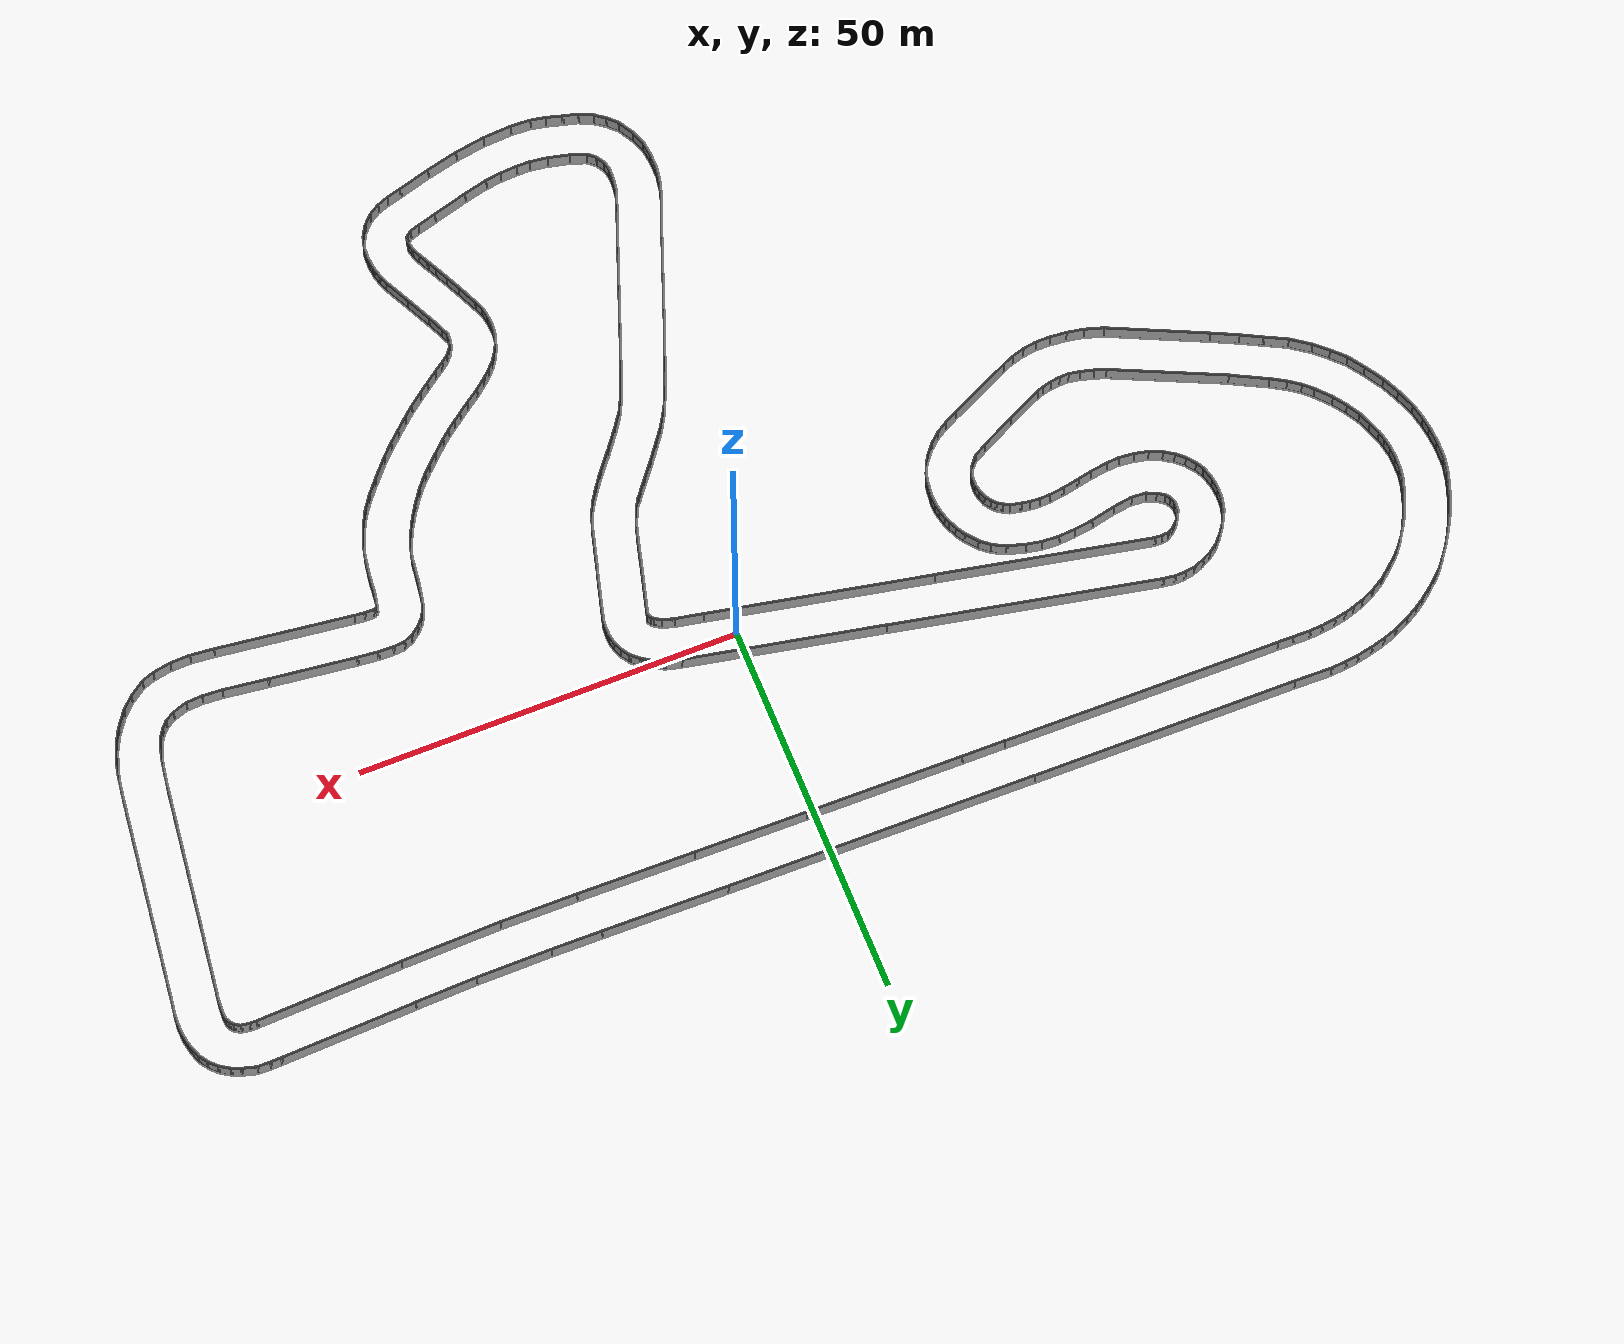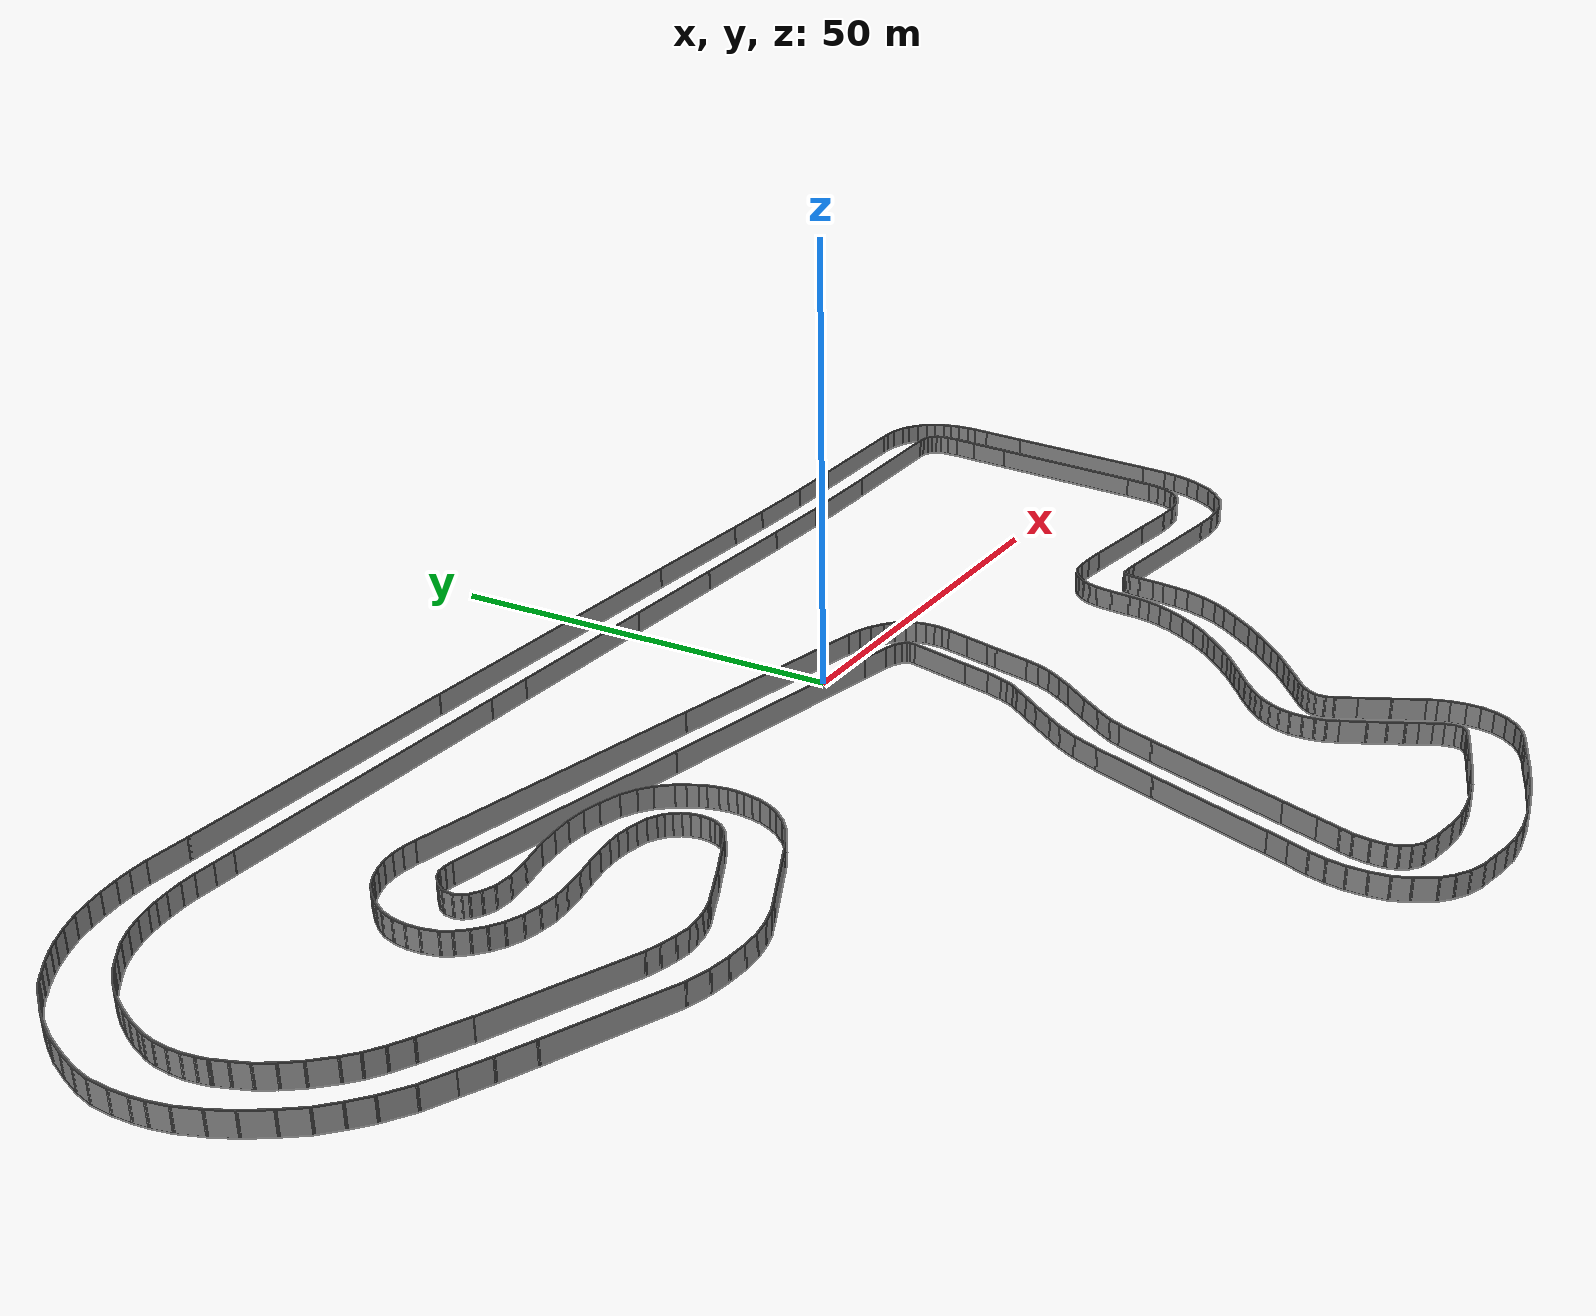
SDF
<?xml version='1.0'?>
<sdf version='1.6'>
  <model name='pista_l'>
    <pose frame=''>-4.26084 -21.2973 0 0 -0 0</pose>
    <link name='Wall_0'>
      <collision name='Wall_0_Collision'>
        <geometry>
          <box>
            <size>34.8647 0.15 2.5</size>
          </box>
        </geometry>
        <pose frame=''>0 0 1.25 0 -0 0</pose>
      </collision>
      <visual name='Wall_0_Visual'>
        <pose frame=''>0 0 1.25 0 -0 0</pose>
        <geometry>
          <box>
            <size>34.8647 0.15 2.5</size>
          </box>
        </geometry>
        <material>
          <script>
            <uri>file://media/materials/scripts/gazebo.material</uri>
            <name>Gazebo/Grey</name>
          </script>
          <ambient>1 1 1 1</ambient>
        </material>
        <meta>
          <layer>0</layer>
        </meta>
      </visual>
      <pose frame=''>-39.9137 53.4663 0 0 0 -0.009195</pose>
    </link>
    <link name='Wall_10'>
      <collision name='Wall_10_Collision'>
        <geometry>
          <box>
            <size>17.7168 0.15 2.5</size>
          </box>
        </geometry>
        <pose frame=''>0 0 1.25 0 -0 0</pose>
      </collision>
      <visual name='Wall_10_Visual'>
        <pose frame=''>0 0 1.25 0 -0 0</pose>
        <geometry>
          <box>
            <size>17.7168 0.15 2.5</size>
          </box>
        </geometry>
        <material>
          <script>
            <uri>file://media/materials/scripts/gazebo.material</uri>
            <name>Gazebo/Grey</name>
          </script>
          <ambient>1 1 1 1</ambient>
        </material>
        <meta>
          <layer>0</layer>
        </meta>
      </visual>
      <pose frame=''>67.591 53.054 0 0 -0 0.034834</pose>
    </link>
    <link name='Wall_100'>
      <collision name='Wall_100_Collision'>
        <geometry>
          <box>
            <size>2.40835 0.15 2.5</size>
          </box>
        </geometry>
        <pose frame=''>0 0 1.25 0 -0 0</pose>
      </collision>
      <visual name='Wall_100_Visual'>
        <pose frame=''>0 0 1.25 0 -0 0</pose>
        <geometry>
          <box>
            <size>2.40835 0.15 2.5</size>
          </box>
        </geometry>
        <material>
          <script>
            <uri>file://media/materials/scripts/gazebo.material</uri>
            <name>Gazebo/Grey</name>
          </script>
          <ambient>1 1 1 1</ambient>
        </material>
        <meta>
          <layer>0</layer>
        </meta>
      </visual>
      <pose frame=''>29.8719 -15.2686 0 0 0 -2.38952</pose>
    </link>
    <link name='Wall_101'>
      <collision name='Wall_101_Collision'>
        <geometry>
          <box>
            <size>1.62145 0.15 2.5</size>
          </box>
        </geometry>
        <pose frame=''>0 0 1.25 0 -0 0</pose>
      </collision>
      <visual name='Wall_101_Visual'>
        <pose frame=''>0 0 1.25 0 -0 0</pose>
        <geometry>
          <box>
            <size>1.62145 0.15 2.5</size>
          </box>
        </geometry>
        <material>
          <script>
            <uri>file://media/materials/scripts/gazebo.material</uri>
            <name>Gazebo/Grey</name>
          </script>
          <ambient>1 1 1 1</ambient>
        </material>
        <meta>
          <layer>0</layer>
        </meta>
      </visual>
      <pose frame=''>28.4887 -16.5188 0 0 0 -2.43297</pose>
    </link>
    <link name='Wall_102'>
      <collision name='Wall_102_Collision'>
        <geometry>
          <box>
            <size>1.49614 0.15 2.5</size>
          </box>
        </geometry>
        <pose frame=''>0 0 1.25 0 -0 0</pose>
      </collision>
      <visual name='Wall_102_Visual'>
        <pose frame=''>0 0 1.25 0 -0 0</pose>
        <geometry>
          <box>
            <size>1.49614 0.15 2.5</size>
          </box>
        </geometry>
        <material>
          <script>
            <uri>file://media/materials/scripts/gazebo.material</uri>
            <name>Gazebo/Grey</name>
          </script>
          <ambient>1 1 1 1</ambient>
        </material>
        <meta>
          <layer>0</layer>
        </meta>
      </visual>
      <pose frame=''>27.3981 -17.4099 0 0 0 -2.48228</pose>
    </link>
    <link name='Wall_103'>
      <collision name='Wall_103_Collision'>
        <geometry>
          <box>
            <size>1.53857 0.15 2.5</size>
          </box>
        </geometry>
        <pose frame=''>0 0 1.25 0 -0 0</pose>
      </collision>
      <visual name='Wall_103_Visual'>
        <pose frame=''>0 0 1.25 0 -0 0</pose>
        <geometry>
          <box>
            <size>1.53857 0.15 2.5</size>
          </box>
        </geometry>
        <material>
          <script>
            <uri>file://media/materials/scripts/gazebo.material</uri>
            <name>Gazebo/Grey</name>
          </script>
          <ambient>1 1 1 1</ambient>
        </material>
        <meta>
          <layer>0</layer>
        </meta>
      </visual>
      <pose frame=''>26.3075 -18.2345 0 0 0 -2.50575</pose>
    </link>
    <link name='Wall_104'>
      <collision name='Wall_104_Collision'>
        <geometry>
          <box>
            <size>1.80457 0.15 2.5</size>
          </box>
        </geometry>
        <pose frame=''>0 0 1.25 0 -0 0</pose>
      </collision>
      <visual name='Wall_104_Visual'>
        <pose frame=''>0 0 1.25 0 -0 0</pose>
        <geometry>
          <box>
            <size>1.80457 0.15 2.5</size>
          </box>
        </geometry>
        <material>
          <script>
            <uri>file://media/materials/scripts/gazebo.material</uri>
            <name>Gazebo/Grey</name>
          </script>
          <ambient>1 1 1 1</ambient>
        </material>
        <meta>
          <layer>0</layer>
        </meta>
      </visual>
      <pose frame=''>25.0839 -19.1389 0 0 0 -2.50452</pose>
    </link>
    <link name='Wall_105'>
      <collision name='Wall_105_Collision'>
        <geometry>
          <box>
            <size>2.23111 0.15 2.5</size>
          </box>
        </geometry>
        <pose frame=''>0 0 1.25 0 -0 0</pose>
      </collision>
      <visual name='Wall_105_Visual'>
        <pose frame=''>0 0 1.25 0 -0 0</pose>
        <geometry>
          <box>
            <size>2.23111 0.15 2.5</size>
          </box>
        </geometry>
        <material>
          <script>
            <uri>file://media/materials/scripts/gazebo.material</uri>
            <name>Gazebo/Grey</name>
          </script>
          <ambient>1 1 1 1</ambient>
        </material>
        <meta>
          <layer>0</layer>
        </meta>
      </visual>
      <pose frame=''>23.5677 -20.2295 0 0 0 -2.52877</pose>
    </link>
    <link name='Wall_106'>
      <collision name='Wall_106_Collision'>
        <geometry>
          <box>
            <size>1.96545 0.15 2.5</size>
          </box>
        </geometry>
        <pose frame=''>0 0 1.25 0 -0 0</pose>
      </collision>
      <visual name='Wall_106_Visual'>
        <pose frame=''>0 0 1.25 0 -0 0</pose>
        <geometry>
          <box>
            <size>1.96545 0.15 2.5</size>
          </box>
        </geometry>
        <material>
          <script>
            <uri>file://media/materials/scripts/gazebo.material</uri>
            <name>Gazebo/Grey</name>
          </script>
          <ambient>1 1 1 1</ambient>
        </material>
        <meta>
          <layer>0</layer>
        </meta>
      </visual>
      <pose frame=''>22.0116 -21.4 0 0 0 -2.45999</pose>
    </link>
    <link name='Wall_107'>
      <collision name='Wall_107_Collision'>
        <geometry>
          <box>
            <size>1.41148 0.15 2.5</size>
          </box>
        </geometry>
        <pose frame=''>0 0 1.25 0 -0 0</pose>
      </collision>
      <visual name='Wall_107_Visual'>
        <pose frame=''>0 0 1.25 0 -0 0</pose>
        <geometry>
          <box>
            <size>1.41148 0.15 2.5</size>
          </box>
        </geometry>
        <material>
          <script>
            <uri>file://media/materials/scripts/gazebo.material</uri>
            <name>Gazebo/Grey</name>
          </script>
          <ambient>1 1 1 1</ambient>
        </material>
        <meta>
          <layer>0</layer>
        </meta>
      </visual>
      <pose frame=''>20.8412 -22.3975 0 0 0 -2.40094</pose>
    </link>
    <link name='Wall_108'>
      <collision name='Wall_108_Collision'>
        <geometry>
          <box>
            <size>1.46718 0.15 2.5</size>
          </box>
        </geometry>
        <pose frame=''>0 0 1.25 0 -0 0</pose>
      </collision>
      <visual name='Wall_108_Visual'>
        <pose frame=''>0 0 1.25 0 -0 0</pose>
        <geometry>
          <box>
            <size>1.46718 0.15 2.5</size>
          </box>
        </geometry>
        <material>
          <script>
            <uri>file://media/materials/scripts/gazebo.material</uri>
            <name>Gazebo/Grey</name>
          </script>
          <ambient>1 1 1 1</ambient>
        </material>
        <meta>
          <layer>0</layer>
        </meta>
      </visual>
      <pose frame=''>19.9235 -23.3019 0 0 0 -2.32763</pose>
    </link>
    <link name='Wall_109'>
      <collision name='Wall_109_Collision'>
        <geometry>
          <box>
            <size>1.51493 0.15 2.5</size>
          </box>
        </geometry>
        <pose frame=''>0 0 1.25 0 -0 0</pose>
      </collision>
      <visual name='Wall_109_Visual'>
        <pose frame=''>0 0 1.25 0 -0 0</pose>
        <geometry>
          <box>
            <size>1.51493 0.15 2.5</size>
          </box>
        </geometry>
        <material>
          <script>
            <uri>file://media/materials/scripts/gazebo.material</uri>
            <name>Gazebo/Grey</name>
          </script>
          <ambient>1 1 1 1</ambient>
        </material>
        <meta>
          <layer>0</layer>
        </meta>
      </visual>
      <pose frame=''>19.0989 -24.3526 0 0 0 -2.14799</pose>
    </link>
    <link name='Wall_11'>
      <collision name='Wall_11_Collision'>
        <geometry>
          <box>
            <size>1.58641 0.15 2.5</size>
          </box>
        </geometry>
        <pose frame=''>0 0 1.25 0 -0 0</pose>
      </collision>
      <visual name='Wall_11_Visual'>
        <pose frame=''>0 0 1.25 0 -0 0</pose>
        <geometry>
          <box>
            <size>1.58641 0.15 2.5</size>
          </box>
        </geometry>
        <material>
          <script>
            <uri>file://media/materials/scripts/gazebo.material</uri>
            <name>Gazebo/Grey</name>
          </script>
          <ambient>1 1 1 1</ambient>
        </material>
        <meta>
          <layer>0</layer>
        </meta>
      </visual>
      <pose frame=''>77.0873 53.3732 0 0 -0 0.018516</pose>
    </link>
    <link name='Wall_110'>
      <collision name='Wall_110_Collision'>
        <geometry>
          <box>
            <size>1.4943 0.15 2.5</size>
          </box>
        </geometry>
        <pose frame=''>0 0 1.25 0 -0 0</pose>
      </collision>
      <visual name='Wall_110_Visual'>
        <pose frame=''>0 0 1.25 0 -0 0</pose>
        <geometry>
          <box>
            <size>1.4943 0.15 2.5</size>
          </box>
        </geometry>
        <material>
          <script>
            <uri>file://media/materials/scripts/gazebo.material</uri>
            <name>Gazebo/Grey</name>
          </script>
          <ambient>1 1 1 1</ambient>
        </material>
        <meta>
          <layer>0</layer>
        </meta>
      </visual>
      <pose frame=''>18.4205 -25.523 0 0 0 -2.04329</pose>
    </link>
    <link name='Wall_111'>
      <collision name='Wall_111_Collision'>
        <geometry>
          <box>
            <size>1.48001 0.15 2.5</size>
          </box>
        </geometry>
        <pose frame=''>0 0 1.25 0 -0 0</pose>
      </collision>
      <visual name='Wall_111_Visual'>
        <pose frame=''>0 0 1.25 0 -0 0</pose>
        <geometry>
          <box>
            <size>1.48001 0.15 2.5</size>
          </box>
        </geometry>
        <material>
          <script>
            <uri>file://media/materials/scripts/gazebo.material</uri>
            <name>Gazebo/Grey</name>
          </script>
          <ambient>1 1 1 1</ambient>
        </material>
        <meta>
          <layer>0</layer>
        </meta>
      </visual>
      <pose frame=''>17.9284 -26.7599 0 0 0 -1.85459</pose>
    </link>
    <link name='Wall_112'>
      <collision name='Wall_112_Collision'>
        <geometry>
          <box>
            <size>1.5373 0.15 2.5</size>
          </box>
        </geometry>
        <pose frame=''>0 0 1.25 0 -0 0</pose>
      </collision>
      <visual name='Wall_112_Visual'>
        <pose frame=''>0 0 1.25 0 -0 0</pose>
        <geometry>
          <box>
            <size>1.5373 0.15 2.5</size>
          </box>
        </geometry>
        <material>
          <script>
            <uri>file://media/materials/scripts/gazebo.material</uri>
            <name>Gazebo/Grey</name>
          </script>
          <ambient>1 1 1 1</ambient>
        </material>
        <meta>
          <layer>0</layer>
        </meta>
      </visual>
      <pose frame=''>17.689 -28.0899 0 0 0 -1.64757</pose>
    </link>
    <link name='Wall_113'>
      <collision name='Wall_113_Collision'>
        <geometry>
          <box>
            <size>1.43124 0.15 2.5</size>
          </box>
        </geometry>
        <pose frame=''>0 0 1.25 0 -0 0</pose>
      </collision>
      <visual name='Wall_113_Visual'>
        <pose frame=''>0 0 1.25 0 -0 0</pose>
        <geometry>
          <box>
            <size>1.43124 0.15 2.5</size>
          </box>
        </geometry>
        <material>
          <script>
            <uri>file://media/materials/scripts/gazebo.material</uri>
            <name>Gazebo/Grey</name>
          </script>
          <ambient>1 1 1 1</ambient>
        </material>
        <meta>
          <layer>0</layer>
        </meta>
      </visual>
      <pose frame=''>17.689 -29.4199 0 0 0 -1.48765</pose>
    </link>
    <link name='Wall_114'>
      <collision name='Wall_114_Collision'>
        <geometry>
          <box>
            <size>1.31344 0.15 2.5</size>
          </box>
        </geometry>
        <pose frame=''>0 0 1.25 0 -0 0</pose>
      </collision>
      <visual name='Wall_114_Visual'>
        <pose frame=''>0 0 1.25 0 -0 0</pose>
        <geometry>
          <box>
            <size>1.31344 0.15 2.5</size>
          </box>
        </geometry>
        <material>
          <script>
            <uri>file://media/materials/scripts/gazebo.material</uri>
            <name>Gazebo/Grey</name>
          </script>
          <ambient>1 1 1 1</ambient>
        </material>
        <meta>
          <layer>0</layer>
        </meta>
      </visual>
      <pose frame=''>17.8486 -30.6302 0 0 0 -1.38685</pose>
    </link>
    <link name='Wall_115'>
      <collision name='Wall_115_Collision'>
        <geometry>
          <box>
            <size>1.41456 0.15 2.5</size>
          </box>
        </geometry>
        <pose frame=''>0 0 1.25 0 -0 0</pose>
      </collision>
      <visual name='Wall_115_Visual'>
        <pose frame=''>0 0 1.25 0 -0 0</pose>
        <geometry>
          <box>
            <size>1.41456 0.15 2.5</size>
          </box>
        </geometry>
        <material>
          <script>
            <uri>file://media/materials/scripts/gazebo.material</uri>
            <name>Gazebo/Grey</name>
          </script>
          <ambient>1 1 1 1</ambient>
        </material>
        <meta>
          <layer>0</layer>
        </meta>
      </visual>
      <pose frame=''>18.1944 -31.7873 0 0 0 -1.18248</pose>
    </link>
    <link name='Wall_117'>
      <collision name='Wall_117_Collision'>
        <geometry>
          <box>
            <size>2.62611 0.15 2.5</size>
          </box>
        </geometry>
        <pose frame=''>0 0 1.25 0 -0 0</pose>
      </collision>
      <visual name='Wall_117_Visual'>
        <pose frame=''>0 0 1.25 0 -0 0</pose>
        <geometry>
          <box>
            <size>2.62611 0.15 2.5</size>
          </box>
        </geometry>
        <material>
          <script>
            <uri>file://media/materials/scripts/gazebo.material</uri>
            <name>Gazebo/Grey</name>
          </script>
          <ambient>1 1 1 1</ambient>
        </material>
        <meta>
          <layer>0</layer>
        </meta>
      </visual>
      <pose frame=''>39.6475 -13.114 0 0 0 -2.25728</pose>
    </link>
    <link name='Wall_118'>
      <collision name='Wall_118_Collision'>
        <geometry>
          <box>
            <size>3.37302 0.15 2.5</size>
          </box>
        </geometry>
        <pose frame=''>0 0 1.25 0 -0 0</pose>
      </collision>
      <visual name='Wall_118_Visual'>
        <pose frame=''>0 0 1.25 0 -0 0</pose>
        <geometry>
          <box>
            <size>3.37302 0.15 2.5</size>
          </box>
        </geometry>
        <material>
          <script>
            <uri>file://media/materials/scripts/gazebo.material</uri>
            <name>Gazebo/Grey</name>
          </script>
          <ambient>1 1 1 1</ambient>
        </material>
        <meta>
          <layer>0</layer>
        </meta>
      </visual>
      <pose frame=''>37.7988 -15.2819 0 0 0 -2.29196</pose>
    </link>
    <link name='Wall_119'>
      <collision name='Wall_119_Collision'>
        <geometry>
          <box>
            <size>2.20029 0.15 2.5</size>
          </box>
        </geometry>
        <pose frame=''>0 0 1.25 0 -0 0</pose>
      </collision>
      <visual name='Wall_119_Visual'>
        <pose frame=''>0 0 1.25 0 -0 0</pose>
        <geometry>
          <box>
            <size>2.20029 0.15 2.5</size>
          </box>
        </geometry>
        <material>
          <script>
            <uri>file://media/materials/scripts/gazebo.material</uri>
            <name>Gazebo/Grey</name>
          </script>
          <ambient>1 1 1 1</ambient>
        </material>
        <meta>
          <layer>0</layer>
        </meta>
      </visual>
      <pose frame=''>36.0166 -17.2237 0 0 0 -2.34702</pose>
    </link>
    <link name='Wall_12'>
      <collision name='Wall_12_Collision'>
        <geometry>
          <box>
            <size>1.77283 0.15 2.5</size>
          </box>
        </geometry>
        <pose frame=''>0 0 1.25 0 -0 0</pose>
      </collision>
      <visual name='Wall_12_Visual'>
        <pose frame=''>0 0 1.25 0 -0 0</pose>
        <geometry>
          <box>
            <size>1.77283 0.15 2.5</size>
          </box>
        </geometry>
        <material>
          <script>
            <uri>file://media/materials/scripts/gazebo.material</uri>
            <name>Gazebo/Grey</name>
          </script>
          <ambient>1 1 1 1</ambient>
        </material>
        <meta>
          <layer>0</layer>
        </meta>
      </visual>
      <pose frame=''>78.6168 53.3732 0 0 0 -0.016392</pose>
    </link>
    <link name='Wall_120'>
      <collision name='Wall_120_Collision'>
        <geometry>
          <box>
            <size>2.1076 0.15 2.5</size>
          </box>
        </geometry>
        <pose frame=''>0 0 1.25 0 -0 0</pose>
      </collision>
      <visual name='Wall_120_Visual'>
        <pose frame=''>0 0 1.25 0 -0 0</pose>
        <geometry>
          <box>
            <size>2.1076 0.15 2.5</size>
          </box>
        </geometry>
        <material>
          <script>
            <uri>file://media/materials/scripts/gazebo.material</uri>
            <name>Gazebo/Grey</name>
          </script>
          <ambient>1 1 1 1</ambient>
        </material>
        <meta>
          <layer>0</layer>
        </meta>
      </visual>
      <pose frame=''>34.5802 -18.6202 0 0 0 -2.39464</pose>
    </link>
    <link name='Wall_121'>
      <collision name='Wall_121_Collision'>
        <geometry>
          <box>
            <size>2.1272 0.15 2.5</size>
          </box>
        </geometry>
        <pose frame=''>0 0 1.25 0 -0 0</pose>
      </collision>
      <visual name='Wall_121_Visual'>
        <pose frame=''>0 0 1.25 0 -0 0</pose>
        <geometry>
          <box>
            <size>2.1272 0.15 2.5</size>
          </box>
        </geometry>
        <material>
          <script>
            <uri>file://media/materials/scripts/gazebo.material</uri>
            <name>Gazebo/Grey</name>
          </script>
          <ambient>1 1 1 1</ambient>
        </material>
        <meta>
          <layer>0</layer>
        </meta>
      </visual>
      <pose frame=''>33.1305 -19.9502 0 0 0 -2.40378</pose>
    </link>
    <link name='Wall_122'>
      <collision name='Wall_122_Collision'>
        <geometry>
          <box>
            <size>1.92166 0.15 2.5</size>
          </box>
        </geometry>
        <pose frame=''>0 0 1.25 0 -0 0</pose>
      </collision>
      <visual name='Wall_122_Visual'>
        <pose frame=''>0 0 1.25 0 -0 0</pose>
        <geometry>
          <box>
            <size>1.92166 0.15 2.5</size>
          </box>
        </geometry>
        <material>
          <script>
            <uri>file://media/materials/scripts/gazebo.material</uri>
            <name>Gazebo/Grey</name>
          </script>
          <ambient>1 1 1 1</ambient>
        </material>
        <meta>
          <layer>0</layer>
        </meta>
      </visual>
      <pose frame=''>31.7339 -21.2005 0 0 0 -2.41994</pose>
    </link>
    <link name='Wall_123'>
      <collision name='Wall_123_Collision'>
        <geometry>
          <box>
            <size>2.2357 0.15 2.5</size>
          </box>
        </geometry>
        <pose frame=''>0 0 1.25 0 -0 0</pose>
      </collision>
      <visual name='Wall_123_Visual'>
        <pose frame=''>0 0 1.25 0 -0 0</pose>
        <geometry>
          <box>
            <size>2.2357 0.15 2.5</size>
          </box>
        </geometry>
        <material>
          <script>
            <uri>file://media/materials/scripts/gazebo.material</uri>
            <name>Gazebo/Grey</name>
          </script>
          <ambient>1 1 1 1</ambient>
        </material>
        <meta>
          <layer>0</layer>
        </meta>
      </visual>
      <pose frame=''>30.2443 -22.4241 0 0 0 -2.48279</pose>
    </link>
    <link name='Wall_124'>
      <collision name='Wall_124_Collision'>
        <geometry>
          <box>
            <size>1.76737 0.15 2.5</size>
          </box>
        </geometry>
        <pose frame=''>0 0 1.25 0 -0 0</pose>
      </collision>
      <visual name='Wall_124_Visual'>
        <pose frame=''>0 0 1.25 0 -0 0</pose>
        <geometry>
          <box>
            <size>1.76737 0.15 2.5</size>
          </box>
        </geometry>
        <material>
          <script>
            <uri>file://media/materials/scripts/gazebo.material</uri>
            <name>Gazebo/Grey</name>
          </script>
          <ambient>1 1 1 1</ambient>
        </material>
        <meta>
          <layer>0</layer>
        </meta>
      </visual>
      <pose frame=''>28.768 -23.5413 0 0 0 -2.50796</pose>
    </link>
    <link name='Wall_125'>
      <collision name='Wall_125_Collision'>
        <geometry>
          <box>
            <size>1.97478 0.15 2.5</size>
          </box>
        </geometry>
        <pose frame=''>0 0 1.25 0 -0 0</pose>
      </collision>
      <visual name='Wall_125_Visual'>
        <pose frame=''>0 0 1.25 0 -0 0</pose>
        <geometry>
          <box>
            <size>1.97478 0.15 2.5</size>
          </box>
        </geometry>
        <material>
          <script>
            <uri>file://media/materials/scripts/gazebo.material</uri>
            <name>Gazebo/Grey</name>
          </script>
          <ambient>1 1 1 1</ambient>
        </material>
        <meta>
          <layer>0</layer>
        </meta>
      </visual>
      <pose frame=''>27.3848 -24.5654 0 0 0 -2.50101</pose>
    </link>
    <link name='Wall_126'>
      <collision name='Wall_126_Collision'>
        <geometry>
          <box>
            <size>1.60355 0.15 2.5</size>
          </box>
        </geometry>
        <pose frame=''>0 0 1.25 0 -0 0</pose>
      </collision>
      <visual name='Wall_126_Visual'>
        <pose frame=''>0 0 1.25 0 -0 0</pose>
        <geometry>
          <box>
            <size>1.60355 0.15 2.5</size>
          </box>
        </geometry>
        <material>
          <script>
            <uri>file://media/materials/scripts/gazebo.material</uri>
            <name>Gazebo/Grey</name>
          </script>
          <ambient>1 1 1 1</ambient>
        </material>
        <meta>
          <layer>0</layer>
        </meta>
      </visual>
      <pose frame=''>26.0548 -25.523 0 0 0 -2.53836</pose>
    </link>
    <link name='Wall_127'>
      <collision name='Wall_127_Collision'>
        <geometry>
          <box>
            <size>1.43785 0.15 2.5</size>
          </box>
        </geometry>
        <pose frame=''>0 0 1.25 0 -0 0</pose>
      </collision>
      <visual name='Wall_127_Visual'>
        <pose frame=''>0 0 1.25 0 -0 0</pose>
        <geometry>
          <box>
            <size>1.43785 0.15 2.5</size>
          </box>
        </geometry>
        <material>
          <script>
            <uri>file://media/materials/scripts/gazebo.material</uri>
            <name>Gazebo/Grey</name>
          </script>
          <ambient>1 1 1 1</ambient>
        </material>
        <meta>
          <layer>0</layer>
        </meta>
      </visual>
      <pose frame=''>24.9509 -26.3343 0 0 0 -2.4733</pose>
    </link>
    <link name='Wall_128'>
      <collision name='Wall_128_Collision'>
        <geometry>
          <box>
            <size>1.24675 0.15 2.5</size>
          </box>
        </geometry>
        <pose frame=''>0 0 1.25 0 -0 0</pose>
      </collision>
      <visual name='Wall_128_Visual'>
        <pose frame=''>0 0 1.25 0 -0 0</pose>
        <geometry>
          <box>
            <size>1.24675 0.15 2.5</size>
          </box>
        </geometry>
        <material>
          <script>
            <uri>file://media/materials/scripts/gazebo.material</uri>
            <name>Gazebo/Grey</name>
          </script>
          <ambient>1 1 1 1</ambient>
        </material>
        <meta>
          <layer>0</layer>
        </meta>
      </visual>
      <pose frame=''>24.0997 -27.1589 0 0 0 -2.25311</pose>
    </link>
    <link name='Wall_129'>
      <collision name='Wall_129_Collision'>
        <geometry>
          <box>
            <size>1.10168 0.15 2.5</size>
          </box>
        </geometry>
        <pose frame=''>0 0 1.25 0 -0 0</pose>
      </collision>
      <visual name='Wall_129_Visual'>
        <pose frame=''>0 0 1.25 0 -0 0</pose>
        <geometry>
          <box>
            <size>1.10168 0.15 2.5</size>
          </box>
        </geometry>
        <material>
          <script>
            <uri>file://media/materials/scripts/gazebo.material</uri>
            <name>Gazebo/Grey</name>
          </script>
          <ambient>1 1 1 1</ambient>
        </material>
        <meta>
          <layer>0</layer>
        </meta>
      </visual>
      <pose frame=''>23.5411 -28.0101 0 0 0 -2.03444</pose>
    </link>
    <link name='Wall_13'>
      <collision name='Wall_13_Collision'>
        <geometry>
          <box>
            <size>2.13773 0.15 2.5</size>
          </box>
        </geometry>
        <pose frame=''>0 0 1.25 0 -0 0</pose>
      </collision>
      <visual name='Wall_13_Visual'>
        <pose frame=''>0 0 1.25 0 -0 0</pose>
        <geometry>
          <box>
            <size>2.13773 0.15 2.5</size>
          </box>
        </geometry>
        <material>
          <script>
            <uri>file://media/materials/scripts/gazebo.material</uri>
            <name>Gazebo/Grey</name>
          </script>
          <ambient>1 1 1 1</ambient>
        </material>
        <meta>
          <layer>0</layer>
        </meta>
      </visual>
      <pose frame=''>80.3857 53.0939 0 0 0 -0.270947</pose>
    </link>
    <link name='Wall_130'>
      <collision name='Wall_130_Collision'>
        <geometry>
          <box>
            <size>1.16116 0.15 2.5</size>
          </box>
        </geometry>
        <pose frame=''>0 0 1.25 0 -0 0</pose>
      </collision>
      <visual name='Wall_130_Visual'>
        <pose frame=''>0 0 1.25 0 -0 0</pose>
        <geometry>
          <box>
            <size>1.16116 0.15 2.5</size>
          </box>
        </geometry>
        <material>
          <script>
            <uri>file://media/materials/scripts/gazebo.material</uri>
            <name>Gazebo/Grey</name>
          </script>
          <ambient>1 1 1 1</ambient>
        </material>
        <meta>
          <layer>0</layer>
        </meta>
      </visual>
      <pose frame=''>23.315 -28.9411 0 0 0 -1.59711</pose>
    </link>
    <link name='Wall_131'>
      <collision name='Wall_131_Collision'>
        <geometry>
          <box>
            <size>1.16291 0.15 2.5</size>
          </box>
        </geometry>
        <pose frame=''>0 0 1.25 0 -0 0</pose>
      </collision>
      <visual name='Wall_131_Visual'>
        <pose frame=''>0 0 1.25 0 -0 0</pose>
        <geometry>
          <box>
            <size>1.16291 0.15 2.5</size>
          </box>
        </geometry>
        <material>
          <script>
            <uri>file://media/materials/scripts/gazebo.material</uri>
            <name>Gazebo/Grey</name>
          </script>
          <ambient>1 1 1 1</ambient>
        </material>
        <meta>
          <layer>0</layer>
        </meta>
      </visual>
      <pose frame=''>23.5012 -29.912 0 0 0 -1.1659</pose>
    </link>
    <link name='Wall_132'>
      <collision name='Wall_132_Collision'>
        <geometry>
          <box>
            <size>2.50783 0.15 2.5</size>
          </box>
        </geometry>
        <pose frame=''>0 0 1.25 0 -0 0</pose>
      </collision>
      <visual name='Wall_132_Visual'>
        <pose frame=''>0 0 1.25 0 -0 0</pose>
        <geometry>
          <box>
            <size>2.50783 0.15 2.5</size>
          </box>
        </geometry>
        <material>
          <script>
            <uri>file://media/materials/scripts/gazebo.material</uri>
            <name>Gazebo/Grey</name>
          </script>
          <ambient>1 1 1 1</ambient>
        </material>
        <meta>
          <layer>0</layer>
        </meta>
      </visual>
      <pose frame=''>24.1795 -31.4548 0 0 0 -1.15257</pose>
    </link>
    <link name='Wall_134'>
      <collision name='Wall_134_Collision'>
        <geometry>
          <box>
            <size>3.0427 0.15 2.5</size>
          </box>
        </geometry>
        <pose frame=''>0 0 1.25 0 -0 0</pose>
      </collision>
      <visual name='Wall_134_Visual'>
        <pose frame=''>0 0 1.25 0 -0 0</pose>
        <geometry>
          <box>
            <size>3.0427 0.15 2.5</size>
          </box>
        </geometry>
        <material>
          <script>
            <uri>file://media/materials/scripts/gazebo.material</uri>
            <name>Gazebo/Grey</name>
          </script>
          <ambient>1 1 1 1</ambient>
        </material>
        <meta>
          <layer>0</layer>
        </meta>
      </visual>
      <pose frame=''>19.059 -33.6893 0 0 0 -1.14417</pose>
    </link>
    <link name='Wall_135'>
      <collision name='Wall_135_Collision'>
        <geometry>
          <box>
            <size>2.22004 0.15 2.5</size>
          </box>
        </geometry>
        <pose frame=''>0 0 1.25 0 -0 0</pose>
      </collision>
      <visual name='Wall_135_Visual'>
        <pose frame=''>0 0 1.25 0 -0 0</pose>
        <geometry>
          <box>
            <size>2.22004 0.15 2.5</size>
          </box>
        </geometry>
        <material>
          <script>
            <uri>file://media/materials/scripts/gazebo.material</uri>
            <name>Gazebo/Grey</name>
          </script>
          <ambient>1 1 1 1</ambient>
        </material>
        <meta>
          <layer>0</layer>
        </meta>
      </visual>
      <pose frame=''>20.1097 -35.937 0 0 0 -1.11864</pose>
    </link>
    <link name='Wall_136'>
      <collision name='Wall_136_Collision'>
        <geometry>
          <box>
            <size>2.0177 0.15 2.5</size>
          </box>
        </geometry>
        <pose frame=''>0 0 1.25 0 -0 0</pose>
      </collision>
      <visual name='Wall_136_Visual'>
        <pose frame=''>0 0 1.25 0 -0 0</pose>
        <geometry>
          <box>
            <size>2.0177 0.15 2.5</size>
          </box>
        </geometry>
        <material>
          <script>
            <uri>file://media/materials/scripts/gazebo.material</uri>
            <name>Gazebo/Grey</name>
          </script>
          <ambient>1 1 1 1</ambient>
        </material>
        <meta>
          <layer>0</layer>
        </meta>
      </visual>
      <pose frame=''>20.9742 -37.7059 0 0 0 -1.11352</pose>
    </link>
    <link name='Wall_137'>
      <collision name='Wall_137_Collision'>
        <geometry>
          <box>
            <size>1.53014 0.15 2.5</size>
          </box>
        </geometry>
        <pose frame=''>0 0 1.25 0 -0 0</pose>
      </collision>
      <visual name='Wall_137_Visual'>
        <pose frame=''>0 0 1.25 0 -0 0</pose>
        <geometry>
          <box>
            <size>1.53014 0.15 2.5</size>
          </box>
        </geometry>
        <material>
          <script>
            <uri>file://media/materials/scripts/gazebo.material</uri>
            <name>Gazebo/Grey</name>
          </script>
          <ambient>1 1 1 1</ambient>
        </material>
        <meta>
          <layer>0</layer>
        </meta>
      </visual>
      <pose frame=''>21.7057 -39.1556 0 0 0 -1.08991</pose>
    </link>
    <link name='Wall_138'>
      <collision name='Wall_138_Collision'>
        <geometry>
          <box>
            <size>1.61325 0.15 2.5</size>
          </box>
        </geometry>
        <pose frame=''>0 0 1.25 0 -0 0</pose>
      </collision>
      <visual name='Wall_138_Visual'>
        <pose frame=''>0 0 1.25 0 -0 0</pose>
        <geometry>
          <box>
            <size>1.61325 0.15 2.5</size>
          </box>
        </geometry>
        <material>
          <script>
            <uri>file://media/materials/scripts/gazebo.material</uri>
            <name>Gazebo/Grey</name>
          </script>
          <ambient>1 1 1 1</ambient>
        </material>
        <meta>
          <layer>0</layer>
        </meta>
      </visual>
      <pose frame=''>22.3574 -40.4191 0 0 0 -1.09902</pose>
    </link>
    <link name='Wall_139'>
      <collision name='Wall_139_Collision'>
        <geometry>
          <box>
            <size>1.31678 0.15 2.5</size>
          </box>
        </geometry>
        <pose frame=''>0 0 1.25 0 -0 0</pose>
      </collision>
      <visual name='Wall_139_Visual'>
        <pose frame=''>0 0 1.25 0 -0 0</pose>
        <geometry>
          <box>
            <size>1.31678 0.15 2.5</size>
          </box>
        </geometry>
        <material>
          <script>
            <uri>file://media/materials/scripts/gazebo.material</uri>
            <name>Gazebo/Grey</name>
          </script>
          <ambient>1 1 1 1</ambient>
        </material>
        <meta>
          <layer>0</layer>
        </meta>
      </visual>
      <pose frame=''>22.9293 -41.6028 0 0 0 -1.14794</pose>
    </link>
    <link name='Wall_14'>
      <collision name='Wall_14_Collision'>
        <geometry>
          <box>
            <size>1.38998 0.15 2.5</size>
          </box>
        </geometry>
        <pose frame=''>0 0 1.25 0 -0 0</pose>
      </collision>
      <visual name='Wall_14_Visual'>
        <pose frame=''>0 0 1.25 0 -0 0</pose>
        <geometry>
          <box>
            <size>1.38998 0.15 2.5</size>
          </box>
        </geometry>
        <material>
          <script>
            <uri>file://media/materials/scripts/gazebo.material</uri>
            <name>Gazebo/Grey</name>
          </script>
          <ambient>1 1 1 1</ambient>
        </material>
        <meta>
          <layer>0</layer>
        </meta>
      </visual>
      <pose frame=''>81.9152 52.5885 0 0 0 -0.396441</pose>
    </link>
    <link name='Wall_140'>
      <collision name='Wall_140_Collision'>
        <geometry>
          <box>
            <size>1.2873 0.15 2.5</size>
          </box>
        </geometry>
        <pose frame=''>0 0 1.25 0 -0 0</pose>
      </collision>
      <visual name='Wall_140_Visual'>
        <pose frame=''>0 0 1.25 0 -0 0</pose>
        <geometry>
          <box>
            <size>1.2873 0.15 2.5</size>
          </box>
        </geometry>
        <material>
          <script>
            <uri>file://media/materials/scripts/gazebo.material</uri>
            <name>Gazebo/Grey</name>
          </script>
          <ambient>1 1 1 1</ambient>
        </material>
        <meta>
          <layer>0</layer>
        </meta>
      </visual>
      <pose frame=''>23.2751 -42.6934 0 0 0 -1.38258</pose>
    </link>
    <link name='Wall_141'>
      <collision name='Wall_141_Collision'>
        <geometry>
          <box>
            <size>0.959013 0.15 2.5</size>
          </box>
        </geometry>
        <pose frame=''>0 0 1.25 0 -0 0</pose>
      </collision>
      <visual name='Wall_141_Visual'>
        <pose frame=''>0 0 1.25 0 -0 0</pose>
        <geometry>
          <box>
            <size>0.959013 0.15 2.5</size>
          </box>
        </geometry>
        <material>
          <script>
            <uri>file://media/materials/scripts/gazebo.material</uri>
            <name>Gazebo/Grey</name>
          </script>
          <ambient>1 1 1 1</ambient>
        </material>
        <meta>
          <layer>0</layer>
        </meta>
      </visual>
      <pose frame=''>23.315 -43.651 0 0 0 -1.73595</pose>
    </link>
    <link name='Wall_142'>
      <collision name='Wall_142_Collision'>
        <geometry>
          <box>
            <size>1.00162 0.15 2.5</size>
          </box>
        </geometry>
        <pose frame=''>0 0 1.25 0 -0 0</pose>
      </collision>
      <visual name='Wall_142_Visual'>
        <pose frame=''>0 0 1.25 0 -0 0</pose>
        <geometry>
          <box>
            <size>1.00162 0.15 2.5</size>
          </box>
        </geometry>
        <material>
          <script>
            <uri>file://media/materials/scripts/gazebo.material</uri>
            <name>Gazebo/Grey</name>
          </script>
          <ambient>1 1 1 1</ambient>
        </material>
        <meta>
          <layer>0</layer>
        </meta>
      </visual>
      <pose frame=''>22.916 -44.316 0 0 0 -2.46685</pose>
    </link>
    <link name='Wall_143'>
      <collision name='Wall_143_Collision'>
        <geometry>
          <box>
            <size>1.41176 0.15 2.5</size>
          </box>
        </geometry>
        <pose frame=''>0 0 1.25 0 -0 0</pose>
      </collision>
      <visual name='Wall_143_Visual'>
        <pose frame=''>0 0 1.25 0 -0 0</pose>
        <geometry>
          <box>
            <size>1.41176 0.15 2.5</size>
          </box>
        </geometry>
        <material>
          <script>
            <uri>file://media/materials/scripts/gazebo.material</uri>
            <name>Gazebo/Grey</name>
          </script>
          <ambient>1 1 1 1</ambient>
        </material>
        <meta>
          <layer>0</layer>
        </meta>
      </visual>
      <pose frame=''>21.985 -44.7815 0 0 0 -2.81984</pose>
    </link>
    <link name='Wall_144'>
      <collision name='Wall_144_Collision'>
        <geometry>
          <box>
            <size>2.82831 0.15 2.5</size>
          </box>
        </geometry>
        <pose frame=''>0 0 1.25 0 -0 0</pose>
      </collision>
      <visual name='Wall_144_Visual'>
        <pose frame=''>0 0 1.25 0 -0 0</pose>
        <geometry>
          <box>
            <size>2.82831 0.15 2.5</size>
          </box>
        </geometry>
        <material>
          <script>
            <uri>file://media/materials/scripts/gazebo.material</uri>
            <name>Gazebo/Grey</name>
          </script>
          <ambient>1 1 1 1</ambient>
        </material>
        <meta>
          <layer>0</layer>
        </meta>
      </visual>
      <pose frame=''>20.0964 -45.3401 0 0 0 -2.87011</pose>
    </link>
    <link name='Wall_145'>
      <collision name='Wall_145_Collision'>
        <geometry>
          <box>
            <size>4.81604 0.15 2.5</size>
          </box>
        </geometry>
        <pose frame=''>0 0 1.25 0 -0 0</pose>
      </collision>
      <visual name='Wall_145_Visual'>
        <pose frame=''>0 0 1.25 0 -0 0</pose>
        <geometry>
          <box>
            <size>4.81604 0.15 2.5</size>
          </box>
        </geometry>
        <material>
          <script>
            <uri>file://media/materials/scripts/gazebo.material</uri>
            <name>Gazebo/Grey</name>
          </script>
          <ambient>1 1 1 1</ambient>
        </material>
        <meta>
          <layer>0</layer>
        </meta>
      </visual>
      <pose frame=''>16.5585 -46.3243 0 0 0 -2.87034</pose>
    </link>
    <link name='Wall_146'>
      <collision name='Wall_146_Collision'>
        <geometry>
          <box>
            <size>3.40806 0.15 2.5</size>
          </box>
        </geometry>
        <pose frame=''>0 0 1.25 0 -0 0</pose>
      </collision>
      <visual name='Wall_146_Visual'>
        <pose frame=''>0 0 1.25 0 -0 0</pose>
        <geometry>
          <box>
            <size>3.40806 0.15 2.5</size>
          </box>
        </geometry>
        <material>
          <script>
            <uri>file://media/materials/scripts/gazebo.material</uri>
            <name>Gazebo/Grey</name>
          </script>
          <ambient>1 1 1 1</ambient>
        </material>
        <meta>
          <layer>0</layer>
        </meta>
      </visual>
      <pose frame=''>12.7281 -47.3352 0 0 0 -2.90255</pose>
    </link>
    <link name='Wall_147'>
      <collision name='Wall_147_Collision'>
        <geometry>
          <box>
            <size>2.27169 0.15 2.5</size>
          </box>
        </geometry>
        <pose frame=''>0 0 1.25 0 -0 0</pose>
      </collision>
      <visual name='Wall_147_Visual'>
        <pose frame=''>0 0 1.25 0 -0 0</pose>
        <geometry>
          <box>
            <size>2.27169 0.15 2.5</size>
          </box>
        </geometry>
        <material>
          <script>
            <uri>file://media/materials/scripts/gazebo.material</uri>
            <name>Gazebo/Grey</name>
          </script>
          <ambient>1 1 1 1</ambient>
        </material>
        <meta>
          <layer>0</layer>
        </meta>
      </visual>
      <pose frame=''>10.0947 -47.8672 0 0 0 -3.00324</pose>
    </link>
    <link name='Wall_148'>
      <collision name='Wall_148_Collision'>
        <geometry>
          <box>
            <size>2.41493 0.15 2.5</size>
          </box>
        </geometry>
        <pose frame=''>0 0 1.25 0 -0 0</pose>
      </collision>
      <visual name='Wall_148_Visual'>
        <pose frame=''>0 0 1.25 0 -0 0</pose>
        <geometry>
          <box>
            <size>2.41493 0.15 2.5</size>
          </box>
        </geometry>
        <material>
          <script>
            <uri>file://media/materials/scripts/gazebo.material</uri>
            <name>Gazebo/Grey</name>
          </script>
          <ambient>1 1 1 1</ambient>
        </material>
        <meta>
          <layer>0</layer>
        </meta>
      </visual>
      <pose frame=''>7.91347 -48.08 0 0 0 -3.08284</pose>
    </link>
    <link name='Wall_149'>
      <collision name='Wall_149_Collision'>
        <geometry>
          <box>
            <size>1.90561 0.15 2.5</size>
          </box>
        </geometry>
        <pose frame=''>0 0 1.25 0 -0 0</pose>
      </collision>
      <visual name='Wall_149_Visual'>
        <pose frame=''>0 0 1.25 0 -0 0</pose>
        <geometry>
          <box>
            <size>1.90561 0.15 2.5</size>
          </box>
        </geometry>
        <material>
          <script>
            <uri>file://media/materials/scripts/gazebo.material</uri>
            <name>Gazebo/Grey</name>
          </script>
          <ambient>1 1 1 1</ambient>
        </material>
        <meta>
          <layer>0</layer>
        </meta>
      </visual>
      <pose frame=''>5.90515 -48.1465 0 0 -0 3.14159</pose>
    </link>
    <link name='Wall_15'>
      <collision name='Wall_15_Collision'>
        <geometry>
          <box>
            <size>1.72907 0.15 2.5</size>
          </box>
        </geometry>
        <pose frame=''>0 0 1.25 0 -0 0</pose>
      </collision>
      <visual name='Wall_15_Visual'>
        <pose frame=''>0 0 1.25 0 -0 0</pose>
        <geometry>
          <box>
            <size>1.72907 0.15 2.5</size>
          </box>
        </geometry>
        <material>
          <script>
            <uri>file://media/materials/scripts/gazebo.material</uri>
            <name>Gazebo/Grey</name>
          </script>
          <ambient>1 1 1 1</ambient>
        </material>
        <meta>
          <layer>0</layer>
        </meta>
      </visual>
      <pose frame=''>83.1521 51.9235 0 0 0 -0.569313</pose>
    </link>
    <link name='Wall_150'>
      <collision name='Wall_150_Collision'>
        <geometry>
          <box>
            <size>2.48613 0.15 2.5</size>
          </box>
        </geometry>
        <pose frame=''>0 0 1.25 0 -0 0</pose>
      </collision>
      <visual name='Wall_150_Visual'>
        <pose frame=''>0 0 1.25 0 -0 0</pose>
        <geometry>
          <box>
            <size>2.48613 0.15 2.5</size>
          </box>
        </geometry>
        <material>
          <script>
            <uri>file://media/materials/scripts/gazebo.material</uri>
            <name>Gazebo/Grey</name>
          </script>
          <ambient>1 1 1 1</ambient>
        </material>
        <meta>
          <layer>0</layer>
        </meta>
      </visual>
      <pose frame=''>3.87024 -47.9869 0 0 -0 3.00453</pose>
    </link>
    <link name='Wall_151'>
      <collision name='Wall_151_Collision'>
        <geometry>
          <box>
            <size>2.96321 0.15 2.5</size>
          </box>
        </geometry>
        <pose frame=''>0 0 1.25 0 -0 0</pose>
      </collision>
      <visual name='Wall_151_Visual'>
        <pose frame=''>0 0 1.25 0 -0 0</pose>
        <geometry>
          <box>
            <size>2.96321 0.15 2.5</size>
          </box>
        </geometry>
        <material>
          <script>
            <uri>file://media/materials/scripts/gazebo.material</uri>
            <name>Gazebo/Grey</name>
          </script>
          <ambient>1 1 1 1</ambient>
        </material>
        <meta>
          <layer>0</layer>
        </meta>
      </visual>
      <pose frame=''>1.34322 -47.5081 0 0 -0 2.91267</pose>
    </link>
    <link name='Wall_152'>
      <collision name='Wall_152_Collision'>
        <geometry>
          <box>
            <size>2.3456 0.15 2.5</size>
          </box>
        </geometry>
        <pose frame=''>0 0 1.25 0 -0 0</pose>
      </collision>
      <visual name='Wall_152_Visual'>
        <pose frame=''>0 0 1.25 0 -0 0</pose>
        <geometry>
          <box>
            <size>2.3456 0.15 2.5</size>
          </box>
        </geometry>
        <material>
          <script>
            <uri>file://media/materials/scripts/gazebo.material</uri>
            <name>Gazebo/Grey</name>
          </script>
          <ambient>1 1 1 1</ambient>
        </material>
        <meta>
          <layer>0</layer>
        </meta>
      </visual>
      <pose frame=''>-1.0641 -46.8297 0 0 -0 2.80835</pose>
    </link>
    <link name='Wall_153'>
      <collision name='Wall_153_Collision'>
        <geometry>
          <box>
            <size>1.48876 0.15 2.5</size>
          </box>
        </geometry>
        <pose frame=''>0 0 1.25 0 -0 0</pose>
      </collision>
      <visual name='Wall_153_Visual'>
        <pose frame=''>0 0 1.25 0 -0 0</pose>
        <geometry>
          <box>
            <size>1.48876 0.15 2.5</size>
          </box>
        </geometry>
        <material>
          <script>
            <uri>file://media/materials/scripts/gazebo.material</uri>
            <name>Gazebo/Grey</name>
          </script>
          <ambient>1 1 1 1</ambient>
        </material>
        <meta>
          <layer>0</layer>
        </meta>
      </visual>
      <pose frame=''>-2.60691 -46.0317 0 0 -0 2.4265</pose>
    </link>
    <link name='Wall_154'>
      <collision name='Wall_154_Collision'>
        <geometry>
          <box>
            <size>1.30886 0.15 2.5</size>
          </box>
        </geometry>
        <pose frame=''>0 0 1.25 0 -0 0</pose>
      </collision>
      <visual name='Wall_154_Visual'>
        <pose frame=''>0 0 1.25 0 -0 0</pose>
        <geometry>
          <box>
            <size>1.30886 0.15 2.5</size>
          </box>
        </geometry>
        <material>
          <script>
            <uri>file://media/materials/scripts/gazebo.material</uri>
            <name>Gazebo/Grey</name>
          </script>
          <ambient>1 1 1 1</ambient>
        </material>
        <meta>
          <layer>0</layer>
        </meta>
      </visual>
      <pose frame=''>-3.41822 -45.1007 0 0 -0 2.12696</pose>
    </link>
    <link name='Wall_155'>
      <collision name='Wall_155_Collision'>
        <geometry>
          <box>
            <size>1.27918 0.15 2.5</size>
          </box>
        </geometry>
        <pose frame=''>0 0 1.25 0 -0 0</pose>
      </collision>
      <visual name='Wall_155_Visual'>
        <pose frame=''>0 0 1.25 0 -0 0</pose>
        <geometry>
          <box>
            <size>1.27918 0.15 2.5</size>
          </box>
        </geometry>
        <material>
          <script>
            <uri>file://media/materials/scripts/gazebo.material</uri>
            <name>Gazebo/Grey</name>
          </script>
          <ambient>1 1 1 1</ambient>
        </material>
        <meta>
          <layer>0</layer>
        </meta>
      </visual>
      <pose frame=''>-3.87042 -44.0633 0 0 -0 1.83292</pose>
    </link>
    <link name='Wall_156'>
      <collision name='Wall_156_Collision'>
        <geometry>
          <box>
            <size>1.69304 0.15 2.5</size>
          </box>
        </geometry>
        <pose frame=''>0 0 1.25 0 -0 0</pose>
      </collision>
      <visual name='Wall_156_Visual'>
        <pose frame=''>0 0 1.25 0 -0 0</pose>
        <geometry>
          <box>
            <size>1.69304 0.15 2.5</size>
          </box>
        </geometry>
        <material>
          <script>
            <uri>file://media/materials/scripts/gazebo.material</uri>
            <name>Gazebo/Grey</name>
          </script>
          <ambient>1 1 1 1</ambient>
        </material>
        <meta>
          <layer>0</layer>
        </meta>
      </visual>
      <pose frame=''>-4.00342 -42.7466 0 0 -0 1.55356</pose>
    </link>
    <link name='Wall_157'>
      <collision name='Wall_157_Collision'>
        <geometry>
          <box>
            <size>1.87307 0.15 2.5</size>
          </box>
        </geometry>
        <pose frame=''>0 0 1.25 0 -0 0</pose>
      </collision>
      <visual name='Wall_157_Visual'>
        <pose frame=''>0 0 1.25 0 -0 0</pose>
        <geometry>
          <box>
            <size>1.87307 0.15 2.5</size>
          </box>
        </geometry>
        <material>
          <script>
            <uri>file://media/materials/scripts/gazebo.material</uri>
            <name>Gazebo/Grey</name>
          </script>
          <ambient>1 1 1 1</ambient>
        </material>
        <meta>
          <layer>0</layer>
        </meta>
      </visual>
      <pose frame=''>-3.85712 -41.124 0 0 -0 1.4158</pose>
    </link>
    <link name='Wall_158'>
      <collision name='Wall_158_Collision'>
        <geometry>
          <box>
            <size>1.58863 0.15 2.5</size>
          </box>
        </geometry>
        <pose frame=''>0 0 1.25 0 -0 0</pose>
      </collision>
      <visual name='Wall_158_Visual'>
        <pose frame=''>0 0 1.25 0 -0 0</pose>
        <geometry>
          <box>
            <size>1.58863 0.15 2.5</size>
          </box>
        </geometry>
        <material>
          <script>
            <uri>file://media/materials/scripts/gazebo.material</uri>
            <name>Gazebo/Grey</name>
          </script>
          <ambient>1 1 1 1</ambient>
        </material>
        <meta>
          <layer>0</layer>
        </meta>
      </visual>
      <pose frame=''>-3.48472 -39.5945 0 0 -0 1.2315</pose>
    </link>
    <link name='Wall_159'>
      <collision name='Wall_159_Collision'>
        <geometry>
          <box>
            <size>2.75899 0.15 2.5</size>
          </box>
        </geometry>
        <pose frame=''>0 0 1.25 0 -0 0</pose>
      </collision>
      <visual name='Wall_159_Visual'>
        <pose frame=''>0 0 1.25 0 -0 0</pose>
        <geometry>
          <box>
            <size>2.75899 0.15 2.5</size>
          </box>
        </geometry>
        <material>
          <script>
            <uri>file://media/materials/scripts/gazebo.material</uri>
            <name>Gazebo/Grey</name>
          </script>
          <ambient>1 1 1 1</ambient>
        </material>
        <meta>
          <layer>0</layer>
        </meta>
      </visual>
      <pose frame=''>-2.79311 -37.6926 0 0 -0 1.2168</pose>
    </link>
    <link name='Wall_16'>
      <collision name='Wall_16_Collision'>
        <geometry>
          <box>
            <size>1.54188 0.15 2.5</size>
          </box>
        </geometry>
        <pose frame=''>0 0 1.25 0 -0 0</pose>
      </collision>
      <visual name='Wall_16_Visual'>
        <pose frame=''>0 0 1.25 0 -0 0</pose>
        <geometry>
          <box>
            <size>1.54188 0.15 2.5</size>
          </box>
        </geometry>
        <material>
          <script>
            <uri>file://media/materials/scripts/gazebo.material</uri>
            <name>Gazebo/Grey</name>
          </script>
          <ambient>1 1 1 1</ambient>
        </material>
        <meta>
          <layer>0</layer>
        </meta>
      </visual>
      <pose frame=''>84.3092 51.0058 0 0 0 -0.785398</pose>
    </link>
    <link name='Wall_160'>
      <collision name='Wall_160_Collision'>
        <geometry>
          <box>
            <size>4.25661 0.15 2.5</size>
          </box>
        </geometry>
        <pose frame=''>0 0 1.25 0 -0 0</pose>
      </collision>
      <visual name='Wall_160_Visual'>
        <pose frame=''>0 0 1.25 0 -0 0</pose>
        <geometry>
          <box>
            <size>4.25661 0.15 2.5</size>
          </box>
        </geometry>
        <material>
          <script>
            <uri>file://media/materials/scripts/gazebo.material</uri>
            <name>Gazebo/Grey</name>
          </script>
          <ambient>1 1 1 1</ambient>
        </material>
        <meta>
          <layer>0</layer>
        </meta>
      </visual>
      <pose frame=''>-1.636 -34.5405 0 0 -0 1.22036</pose>
    </link>
    <link name='Wall_162'>
      <collision name='Wall_162_Collision'>
        <geometry>
          <box>
            <size>3.76645 0.15 2.5</size>
          </box>
        </geometry>
        <pose frame=''>0 0 1.25 0 -0 0</pose>
      </collision>
      <visual name='Wall_162_Visual'>
        <pose frame=''>0 0 1.25 0 -0 0</pose>
        <geometry>
          <box>
            <size>3.76645 0.15 2.5</size>
          </box>
        </geometry>
        <material>
          <script>
            <uri>file://media/materials/scripts/gazebo.material</uri>
            <name>Gazebo/Grey</name>
          </script>
          <ambient>1 1 1 1</ambient>
        </material>
        <meta>
          <layer>0</layer>
        </meta>
      </visual>
      <pose frame=''>25.4829 -34.1548 0 0 0 -1.11373</pose>
    </link>
    <link name='Wall_163'>
      <collision name='Wall_163_Collision'>
        <geometry>
          <box>
            <size>3.81398 0.15 2.5</size>
          </box>
        </geometry>
        <pose frame=''>0 0 1.25 0 -0 0</pose>
      </collision>
      <visual name='Wall_163_Visual'>
        <pose frame=''>0 0 1.25 0 -0 0</pose>
        <geometry>
          <box>
            <size>3.81398 0.15 2.5</size>
          </box>
        </geometry>
        <material>
          <script>
            <uri>file://media/materials/scripts/gazebo.material</uri>
            <name>Gazebo/Grey</name>
          </script>
          <ambient>1 1 1 1</ambient>
        </material>
        <meta>
          <layer>0</layer>
        </meta>
      </visual>
      <pose frame=''>27.1055 -37.4133 0 0 0 -1.1039</pose>
    </link>
    <link name='Wall_164'>
      <collision name='Wall_164_Collision'>
        <geometry>
          <box>
            <size>1.32071 0.15 2.5</size>
          </box>
        </geometry>
        <pose frame=''>0 0 1.25 0 -0 0</pose>
      </collision>
      <visual name='Wall_164_Visual'>
        <pose frame=''>0 0 1.25 0 -0 0</pose>
        <geometry>
          <box>
            <size>1.32071 0.15 2.5</size>
          </box>
        </geometry>
        <material>
          <script>
            <uri>file://media/materials/scripts/gazebo.material</uri>
            <name>Gazebo/Grey</name>
          </script>
          <ambient>1 1 1 1</ambient>
        </material>
        <meta>
          <layer>0</layer>
        </meta>
      </visual>
      <pose frame=''>28.1429 -39.5945 0 0 0 -1.19873</pose>
    </link>
    <link name='Wall_165'>
      <collision name='Wall_165_Collision'>
        <geometry>
          <box>
            <size>1.47281 0.15 2.5</size>
          </box>
        </geometry>
        <pose frame=''>0 0 1.25 0 -0 0</pose>
      </collision>
      <visual name='Wall_165_Visual'>
        <pose frame=''>0 0 1.25 0 -0 0</pose>
        <geometry>
          <box>
            <size>1.47281 0.15 2.5</size>
          </box>
        </geometry>
        <material>
          <script>
            <uri>file://media/materials/scripts/gazebo.material</uri>
            <name>Gazebo/Grey</name>
          </script>
          <ambient>1 1 1 1</ambient>
        </material>
        <meta>
          <layer>0</layer>
        </meta>
      </visual>
      <pose frame=''>28.5286 -40.7782 0 0 0 -1.30631</pose>
    </link>
    <link name='Wall_166'>
      <collision name='Wall_166_Collision'>
        <geometry>
          <box>
            <size>1.80969 0.15 2.5</size>
          </box>
        </geometry>
        <pose frame=''>0 0 1.25 0 -0 0</pose>
      </collision>
      <visual name='Wall_166_Visual'>
        <pose frame=''>0 0 1.25 0 -0 0</pose>
        <geometry>
          <box>
            <size>1.80969 0.15 2.5</size>
          </box>
        </geometry>
        <material>
          <script>
            <uri>file://media/materials/scripts/gazebo.material</uri>
            <name>Gazebo/Grey</name>
          </script>
          <ambient>1 1 1 1</ambient>
        </material>
        <meta>
          <layer>0</layer>
        </meta>
      </visual>
      <pose frame=''>28.7946 -42.2412 0 0 0 -1.45837</pose>
    </link>
    <link name='Wall_167'>
      <collision name='Wall_167_Collision'>
        <geometry>
          <box>
            <size>1.66714 0.15 2.5</size>
          </box>
        </geometry>
        <pose frame=''>0 0 1.25 0 -0 0</pose>
      </collision>
      <visual name='Wall_167_Visual'>
        <pose frame=''>0 0 1.25 0 -0 0</pose>
        <geometry>
          <box>
            <size>1.66714 0.15 2.5</size>
          </box>
        </geometry>
        <material>
          <script>
            <uri>file://media/materials/scripts/gazebo.material</uri>
            <name>Gazebo/Grey</name>
          </script>
          <ambient>1 1 1 1</ambient>
        </material>
        <meta>
          <layer>0</layer>
        </meta>
      </visual>
      <pose frame=''>28.8611 -43.8239 0 0 0 -1.60587</pose>
    </link>
    <link name='Wall_168'>
      <collision name='Wall_168_Collision'>
        <geometry>
          <box>
            <size>1.69212 0.15 2.5</size>
          </box>
        </geometry>
        <pose frame=''>0 0 1.25 0 -0 0</pose>
      </collision>
      <visual name='Wall_168_Visual'>
        <pose frame=''>0 0 1.25 0 -0 0</pose>
        <geometry>
          <box>
            <size>1.69212 0.15 2.5</size>
          </box>
        </geometry>
        <material>
          <script>
            <uri>file://media/materials/scripts/gazebo.material</uri>
            <name>Gazebo/Grey</name>
          </script>
          <ambient>1 1 1 1</ambient>
        </material>
        <meta>
          <layer>0</layer>
        </meta>
      </visual>
      <pose frame=''>28.635 -45.3268 0 0 0 -1.83251</pose>
    </link>
    <link name='Wall_169'>
      <collision name='Wall_169_Collision'>
        <geometry>
          <box>
            <size>1.73377 0.15 2.5</size>
          </box>
        </geometry>
        <pose frame=''>0 0 1.25 0 -0 0</pose>
      </collision>
      <visual name='Wall_169_Visual'>
        <pose frame=''>0 0 1.25 0 -0 0</pose>
        <geometry>
          <box>
            <size>1.73377 0.15 2.5</size>
          </box>
        </geometry>
        <material>
          <script>
            <uri>file://media/materials/scripts/gazebo.material</uri>
            <name>Gazebo/Grey</name>
          </script>
          <ambient>1 1 1 1</ambient>
        </material>
        <meta>
          <layer>0</layer>
        </meta>
      </visual>
      <pose frame=''>28.0498 -46.7632 0 0 0 -2.07953</pose>
    </link>
    <link name='Wall_17'>
      <collision name='Wall_17_Collision'>
        <geometry>
          <box>
            <size>1.47067 0.15 2.5</size>
          </box>
        </geometry>
        <pose frame=''>0 0 1.25 0 -0 0</pose>
      </collision>
      <visual name='Wall_17_Visual'>
        <pose frame=''>0 0 1.25 0 -0 0</pose>
        <geometry>
          <box>
            <size>1.47067 0.15 2.5</size>
          </box>
        </geometry>
        <material>
          <script>
            <uri>file://media/materials/scripts/gazebo.material</uri>
            <name>Gazebo/Grey</name>
          </script>
          <ambient>1 1 1 1</ambient>
        </material>
        <meta>
          <layer>0</layer>
        </meta>
      </visual>
      <pose frame=''>85.1737 49.9684 0 0 0 -0.971621</pose>
    </link>
    <link name='Wall_170'>
      <collision name='Wall_170_Collision'>
        <geometry>
          <box>
            <size>1.82497 0.15 2.5</size>
          </box>
        </geometry>
        <pose frame=''>0 0 1.25 0 -0 0</pose>
      </collision>
      <visual name='Wall_170_Visual'>
        <pose frame=''>0 0 1.25 0 -0 0</pose>
        <geometry>
          <box>
            <size>1.82497 0.15 2.5</size>
          </box>
        </geometry>
        <material>
          <script>
            <uri>file://media/materials/scripts/gazebo.material</uri>
            <name>Gazebo/Grey</name>
          </script>
          <ambient>1 1 1 1</ambient>
        </material>
        <meta>
          <layer>0</layer>
        </meta>
      </visual>
      <pose frame=''>27.0922 -48.0667 0 0 0 -2.3225</pose>
    </link>
    <link name='Wall_171'>
      <collision name='Wall_171_Collision'>
        <geometry>
          <box>
            <size>1.81076 0.15 2.5</size>
          </box>
        </geometry>
        <pose frame=''>0 0 1.25 0 -0 0</pose>
      </collision>
      <visual name='Wall_171_Visual'>
        <pose frame=''>0 0 1.25 0 -0 0</pose>
        <geometry>
          <box>
            <size>1.81076 0.15 2.5</size>
          </box>
        </geometry>
        <material>
          <script>
            <uri>file://media/materials/scripts/gazebo.material</uri>
            <name>Gazebo/Grey</name>
          </script>
          <ambient>1 1 1 1</ambient>
        </material>
        <meta>
          <layer>0</layer>
        </meta>
      </visual>
      <pose frame=''>25.8154 -49.1174 0 0 0 -2.58469</pose>
    </link>
    <link name='Wall_172'>
      <collision name='Wall_172_Collision'>
        <geometry>
          <box>
            <size>1.71603 0.15 2.5</size>
          </box>
        </geometry>
        <pose frame=''>0 0 1.25 0 -0 0</pose>
      </collision>
      <visual name='Wall_172_Visual'>
        <pose frame=''>0 0 1.25 0 -0 0</pose>
        <geometry>
          <box>
            <size>1.71603 0.15 2.5</size>
          </box>
        </geometry>
        <material>
          <script>
            <uri>file://media/materials/scripts/gazebo.material</uri>
            <name>Gazebo/Grey</name>
          </script>
          <ambient>1 1 1 1</ambient>
        </material>
        <meta>
          <layer>0</layer>
        </meta>
      </visual>
      <pose frame=''>24.379 -49.8356 0 0 0 -2.77686</pose>
    </link>
    <link name='Wall_173'>
      <collision name='Wall_173_Collision'>
        <geometry>
          <box>
            <size>2.18904 0.15 2.5</size>
          </box>
        </geometry>
        <pose frame=''>0 0 1.25 0 -0 0</pose>
      </collision>
      <visual name='Wall_173_Visual'>
        <pose frame=''>0 0 1.25 0 -0 0</pose>
        <geometry>
          <box>
            <size>2.18904 0.15 2.5</size>
          </box>
        </geometry>
        <material>
          <script>
            <uri>file://media/materials/scripts/gazebo.material</uri>
            <name>Gazebo/Grey</name>
          </script>
          <ambient>1 1 1 1</ambient>
        </material>
        <meta>
          <layer>0</layer>
        </meta>
      </visual>
      <pose frame=''>22.6633 -50.3809 0 0 0 -2.87763</pose>
    </link>
    <link name='Wall_174'>
      <collision name='Wall_174_Collision'>
        <geometry>
          <box>
            <size>4.51997 0.15 2.5</size>
          </box>
        </geometry>
        <pose frame=''>0 0 1.25 0 -0 0</pose>
      </collision>
      <visual name='Wall_174_Visual'>
        <pose frame=''>0 0 1.25 0 -0 0</pose>
        <geometry>
          <box>
            <size>4.51997 0.15 2.5</size>
          </box>
        </geometry>
        <material>
          <script>
            <uri>file://media/materials/scripts/gazebo.material</uri>
            <name>Gazebo/Grey</name>
          </script>
          <ambient>1 1 1 1</ambient>
        </material>
        <meta>
          <layer>0</layer>
        </meta>
      </visual>
      <pose frame=''>19.5777 -51.2454 0 0 0 -2.86413</pose>
    </link>
    <link name='Wall_175'>
      <collision name='Wall_175_Collision'>
        <geometry>
          <box>
            <size>4.60821 0.15 2.5</size>
          </box>
        </geometry>
        <pose frame=''>0 0 1.25 0 -0 0</pose>
      </collision>
      <visual name='Wall_175_Visual'>
        <pose frame=''>0 0 1.25 0 -0 0</pose>
        <geometry>
          <box>
            <size>4.60821 0.15 2.5</size>
          </box>
        </geometry>
        <material>
          <script>
            <uri>file://media/materials/scripts/gazebo.material</uri>
            <name>Gazebo/Grey</name>
          </script>
          <ambient>1 1 1 1</ambient>
        </material>
        <meta>
          <layer>0</layer>
        </meta>
      </visual>
      <pose frame=''>15.3083 -52.3626 0 0 0 -2.90674</pose>
    </link>
    <link name='Wall_177'>
      <collision name='Wall_177_Collision'>
        <geometry>
          <box>
            <size>4.13826 0.15 2.5</size>
          </box>
        </geometry>
        <pose frame=''>0 0 1.25 0 -0 0</pose>
      </collision>
      <visual name='Wall_177_Visual'>
        <pose frame=''>0 0 1.25 0 -0 0</pose>
        <geometry>
          <box>
            <size>4.13826 0.15 2.5</size>
          </box>
        </geometry>
        <material>
          <script>
            <uri>file://media/materials/scripts/gazebo.material</uri>
            <name>Gazebo/Grey</name>
          </script>
          <ambient>1 1 1 1</ambient>
        </material>
        <meta>
          <layer>0</layer>
        </meta>
      </visual>
      <pose frame=''>11.2252 -53.1739 0 0 0 -2.98083</pose>
    </link>
    <link name='Wall_178'>
      <collision name='Wall_178_Collision'>
        <geometry>
          <box>
            <size>3.96136 0.15 2.5</size>
          </box>
        </geometry>
        <pose frame=''>0 0 1.25 0 -0 0</pose>
      </collision>
      <visual name='Wall_178_Visual'>
        <pose frame=''>0 0 1.25 0 -0 0</pose>
        <geometry>
          <box>
            <size>3.96136 0.15 2.5</size>
          </box>
        </geometry>
        <material>
          <script>
            <uri>file://media/materials/scripts/gazebo.material</uri>
            <name>Gazebo/Grey</name>
          </script>
          <ambient>1 1 1 1</ambient>
        </material>
        <meta>
          <layer>0</layer>
        </meta>
      </visual>
      <pose frame=''>7.35487 -53.6128 0 0 0 -3.07874</pose>
    </link>
    <link name='Wall_179'>
      <collision name='Wall_179_Collision'>
        <geometry>
          <box>
            <size>2.75804 0.15 2.5</size>
          </box>
        </geometry>
        <pose frame=''>0 0 1.25 0 -0 0</pose>
      </collision>
      <visual name='Wall_179_Visual'>
        <pose frame=''>0 0 1.25 0 -0 0</pose>
        <geometry>
          <box>
            <size>2.75804 0.15 2.5</size>
          </box>
        </geometry>
        <material>
          <script>
            <uri>file://media/materials/scripts/gazebo.material</uri>
            <name>Gazebo/Grey</name>
          </script>
          <ambient>1 1 1 1</ambient>
        </material>
        <meta>
          <layer>0</layer>
        </meta>
      </visual>
      <pose frame=''>4.14954 -53.6793 0 0 -0 3.1008</pose>
    </link>
    <link name='Wall_18'>
      <collision name='Wall_18_Collision'>
        <geometry>
          <box>
            <size>1.46395 0.15 2.5</size>
          </box>
        </geometry>
        <pose frame=''>0 0 1.25 0 -0 0</pose>
      </collision>
      <visual name='Wall_18_Visual'>
        <pose frame=''>0 0 1.25 0 -0 0</pose>
        <geometry>
          <box>
            <size>1.46395 0.15 2.5</size>
          </box>
        </geometry>
        <material>
          <script>
            <uri>file://media/materials/scripts/gazebo.material</uri>
            <name>Gazebo/Grey</name>
          </script>
          <ambient>1 1 1 1</ambient>
        </material>
        <meta>
          <layer>0</layer>
        </meta>
      </visual>
      <pose frame=''>85.7856 48.8113 0 0 0 -1.19781</pose>
    </link>
    <link name='Wall_180'>
      <collision name='Wall_180_Collision'>
        <geometry>
          <box>
            <size>2.15333 0.15 2.5</size>
          </box>
        </geometry>
        <pose frame=''>0 0 1.25 0 -0 0</pose>
      </collision>
      <visual name='Wall_180_Visual'>
        <pose frame=''>0 0 1.25 0 -0 0</pose>
        <geometry>
          <box>
            <size>2.15333 0.15 2.5</size>
          </box>
        </geometry>
        <material>
          <script>
            <uri>file://media/materials/scripts/gazebo.material</uri>
            <name>Gazebo/Grey</name>
          </script>
          <ambient>1 1 1 1</ambient>
        </material>
        <meta>
          <layer>0</layer>
        </meta>
      </visual>
      <pose frame=''>1.86193 -53.4399 0 0 -0 2.95461</pose>
    </link>
    <link name='Wall_181'>
      <collision name='Wall_181_Collision'>
        <geometry>
          <box>
            <size>2.33138 0.15 2.5</size>
          </box>
        </geometry>
        <pose frame=''>0 0 1.25 0 -0 0</pose>
      </collision>
      <visual name='Wall_181_Visual'>
        <pose frame=''>0 0 1.25 0 -0 0</pose>
        <geometry>
          <box>
            <size>2.33138 0.15 2.5</size>
          </box>
        </geometry>
        <material>
          <script>
            <uri>file://media/materials/scripts/gazebo.material</uri>
            <name>Gazebo/Grey</name>
          </script>
          <ambient>1 1 1 1</ambient>
        </material>
        <meta>
          <layer>0</layer>
        </meta>
      </visual>
      <pose frame=''>-0.17299 -52.9611 0 0 -0 2.86999</pose>
    </link>
    <link name='Wall_182'>
      <collision name='Wall_182_Collision'>
        <geometry>
          <box>
            <size>2.15651 0.15 2.5</size>
          </box>
        </geometry>
        <pose frame=''>0 0 1.25 0 -0 0</pose>
      </collision>
      <visual name='Wall_182_Visual'>
        <pose frame=''>0 0 1.25 0 -0 0</pose>
        <geometry>
          <box>
            <size>2.15651 0.15 2.5</size>
          </box>
        </geometry>
        <material>
          <script>
            <uri>file://media/materials/scripts/gazebo.material</uri>
            <name>Gazebo/Grey</name>
          </script>
          <ambient>1 1 1 1</ambient>
        </material>
        <meta>
          <layer>0</layer>
        </meta>
      </visual>
      <pose frame=''>-2.19461 -52.4158 0 0 -0 2.88697</pose>
    </link>
    <link name='Wall_183'>
      <collision name='Wall_183_Collision'>
        <geometry>
          <box>
            <size>2.14909 0.15 2.5</size>
          </box>
        </geometry>
        <pose frame=''>0 0 1.25 0 -0 0</pose>
      </collision>
      <visual name='Wall_183_Visual'>
        <pose frame=''>0 0 1.25 0 -0 0</pose>
        <geometry>
          <box>
            <size>2.14909 0.15 2.5</size>
          </box>
        </geometry>
        <material>
          <script>
            <uri>file://media/materials/scripts/gazebo.material</uri>
            <name>Gazebo/Grey</name>
          </script>
          <ambient>1 1 1 1</ambient>
        </material>
        <meta>
          <layer>0</layer>
        </meta>
      </visual>
      <pose frame=''>-4.06992 -51.7375 0 0 -0 2.70175</pose>
    </link>
    <link name='Wall_184'>
      <collision name='Wall_184_Collision'>
        <geometry>
          <box>
            <size>1.80457 0.15 2.5</size>
          </box>
        </geometry>
        <pose frame=''>0 0 1.25 0 -0 0</pose>
      </collision>
      <visual name='Wall_184_Visual'>
        <pose frame=''>0 0 1.25 0 -0 0</pose>
        <geometry>
          <box>
            <size>1.80457 0.15 2.5</size>
          </box>
        </geometry>
        <material>
          <script>
            <uri>file://media/materials/scripts/gazebo.material</uri>
            <name>Gazebo/Grey</name>
          </script>
          <ambient>1 1 1 1</ambient>
        </material>
        <meta>
          <layer>0</layer>
        </meta>
      </visual>
      <pose frame=''>-5.63933 -50.8198 0 0 -0 2.50452</pose>
    </link>
    <link name='Wall_185'>
      <collision name='Wall_185_Collision'>
        <geometry>
          <box>
            <size>1.84324 0.15 2.5</size>
          </box>
        </geometry>
        <pose frame=''>0 0 1.25 0 -0 0</pose>
      </collision>
      <visual name='Wall_185_Visual'>
        <pose frame=''>0 0 1.25 0 -0 0</pose>
        <geometry>
          <box>
            <size>1.84324 0.15 2.5</size>
          </box>
        </geometry>
        <material>
          <script>
            <uri>file://media/materials/scripts/gazebo.material</uri>
            <name>Gazebo/Grey</name>
          </script>
          <ambient>1 1 1 1</ambient>
        </material>
        <meta>
          <layer>0</layer>
        </meta>
      </visual>
      <pose frame=''>-6.91614 -49.7425 0 0 -0 2.37841</pose>
    </link>
    <link name='Wall_186'>
      <collision name='Wall_186_Collision'>
        <geometry>
          <box>
            <size>2.54535 0.15 2.5</size>
          </box>
        </geometry>
        <pose frame=''>0 0 1.25 0 -0 0</pose>
      </collision>
      <visual name='Wall_186_Visual'>
        <pose frame=''>0 0 1.25 0 -0 0</pose>
        <geometry>
          <box>
            <size>2.54535 0.15 2.5</size>
          </box>
        </geometry>
        <material>
          <script>
            <uri>file://media/materials/scripts/gazebo.material</uri>
            <name>Gazebo/Grey</name>
          </script>
          <ambient>1 1 1 1</ambient>
        </material>
        <meta>
          <layer>0</layer>
        </meta>
      </visual>
      <pose frame=''>-8.12645 -48.1199 0 0 -0 2.09408</pose>
    </link>
    <link name='Wall_187'>
      <collision name='Wall_187_Collision'>
        <geometry>
          <box>
            <size>2.02734 0.15 2.5</size>
          </box>
        </geometry>
        <pose frame=''>0 0 1.25 0 -0 0</pose>
      </collision>
      <visual name='Wall_187_Visual'>
        <pose frame=''>0 0 1.25 0 -0 0</pose>
        <geometry>
          <box>
            <size>2.02734 0.15 2.5</size>
          </box>
        </geometry>
        <material>
          <script>
            <uri>file://media/materials/scripts/gazebo.material</uri>
            <name>Gazebo/Grey</name>
          </script>
          <ambient>1 1 1 1</ambient>
        </material>
        <meta>
          <layer>0</layer>
        </meta>
      </visual>
      <pose frame=''>-9.05746 -46.2046 0 0 -0 1.93288</pose>
    </link>
    <link name='Wall_188'>
      <collision name='Wall_188_Collision'>
        <geometry>
          <box>
            <size>2.10652 0.15 2.5</size>
          </box>
        </geometry>
        <pose frame=''>0 0 1.25 0 -0 0</pose>
      </collision>
      <visual name='Wall_188_Visual'>
        <pose frame=''>0 0 1.25 0 -0 0</pose>
        <geometry>
          <box>
            <size>2.10652 0.15 2.5</size>
          </box>
        </geometry>
        <material>
          <script>
            <uri>file://media/materials/scripts/gazebo.material</uri>
            <name>Gazebo/Grey</name>
          </script>
          <ambient>1 1 1 1</ambient>
        </material>
        <meta>
          <layer>0</layer>
        </meta>
      </visual>
      <pose frame=''>-9.50966 -44.3559 0 0 -0 1.69346</pose>
    </link>
    <link name='Wall_189'>
      <collision name='Wall_189_Collision'>
        <geometry>
          <box>
            <size>2.14519 0.15 2.5</size>
          </box>
        </geometry>
        <pose frame=''>0 0 1.25 0 -0 0</pose>
      </collision>
      <visual name='Wall_189_Visual'>
        <pose frame=''>0 0 1.25 0 -0 0</pose>
        <geometry>
          <box>
            <size>2.14519 0.15 2.5</size>
          </box>
        </geometry>
        <material>
          <script>
            <uri>file://media/materials/scripts/gazebo.material</uri>
            <name>Gazebo/Grey</name>
          </script>
          <ambient>1 1 1 1</ambient>
        </material>
        <meta>
          <layer>0</layer>
        </meta>
      </visual>
      <pose frame=''>-9.64266 -42.3875 0 0 -0 1.58413</pose>
    </link>
    <link name='Wall_19'>
      <collision name='Wall_19_Collision'>
        <geometry>
          <box>
            <size>1.22097 0.15 2.5</size>
          </box>
        </geometry>
        <pose frame=''>0 0 1.25 0 -0 0</pose>
      </collision>
      <visual name='Wall_19_Visual'>
        <pose frame=''>0 0 1.25 0 -0 0</pose>
        <geometry>
          <box>
            <size>1.22097 0.15 2.5</size>
          </box>
        </geometry>
        <material>
          <script>
            <uri>file://media/materials/scripts/gazebo.material</uri>
            <name>Gazebo/Grey</name>
          </script>
          <ambient>1 1 1 1</ambient>
        </material>
        <meta>
          <layer>0</layer>
        </meta>
      </visual>
      <pose frame=''>86.158 47.6808 0 0 0 -1.31979</pose>
    </link>
    <link name='Wall_190'>
      <collision name='Wall_190_Collision'>
        <geometry>
          <box>
            <size>2.14413 0.15 2.5</size>
          </box>
        </geometry>
        <pose frame=''>0 0 1.25 0 -0 0</pose>
      </collision>
      <visual name='Wall_190_Visual'>
        <pose frame=''>0 0 1.25 0 -0 0</pose>
        <geometry>
          <box>
            <size>2.14413 0.15 2.5</size>
          </box>
        </geometry>
        <material>
          <script>
            <uri>file://media/materials/scripts/gazebo.material</uri>
            <name>Gazebo/Grey</name>
          </script>
          <ambient>1 1 1 1</ambient>
        </material>
        <meta>
          <layer>0</layer>
        </meta>
      </visual>
      <pose frame=''>-9.49636 -40.4058 0 0 -0 1.41003</pose>
    </link>
    <link name='Wall_191'>
      <collision name='Wall_191_Collision'>
        <geometry>
          <box>
            <size>2.00249 0.15 2.5</size>
          </box>
        </geometry>
        <pose frame=''>0 0 1.25 0 -0 0</pose>
      </collision>
      <visual name='Wall_191_Visual'>
        <pose frame=''>0 0 1.25 0 -0 0</pose>
        <geometry>
          <box>
            <size>2.00249 0.15 2.5</size>
          </box>
        </geometry>
        <material>
          <script>
            <uri>file://media/materials/scripts/gazebo.material</uri>
            <name>Gazebo/Grey</name>
          </script>
          <ambient>1 1 1 1</ambient>
        </material>
        <meta>
          <layer>0</layer>
        </meta>
      </visual>
      <pose frame=''>-9.08406 -38.5305 0 0 -0 1.29447</pose>
    </link>
    <link name='Wall_192'>
      <collision name='Wall_192_Collision'>
        <geometry>
          <box>
            <size>2.55066 0.15 2.5</size>
          </box>
        </geometry>
        <pose frame=''>0 0 1.25 0 -0 0</pose>
      </collision>
      <visual name='Wall_192_Visual'>
        <pose frame=''>0 0 1.25 0 -0 0</pose>
        <geometry>
          <box>
            <size>2.55066 0.15 2.5</size>
          </box>
        </geometry>
        <material>
          <script>
            <uri>file://media/materials/scripts/gazebo.material</uri>
            <name>Gazebo/Grey</name>
          </script>
          <ambient>1 1 1 1</ambient>
        </material>
        <meta>
          <layer>0</layer>
        </meta>
      </visual>
      <pose frame=''>-8.39245 -36.5222 0 0 -0 1.19646</pose>
    </link>
    <link name='Wall_193'>
      <collision name='Wall_193_Collision'>
        <geometry>
          <box>
            <size>2.68429 0.15 2.5</size>
          </box>
        </geometry>
        <pose frame=''>0 0 1.25 0 -0 0</pose>
      </collision>
      <visual name='Wall_193_Visual'>
        <pose frame=''>0 0 1.25 0 -0 0</pose>
        <geometry>
          <box>
            <size>2.68429 0.15 2.5</size>
          </box>
        </geometry>
        <material>
          <script>
            <uri>file://media/materials/scripts/gazebo.material</uri>
            <name>Gazebo/Grey</name>
          </script>
          <ambient>1 1 1 1</ambient>
        </material>
        <meta>
          <layer>0</layer>
        </meta>
      </visual>
      <pose frame=''>-7.50135 -34.2213 0 0 -0 1.20588</pose>
    </link>
    <link name='Wall_195'>
      <collision name='Wall_195_Collision'>
        <geometry>
          <box>
            <size>14.1356 0.15 2.5</size>
          </box>
        </geometry>
        <pose frame=''>0 0 1.25 0 -0 0</pose>
      </collision>
      <visual name='Wall_195_Visual'>
        <pose frame=''>0 0 1.25 0 -0 0</pose>
        <geometry>
          <box>
            <size>14.1356 0.15 2.5</size>
          </box>
        </geometry>
        <material>
          <script>
            <uri>file://media/materials/scripts/gazebo.material</uri>
            <name>Gazebo/Grey</name>
          </script>
          <ambient>1 1 1 1</ambient>
        </material>
        <meta>
          <layer>0</layer>
        </meta>
      </visual>
      <pose frame=''>-4.68173 -26.4939 0 0 -0 1.22138</pose>
    </link>
    <link name='Wall_196'>
      <collision name='Wall_196_Collision'>
        <geometry>
          <box>
            <size>7.69368 0.15 2.5</size>
          </box>
        </geometry>
        <pose frame=''>0 0 1.25 0 -0 0</pose>
      </collision>
      <visual name='Wall_196_Visual'>
        <pose frame=''>0 0 1.25 0 -0 0</pose>
        <geometry>
          <box>
            <size>7.69368 0.15 2.5</size>
          </box>
        </geometry>
        <material>
          <script>
            <uri>file://media/materials/scripts/gazebo.material</uri>
            <name>Gazebo/Grey</name>
          </script>
          <ambient>1 1 1 1</ambient>
        </material>
        <meta>
          <layer>0</layer>
        </meta>
      </visual>
      <pose frame=''>-0.944396 -16.3991 0 0 -0 1.20666</pose>
    </link>
    <link name='Wall_198'>
      <collision name='Wall_198_Collision'>
        <geometry>
          <box>
            <size>16.6764 0.15 2.5</size>
          </box>
        </geometry>
        <pose frame=''>0 0 1.25 0 -0 0</pose>
      </collision>
      <visual name='Wall_198_Visual'>
        <pose frame=''>0 0 1.25 0 -0 0</pose>
        <geometry>
          <box>
            <size>16.6764 0.15 2.5</size>
          </box>
        </geometry>
        <material>
          <script>
            <uri>file://media/materials/scripts/gazebo.material</uri>
            <name>Gazebo/Grey</name>
          </script>
          <ambient>1 1 1 1</ambient>
        </material>
        <meta>
          <layer>0</layer>
        </meta>
      </visual>
      <pose frame=''>1.88853 -24.8447 0 0 -0 1.22257</pose>
    </link>
    <link name='Wall_199'>
      <collision name='Wall_199_Collision'>
        <geometry>
          <box>
            <size>4.62524 0.15 2.5</size>
          </box>
        </geometry>
        <pose frame=''>0 0 1.25 0 -0 0</pose>
      </collision>
      <visual name='Wall_199_Visual'>
        <pose frame=''>0 0 1.25 0 -0 0</pose>
        <geometry>
          <box>
            <size>4.62524 0.15 2.5</size>
          </box>
        </geometry>
        <material>
          <script>
            <uri>file://media/materials/scripts/gazebo.material</uri>
            <name>Gazebo/Grey</name>
          </script>
          <ambient>1 1 1 1</ambient>
        </material>
        <meta>
          <layer>0</layer>
        </meta>
      </visual>
      <pose frame=''>5.54605 -15.0026 0 0 -0 1.18698</pose>
    </link>
    <link name='Wall_20'>
      <collision name='Wall_20_Collision'>
        <geometry>
          <box>
            <size>1.49693 0.15 2.5</size>
          </box>
        </geometry>
        <pose frame=''>0 0 1.25 0 -0 0</pose>
      </collision>
      <visual name='Wall_20_Visual'>
        <pose frame=''>0 0 1.25 0 -0 0</pose>
        <geometry>
          <box>
            <size>1.49693 0.15 2.5</size>
          </box>
        </geometry>
        <material>
          <script>
            <uri>file://media/materials/scripts/gazebo.material</uri>
            <name>Gazebo/Grey</name>
          </script>
          <ambient>1 1 1 1</ambient>
        </material>
        <meta>
          <layer>0</layer>
        </meta>
      </visual>
      <pose frame=''>86.3974 46.497 0 0 0 -1.41214</pose>
    </link>
    <link name='Wall_201'>
      <collision name='Wall_201_Collision'>
        <geometry>
          <box>
            <size>3.46127 0.15 2.5</size>
          </box>
        </geometry>
        <pose frame=''>0 0 1.25 0 -0 0</pose>
      </collision>
      <visual name='Wall_201_Visual'>
        <pose frame=''>0 0 1.25 0 -0 0</pose>
        <geometry>
          <box>
            <size>3.46127 0.15 2.5</size>
          </box>
        </geometry>
        <material>
          <script>
            <uri>file://media/materials/scripts/gazebo.material</uri>
            <name>Gazebo/Grey</name>
          </script>
          <ambient>1 1 1 1</ambient>
        </material>
        <meta>
          <layer>0</layer>
        </meta>
      </visual>
      <pose frame=''>1.06392 -11.3584 0 0 -0 1.15747</pose>
    </link>
    <link name='Wall_202'>
      <collision name='Wall_202_Collision'>
        <geometry>
          <box>
            <size>2.71385 0.15 2.5</size>
          </box>
        </geometry>
        <pose frame=''>0 0 1.25 0 -0 0</pose>
      </collision>
      <visual name='Wall_202_Visual'>
        <pose frame=''>0 0 1.25 0 -0 0</pose>
        <geometry>
          <box>
            <size>2.71385 0.15 2.5</size>
          </box>
        </geometry>
        <material>
          <script>
            <uri>file://media/materials/scripts/gazebo.material</uri>
            <name>Gazebo/Grey</name>
          </script>
          <ambient>1 1 1 1</ambient>
        </material>
        <meta>
          <layer>0</layer>
        </meta>
      </visual>
      <pose frame=''>2.38063 -8.73826 0 0 -0 1.03749</pose>
    </link>
    <link name='Wall_203'>
      <collision name='Wall_203_Collision'>
        <geometry>
          <box>
            <size>2.26216 0.15 2.5</size>
          </box>
        </geometry>
        <pose frame=''>0 0 1.25 0 -0 0</pose>
      </collision>
      <visual name='Wall_203_Visual'>
        <pose frame=''>0 0 1.25 0 -0 0</pose>
        <geometry>
          <box>
            <size>2.26216 0.15 2.5</size>
          </box>
        </geometry>
        <material>
          <script>
            <uri>file://media/materials/scripts/gazebo.material</uri>
            <name>Gazebo/Grey</name>
          </script>
          <ambient>1 1 1 1</ambient>
        </material>
        <meta>
          <layer>0</layer>
        </meta>
      </visual>
      <pose frame=''>3.65744 -6.78315 0 0 -0 0.93737</pose>
    </link>
    <link name='Wall_204'>
      <collision name='Wall_204_Collision'>
        <geometry>
          <box>
            <size>3.17179 0.15 2.5</size>
          </box>
        </geometry>
        <pose frame=''>0 0 1.25 0 -0 0</pose>
      </collision>
      <visual name='Wall_204_Visual'>
        <pose frame=''>0 0 1.25 0 -0 0</pose>
        <geometry>
          <box>
            <size>3.17179 0.15 2.5</size>
          </box>
        </geometry>
        <material>
          <script>
            <uri>file://media/materials/scripts/gazebo.material</uri>
            <name>Gazebo/Grey</name>
          </script>
          <ambient>1 1 1 1</ambient>
        </material>
        <meta>
          <layer>0</layer>
        </meta>
      </visual>
      <pose frame=''>5.18695 -4.72163 0 0 -0 0.929056</pose>
    </link>
    <link name='Wall_205'>
      <collision name='Wall_205_Collision'>
        <geometry>
          <box>
            <size>2.47641 0.15 2.5</size>
          </box>
        </geometry>
        <pose frame=''>0 0 1.25 0 -0 0</pose>
      </collision>
      <visual name='Wall_205_Visual'>
        <pose frame=''>0 0 1.25 0 -0 0</pose>
        <geometry>
          <box>
            <size>2.47641 0.15 2.5</size>
          </box>
        </geometry>
        <material>
          <script>
            <uri>file://media/materials/scripts/gazebo.material</uri>
            <name>Gazebo/Grey</name>
          </script>
          <ambient>1 1 1 1</ambient>
        </material>
        <meta>
          <layer>0</layer>
        </meta>
      </visual>
      <pose frame=''>6.82286 -2.60692 0 0 -0 0.890698</pose>
    </link>
    <link name='Wall_206'>
      <collision name='Wall_206_Collision'>
        <geometry>
          <box>
            <size>2.29408 0.15 2.5</size>
          </box>
        </geometry>
        <pose frame=''>0 0 1.25 0 -0 0</pose>
      </collision>
      <visual name='Wall_206_Visual'>
        <pose frame=''>0 0 1.25 0 -0 0</pose>
        <geometry>
          <box>
            <size>2.29408 0.15 2.5</size>
          </box>
        </geometry>
        <material>
          <script>
            <uri>file://media/materials/scripts/gazebo.material</uri>
            <name>Gazebo/Grey</name>
          </script>
          <ambient>1 1 1 1</ambient>
        </material>
        <meta>
          <layer>0</layer>
        </meta>
      </visual>
      <pose frame=''>8.20607 -0.851305 0 0 -0 0.91737</pose>
    </link>
    <link name='Wall_207'>
      <collision name='Wall_207_Collision'>
        <geometry>
          <box>
            <size>1.07644 0.15 2.5</size>
          </box>
        </geometry>
        <pose frame=''>0 0 1.25 0 -0 0</pose>
      </collision>
      <visual name='Wall_207_Visual'>
        <pose frame=''>0 0 1.25 0 -0 0</pose>
        <geometry>
          <box>
            <size>1.07644 0.15 2.5</size>
          </box>
        </geometry>
        <material>
          <script>
            <uri>file://media/materials/scripts/gazebo.material</uri>
            <name>Gazebo/Grey</name>
          </script>
          <ambient>1 1 1 1</ambient>
        </material>
        <meta>
          <layer>0</layer>
        </meta>
      </visual>
      <pose frame=''>9.15038 0.359005 0 0 -0 0.887087</pose>
    </link>
    <link name='Wall_208'>
      <collision name='Wall_208_Collision'>
        <geometry>
          <box>
            <size>1.22064 0.15 2.5</size>
          </box>
        </geometry>
        <pose frame=''>0 0 1.25 0 -0 0</pose>
      </collision>
      <visual name='Wall_208_Visual'>
        <pose frame=''>0 0 1.25 0 -0 0</pose>
        <geometry>
          <box>
            <size>1.22064 0.15 2.5</size>
          </box>
        </geometry>
        <material>
          <script>
            <uri>file://media/materials/scripts/gazebo.material</uri>
            <name>Gazebo/Grey</name>
          </script>
          <ambient>1 1 1 1</ambient>
        </material>
        <meta>
          <layer>0</layer>
        </meta>
      </visual>
      <pose frame=''>9.68238 1.19691 0 0 -0 1.10715</pose>
    </link>
    <link name='Wall_209'>
      <collision name='Wall_209_Collision'>
        <geometry>
          <box>
            <size>1.13851 0.15 2.5</size>
          </box>
        </geometry>
        <pose frame=''>0 0 1.25 0 -0 0</pose>
      </collision>
      <visual name='Wall_209_Visual'>
        <pose frame=''>0 0 1.25 0 -0 0</pose>
        <geometry>
          <box>
            <size>1.13851 0.15 2.5</size>
          </box>
        </geometry>
        <material>
          <script>
            <uri>file://media/materials/scripts/gazebo.material</uri>
            <name>Gazebo/Grey</name>
          </script>
          <ambient>1 1 1 1</ambient>
        </material>
        <meta>
          <layer>0</layer>
        </meta>
      </visual>
      <pose frame=''>10.1213 2.12792 0 0 -0 1.1553</pose>
    </link>
    <link name='Wall_21'>
      <collision name='Wall_21_Collision'>
        <geometry>
          <box>
            <size>1.58666 0.15 2.5</size>
          </box>
        </geometry>
        <pose frame=''>0 0 1.25 0 -0 0</pose>
      </collision>
      <visual name='Wall_21_Visual'>
        <pose frame=''>0 0 1.25 0 -0 0</pose>
        <geometry>
          <box>
            <size>1.58666 0.15 2.5</size>
          </box>
        </geometry>
        <material>
          <script>
            <uri>file://media/materials/scripts/gazebo.material</uri>
            <name>Gazebo/Grey</name>
          </script>
          <ambient>1 1 1 1</ambient>
        </material>
        <meta>
          <layer>0</layer>
        </meta>
      </visual>
      <pose frame=''>86.5171 45.1138 0 0 0 -1.55228</pose>
    </link>
    <link name='Wall_210'>
      <collision name='Wall_210_Collision'>
        <geometry>
          <box>
            <size>2.17738 0.15 2.5</size>
          </box>
        </geometry>
        <pose frame=''>0 0 1.25 0 -0 0</pose>
      </collision>
      <visual name='Wall_210_Visual'>
        <pose frame=''>0 0 1.25 0 -0 0</pose>
        <geometry>
          <box>
            <size>2.17738 0.15 2.5</size>
          </box>
        </geometry>
        <material>
          <script>
            <uri>file://media/materials/scripts/gazebo.material</uri>
            <name>Gazebo/Grey</name>
          </script>
          <ambient>1 1 1 1</ambient>
        </material>
        <meta>
          <layer>0</layer>
        </meta>
      </visual>
      <pose frame=''>10.6533 3.53773 0 0 -0 1.2366</pose>
    </link>
    <link name='Wall_211'>
      <collision name='Wall_211_Collision'>
        <geometry>
          <box>
            <size>3.42107 0.15 2.5</size>
          </box>
        </geometry>
        <pose frame=''>0 0 1.25 0 -0 0</pose>
      </collision>
      <visual name='Wall_211_Visual'>
        <pose frame=''>0 0 1.25 0 -0 0</pose>
        <geometry>
          <box>
            <size>3.42107 0.15 2.5</size>
          </box>
        </geometry>
        <material>
          <script>
            <uri>file://media/materials/scripts/gazebo.material</uri>
            <name>Gazebo/Grey</name>
          </script>
          <ambient>1 1 1 1</ambient>
        </material>
        <meta>
          <layer>0</layer>
        </meta>
      </visual>
      <pose frame=''>11.3981 6.07805 0 0 -0 1.31596</pose>
    </link>
    <link name='Wall_213'>
      <collision name='Wall_213_Collision'>
        <geometry>
          <box>
            <size>1.68477 0.15 2.5</size>
          </box>
        </geometry>
        <pose frame=''>0 0 1.25 0 -0 0</pose>
      </collision>
      <visual name='Wall_213_Visual'>
        <pose frame=''>0 0 1.25 0 -0 0</pose>
        <geometry>
          <box>
            <size>1.68477 0.15 2.5</size>
          </box>
        </geometry>
        <material>
          <script>
            <uri>file://media/materials/scripts/gazebo.material</uri>
            <name>Gazebo/Grey</name>
          </script>
          <ambient>1 1 1 1</ambient>
        </material>
        <meta>
          <layer>0</layer>
        </meta>
      </visual>
      <pose frame=''>6.74306 -12.2362 0 0 -0 1.12265</pose>
    </link>
    <link name='Wall_214'>
      <collision name='Wall_214_Collision'>
        <geometry>
          <box>
            <size>2.51876 0.15 2.5</size>
          </box>
        </geometry>
        <pose frame=''>0 0 1.25 0 -0 0</pose>
      </collision>
      <visual name='Wall_214_Visual'>
        <pose frame=''>0 0 1.25 0 -0 0</pose>
        <geometry>
          <box>
            <size>2.51876 0.15 2.5</size>
          </box>
        </geometry>
        <material>
          <script>
            <uri>file://media/materials/scripts/gazebo.material</uri>
            <name>Gazebo/Grey</name>
          </script>
          <ambient>1 1 1 1</ambient>
        </material>
        <meta>
          <layer>0</layer>
        </meta>
      </visual>
      <pose frame=''>7.75387 -10.5737 0 0 -0 0.96099</pose>
    </link>
    <link name='Wall_215'>
      <collision name='Wall_215_Collision'>
        <geometry>
          <box>
            <size>3.18778 0.15 2.5</size>
          </box>
        </geometry>
        <pose frame=''>0 0 1.25 0 -0 0</pose>
      </collision>
      <visual name='Wall_215_Visual'>
        <pose frame=''>0 0 1.25 0 -0 0</pose>
        <geometry>
          <box>
            <size>3.18778 0.15 2.5</size>
          </box>
        </geometry>
        <material>
          <script>
            <uri>file://media/materials/scripts/gazebo.material</uri>
            <name>Gazebo/Grey</name>
          </script>
          <ambient>1 1 1 1</ambient>
        </material>
        <meta>
          <layer>0</layer>
        </meta>
      </visual>
      <pose frame=''>9.34988 -8.39246 0 0 -0 0.922041</pose>
    </link>
    <link name='Wall_216'>
      <collision name='Wall_216_Collision'>
        <geometry>
          <box>
            <size>3.59388 0.15 2.5</size>
          </box>
        </geometry>
        <pose frame=''>0 0 1.25 0 -0 0</pose>
      </collision>
      <visual name='Wall_216_Visual'>
        <pose frame=''>0 0 1.25 0 -0 0</pose>
        <geometry>
          <box>
            <size>3.59388 0.15 2.5</size>
          </box>
        </geometry>
        <material>
          <script>
            <uri>file://media/materials/scripts/gazebo.material</uri>
            <name>Gazebo/Grey</name>
          </script>
          <ambient>1 1 1 1</ambient>
        </material>
        <meta>
          <layer>0</layer>
        </meta>
      </visual>
      <pose frame=''>11.3449 -5.83884 0 0 -0 0.894849</pose>
    </link>
    <link name='Wall_217'>
      <collision name='Wall_217_Collision'>
        <geometry>
          <box>
            <size>2.11356 0.15 2.5</size>
          </box>
        </geometry>
        <pose frame=''>0 0 1.25 0 -0 0</pose>
      </collision>
      <visual name='Wall_217_Visual'>
        <pose frame=''>0 0 1.25 0 -0 0</pose>
        <geometry>
          <box>
            <size>2.11356 0.15 2.5</size>
          </box>
        </geometry>
        <material>
          <script>
            <uri>file://media/materials/scripts/gazebo.material</uri>
            <name>Gazebo/Grey</name>
          </script>
          <ambient>1 1 1 1</ambient>
        </material>
        <meta>
          <layer>0</layer>
        </meta>
      </visual>
      <pose frame=''>12.9941 -3.69753 0 0 -0 0.948972</pose>
    </link>
    <link name='Wall_218'>
      <collision name='Wall_218_Collision'>
        <geometry>
          <box>
            <size>2.22311 0.15 2.5</size>
          </box>
        </geometry>
        <pose frame=''>0 0 1.25 0 -0 0</pose>
      </collision>
      <visual name='Wall_218_Visual'>
        <pose frame=''>0 0 1.25 0 -0 0</pose>
        <geometry>
          <box>
            <size>2.22311 0.15 2.5</size>
          </box>
        </geometry>
        <material>
          <script>
            <uri>file://media/materials/scripts/gazebo.material</uri>
            <name>Gazebo/Grey</name>
          </script>
          <ambient>1 1 1 1</ambient>
        </material>
        <meta>
          <layer>0</layer>
        </meta>
      </visual>
      <pose frame=''>14.1379 -2.03501 0 0 -0 0.986352</pose>
    </link>
    <link name='Wall_219'>
      <collision name='Wall_219_Collision'>
        <geometry>
          <box>
            <size>1.91125 0.15 2.5</size>
          </box>
        </geometry>
        <pose frame=''>0 0 1.25 0 -0 0</pose>
      </collision>
      <visual name='Wall_219_Visual'>
        <pose frame=''>0 0 1.25 0 -0 0</pose>
        <geometry>
          <box>
            <size>1.91125 0.15 2.5</size>
          </box>
        </geometry>
        <material>
          <script>
            <uri>file://media/materials/scripts/gazebo.material</uri>
            <name>Gazebo/Grey</name>
          </script>
          <ambient>1 1 1 1</ambient>
        </material>
        <meta>
          <layer>0</layer>
        </meta>
      </visual>
      <pose frame=''>15.0822 -0.372501 0 0 -0 1.13417</pose>
    </link>
    <link name='Wall_22'>
      <collision name='Wall_22_Collision'>
        <geometry>
          <box>
            <size>1.34967 0.15 2.5</size>
          </box>
        </geometry>
        <pose frame=''>0 0 1.25 0 -0 0</pose>
      </collision>
      <visual name='Wall_22_Visual'>
        <pose frame=''>0 0 1.25 0 -0 0</pose>
        <geometry>
          <box>
            <size>1.34967 0.15 2.5</size>
          </box>
        </geometry>
        <material>
          <script>
            <uri>file://media/materials/scripts/gazebo.material</uri>
            <name>Gazebo/Grey</name>
          </script>
          <ambient>1 1 1 1</ambient>
        </material>
        <meta>
          <layer>0</layer>
        </meta>
      </visual>
      <pose frame=''>86.4905 43.7971 0 0 0 -1.63736</pose>
    </link>
    <link name='Wall_220'>
      <collision name='Wall_220_Collision'>
        <geometry>
          <box>
            <size>1.94172 0.15 2.5</size>
          </box>
        </geometry>
        <pose frame=''>0 0 1.25 0 -0 0</pose>
      </collision>
      <visual name='Wall_220_Visual'>
        <pose frame=''>0 0 1.25 0 -0 0</pose>
        <geometry>
          <box>
            <size>1.94172 0.15 2.5</size>
          </box>
        </geometry>
        <material>
          <script>
            <uri>file://media/materials/scripts/gazebo.material</uri>
            <name>Gazebo/Grey</name>
          </script>
          <ambient>1 1 1 1</ambient>
        </material>
        <meta>
          <layer>0</layer>
        </meta>
      </visual>
      <pose frame=''>15.7339 1.27671 0 0 -0 1.25374</pose>
    </link>
    <link name='Wall_221'>
      <collision name='Wall_221_Collision'>
        <geometry>
          <box>
            <size>4.60845 0.15 2.5</size>
          </box>
        </geometry>
        <pose frame=''>0 0 1.25 0 -0 0</pose>
      </collision>
      <visual name='Wall_221_Visual'>
        <pose frame=''>0 0 1.25 0 -0 0</pose>
        <geometry>
          <box>
            <size>4.60845 0.15 2.5</size>
          </box>
        </geometry>
        <material>
          <script>
            <uri>file://media/materials/scripts/gazebo.material</uri>
            <name>Gazebo/Grey</name>
          </script>
          <ambient>1 1 1 1</ambient>
        </material>
        <meta>
          <layer>0</layer>
        </meta>
      </visual>
      <pose frame=''>16.5851 4.28253 0 0 -0 1.31135</pose>
    </link>
    <link name='Wall_222'>
      <collision name='Wall_222_Collision'>
        <geometry>
          <box>
            <size>1.38884 0.15 2.5</size>
          </box>
        </geometry>
        <pose frame=''>0 0 1.25 0 -0 0</pose>
      </collision>
      <visual name='Wall_222_Visual'>
        <pose frame=''>0 0 1.25 0 -0 0</pose>
        <geometry>
          <box>
            <size>1.38884 0.15 2.5</size>
          </box>
        </geometry>
        <material>
          <script>
            <uri>file://media/materials/scripts/gazebo.material</uri>
            <name>Gazebo/Grey</name>
          </script>
          <ambient>1 1 1 1</ambient>
        </material>
        <meta>
          <layer>0</layer>
        </meta>
      </visual>
      <pose frame=''>17.3166 7.03565 0 0 -0 1.31019</pose>
    </link>
    <link name='Wall_224'>
      <collision name='Wall_224_Collision'>
        <geometry>
          <box>
            <size>3.31822 0.15 2.5</size>
          </box>
        </geometry>
        <pose frame=''>0 0 1.25 0 -0 0</pose>
      </collision>
      <visual name='Wall_224_Visual'>
        <pose frame=''>0 0 1.25 0 -0 0</pose>
        <geometry>
          <box>
            <size>3.31822 0.15 2.5</size>
          </box>
        </geometry>
        <material>
          <script>
            <uri>file://media/materials/scripts/gazebo.material</uri>
            <name>Gazebo/Grey</name>
          </script>
          <ambient>1 1 1 1</ambient>
        </material>
        <meta>
          <layer>0</layer>
        </meta>
      </visual>
      <pose frame=''>17.9151 9.13707 0 0 -0 1.30749</pose>
    </link>
    <link name='Wall_225'>
      <collision name='Wall_225_Collision'>
        <geometry>
          <box>
            <size>2.95667 0.15 2.5</size>
          </box>
        </geometry>
        <pose frame=''>0 0 1.25 0 -0 0</pose>
      </collision>
      <visual name='Wall_225_Visual'>
        <pose frame=''>0 0 1.25 0 -0 0</pose>
        <geometry>
          <box>
            <size>2.95667 0.15 2.5</size>
          </box>
        </geometry>
        <material>
          <script>
            <uri>file://media/materials/scripts/gazebo.material</uri>
            <name>Gazebo/Grey</name>
          </script>
          <ambient>1 1 1 1</ambient>
        </material>
        <meta>
          <layer>0</layer>
        </meta>
      </visual>
      <pose frame=''>18.6866 12.0232 0 0 -0 1.31202</pose>
    </link>
    <link name='Wall_226'>
      <collision name='Wall_226_Collision'>
        <geometry>
          <box>
            <size>1.18877 0.15 2.5</size>
          </box>
        </geometry>
        <pose frame=''>0 0 1.25 0 -0 0</pose>
      </collision>
      <visual name='Wall_226_Visual'>
        <pose frame=''>0 0 1.25 0 -0 0</pose>
        <geometry>
          <box>
            <size>1.18877 0.15 2.5</size>
          </box>
        </geometry>
        <material>
          <script>
            <uri>file://media/materials/scripts/gazebo.material</uri>
            <name>Gazebo/Grey</name>
          </script>
          <ambient>1 1 1 1</ambient>
        </material>
        <meta>
          <layer>0</layer>
        </meta>
      </visual>
      <pose frame=''>19.1654 13.8852 0 0 -0 1.33824</pose>
    </link>
    <link name='Wall_227'>
      <collision name='Wall_227_Collision'>
        <geometry>
          <box>
            <size>1.13744 0.15 2.5</size>
          </box>
        </geometry>
        <pose frame=''>0 0 1.25 0 -0 0</pose>
      </collision>
      <visual name='Wall_227_Visual'>
        <pose frame=''>0 0 1.25 0 -0 0</pose>
        <geometry>
          <box>
            <size>1.13744 0.15 2.5</size>
          </box>
        </geometry>
        <material>
          <script>
            <uri>file://media/materials/scripts/gazebo.material</uri>
            <name>Gazebo/Grey</name>
          </script>
          <ambient>1 1 1 1</ambient>
        </material>
        <meta>
          <layer>0</layer>
        </meta>
      </visual>
      <pose frame=''>19.325 14.8827 0 0 -0 1.48989</pose>
    </link>
    <link name='Wall_228'>
      <collision name='Wall_228_Collision'>
        <geometry>
          <box>
            <size>1.24093 0.15 2.5</size>
          </box>
        </geometry>
        <pose frame=''>0 0 1.25 0 -0 0</pose>
      </collision>
      <visual name='Wall_228_Visual'>
        <pose frame=''>0 0 1.25 0 -0 0</pose>
        <geometry>
          <box>
            <size>1.24093 0.15 2.5</size>
          </box>
        </geometry>
        <material>
          <script>
            <uri>file://media/materials/scripts/gazebo.material</uri>
            <name>Gazebo/Grey</name>
          </script>
          <ambient>1 1 1 1</ambient>
        </material>
        <meta>
          <layer>0</layer>
        </meta>
      </visual>
      <pose frame=''>19.3649 15.9201 0 0 -0 1.5708</pose>
    </link>
    <link name='Wall_229'>
      <collision name='Wall_229_Collision'>
        <geometry>
          <box>
            <size>1.37621 0.15 2.5</size>
          </box>
        </geometry>
        <pose frame=''>0 0 1.25 0 -0 0</pose>
      </collision>
      <visual name='Wall_229_Visual'>
        <pose frame=''>0 0 1.25 0 -0 0</pose>
        <geometry>
          <box>
            <size>1.37621 0.15 2.5</size>
          </box>
        </geometry>
        <material>
          <script>
            <uri>file://media/materials/scripts/gazebo.material</uri>
            <name>Gazebo/Grey</name>
          </script>
          <ambient>1 1 1 1</ambient>
        </material>
        <meta>
          <layer>0</layer>
        </meta>
      </visual>
      <pose frame=''>19.2319 17.0639 0 0 -0 1.78947</pose>
    </link>
    <link name='Wall_23'>
      <collision name='Wall_23_Collision'>
        <geometry>
          <box>
            <size>2.35445 0.15 2.5</size>
          </box>
        </geometry>
        <pose frame=''>0 0 1.25 0 -0 0</pose>
      </collision>
      <visual name='Wall_23_Visual'>
        <pose frame=''>0 0 1.25 0 -0 0</pose>
        <geometry>
          <box>
            <size>2.35445 0.15 2.5</size>
          </box>
        </geometry>
        <material>
          <script>
            <uri>file://media/materials/scripts/gazebo.material</uri>
            <name>Gazebo/Grey</name>
          </script>
          <ambient>1 1 1 1</ambient>
        </material>
        <meta>
          <layer>0</layer>
        </meta>
      </visual>
      <pose frame=''>86.291 42.108 0 0 0 -1.71611</pose>
    </link>
    <link name='Wall_230'>
      <collision name='Wall_230_Collision'>
        <geometry>
          <box>
            <size>1.37621 0.15 2.5</size>
          </box>
        </geometry>
        <pose frame=''>0 0 1.25 0 -0 0</pose>
      </collision>
      <visual name='Wall_230_Visual'>
        <pose frame=''>0 0 1.25 0 -0 0</pose>
        <geometry>
          <box>
            <size>1.37621 0.15 2.5</size>
          </box>
        </geometry>
        <material>
          <script>
            <uri>file://media/materials/scripts/gazebo.material</uri>
            <name>Gazebo/Grey</name>
          </script>
          <ambient>1 1 1 1</ambient>
        </material>
        <meta>
          <layer>0</layer>
        </meta>
      </visual>
      <pose frame=''>18.8462 18.221 0 0 -0 1.99563</pose>
    </link>
    <link name='Wall_231'>
      <collision name='Wall_231_Collision'>
        <geometry>
          <box>
            <size>1.39681 0.15 2.5</size>
          </box>
        </geometry>
        <pose frame=''>0 0 1.25 0 -0 0</pose>
      </collision>
      <visual name='Wall_231_Visual'>
        <pose frame=''>0 0 1.25 0 -0 0</pose>
        <geometry>
          <box>
            <size>1.39681 0.15 2.5</size>
          </box>
        </geometry>
        <material>
          <script>
            <uri>file://media/materials/scripts/gazebo.material</uri>
            <name>Gazebo/Grey</name>
          </script>
          <ambient>1 1 1 1</ambient>
        </material>
        <meta>
          <layer>0</layer>
        </meta>
      </visual>
      <pose frame=''>18.2476 19.2983 0 0 -0 2.1588</pose>
    </link>
    <link name='Wall_232'>
      <collision name='Wall_232_Collision'>
        <geometry>
          <box>
            <size>1.60136 0.15 2.5</size>
          </box>
        </geometry>
        <pose frame=''>0 0 1.25 0 -0 0</pose>
      </collision>
      <visual name='Wall_232_Visual'>
        <pose frame=''>0 0 1.25 0 -0 0</pose>
        <geometry>
          <box>
            <size>1.60136 0.15 2.5</size>
          </box>
        </geometry>
        <material>
          <script>
            <uri>file://media/materials/scripts/gazebo.material</uri>
            <name>Gazebo/Grey</name>
          </script>
          <ambient>1 1 1 1</ambient>
        </material>
        <meta>
          <layer>0</layer>
        </meta>
      </visual>
      <pose frame=''>17.3565 20.2959 0 0 -0 2.42104</pose>
    </link>
    <link name='Wall_233'>
      <collision name='Wall_233_Collision'>
        <geometry>
          <box>
            <size>1.78824 0.15 2.5</size>
          </box>
        </geometry>
        <pose frame=''>0 0 1.25 0 -0 0</pose>
      </collision>
      <visual name='Wall_233_Visual'>
        <pose frame=''>0 0 1.25 0 -0 0</pose>
        <geometry>
          <box>
            <size>1.78824 0.15 2.5</size>
          </box>
        </geometry>
        <material>
          <script>
            <uri>file://media/materials/scripts/gazebo.material</uri>
            <name>Gazebo/Grey</name>
          </script>
          <ambient>1 1 1 1</ambient>
        </material>
        <meta>
          <layer>0</layer>
        </meta>
      </visual>
      <pose frame=''>16.1196 21.2136 0 0 -0 2.57611</pose>
    </link>
    <link name='Wall_234'>
      <collision name='Wall_234_Collision'>
        <geometry>
          <box>
            <size>1.70878 0.15 2.5</size>
          </box>
        </geometry>
        <pose frame=''>0 0 1.25 0 -0 0</pose>
      </collision>
      <visual name='Wall_234_Visual'>
        <pose frame=''>0 0 1.25 0 -0 0</pose>
        <geometry>
          <box>
            <size>1.70878 0.15 2.5</size>
          </box>
        </geometry>
        <material>
          <script>
            <uri>file://media/materials/scripts/gazebo.material</uri>
            <name>Gazebo/Grey</name>
          </script>
          <ambient>1 1 1 1</ambient>
        </material>
        <meta>
          <layer>0</layer>
        </meta>
      </visual>
      <pose frame=''>14.7231 21.985 0 0 -0 2.70084</pose>
    </link>
    <link name='Wall_235'>
      <collision name='Wall_235_Collision'>
        <geometry>
          <box>
            <size>2.09836 0.15 2.5</size>
          </box>
        </geometry>
        <pose frame=''>0 0 1.25 0 -0 0</pose>
      </collision>
      <visual name='Wall_235_Visual'>
        <pose frame=''>0 0 1.25 0 -0 0</pose>
        <geometry>
          <box>
            <size>2.09836 0.15 2.5</size>
          </box>
        </geometry>
        <material>
          <script>
            <uri>file://media/materials/scripts/gazebo.material</uri>
            <name>Gazebo/Grey</name>
          </script>
          <ambient>1 1 1 1</ambient>
        </material>
        <meta>
          <layer>0</layer>
        </meta>
      </visual>
      <pose frame=''>13.0739 22.5569 0 0 -0 2.8933</pose>
    </link>
    <link name='Wall_236'>
      <collision name='Wall_236_Collision'>
        <geometry>
          <box>
            <size>26.0146 0.15 2.5</size>
          </box>
        </geometry>
        <pose frame=''>0 0 1.25 0 -0 0</pose>
      </collision>
      <visual name='Wall_236_Visual'>
        <pose frame=''>0 0 1.25 0 -0 0</pose>
        <geometry>
          <box>
            <size>26.0146 0.15 2.5</size>
          </box>
        </geometry>
        <material>
          <script>
            <uri>file://media/materials/scripts/gazebo.material</uri>
            <name>Gazebo/Grey</name>
          </script>
          <ambient>1 1 1 1</ambient>
        </material>
        <meta>
          <layer>0</layer>
        </meta>
      </visual>
      <pose frame=''>-0.545393 25.3632 0 0 -0 2.94178</pose>
    </link>
    <link name='Wall_238'>
      <collision name='Wall_238_Collision'>
        <geometry>
          <box>
            <size>7.69269 0.15 2.5</size>
          </box>
        </geometry>
        <pose frame=''>0 0 1.25 0 -0 0</pose>
      </collision>
      <visual name='Wall_238_Visual'>
        <pose frame=''>0 0 1.25 0 -0 0</pose>
        <geometry>
          <box>
            <size>7.69269 0.15 2.5</size>
          </box>
        </geometry>
        <material>
          <script>
            <uri>file://media/materials/scripts/gazebo.material</uri>
            <name>Gazebo/Grey</name>
          </script>
          <ambient>1 1 1 1</ambient>
        </material>
        <meta>
          <layer>0</layer>
        </meta>
      </visual>
      <pose frame=''>12.7813 11.3582 0 0 -0 1.31042</pose>
    </link>
    <link name='Wall_239'>
      <collision name='Wall_239_Collision'>
        <geometry>
          <box>
            <size>0.802112 0.15 2.5</size>
          </box>
        </geometry>
        <pose frame=''>0 0 1.25 0 -0 0</pose>
      </collision>
      <visual name='Wall_239_Visual'>
        <pose frame=''>0 0 1.25 0 -0 0</pose>
        <geometry>
          <box>
            <size>0.802112 0.15 2.5</size>
          </box>
        </geometry>
        <material>
          <script>
            <uri>file://media/materials/scripts/gazebo.material</uri>
            <name>Gazebo/Grey</name>
          </script>
          <ambient>1 1 1 1</ambient>
        </material>
        <meta>
          <layer>0</layer>
        </meta>
      </visual>
      <pose frame=''>13.8187 15.3216 0 0 -0 1.3654</pose>
    </link>
    <link name='Wall_24'>
      <collision name='Wall_24_Collision'>
        <geometry>
          <box>
            <size>6.05267 0.15 2.5</size>
          </box>
        </geometry>
        <pose frame=''>0 0 1.25 0 -0 0</pose>
      </collision>
      <visual name='Wall_24_Visual'>
        <pose frame=''>0 0 1.25 0 -0 0</pose>
        <geometry>
          <box>
            <size>6.05267 0.15 2.5</size>
          </box>
        </geometry>
        <material>
          <script>
            <uri>file://media/materials/scripts/gazebo.material</uri>
            <name>Gazebo/Grey</name>
          </script>
          <ambient>1 1 1 1</ambient>
        </material>
        <meta>
          <layer>0</layer>
        </meta>
      </visual>
      <pose frame=''>85.7457 38.0914 0 0 0 -1.70186</pose>
    </link>
    <link name='Wall_240'>
      <collision name='Wall_240_Collision'>
        <geometry>
          <box>
            <size>0.566359 0.15 2.5</size>
          </box>
        </geometry>
        <pose frame=''>0 0 1.25 0 -0 0</pose>
      </collision>
      <visual name='Wall_240_Visual'>
        <pose frame=''>0 0 1.25 0 -0 0</pose>
        <geometry>
          <box>
            <size>0.566359 0.15 2.5</size>
          </box>
        </geometry>
        <material>
          <script>
            <uri>file://media/materials/scripts/gazebo.material</uri>
            <name>Gazebo/Grey</name>
          </script>
          <ambient>1 1 1 1</ambient>
        </material>
        <meta>
          <layer>0</layer>
        </meta>
      </visual>
      <pose frame=''>13.7921 15.827 0 0 -0 2.03444</pose>
    </link>
    <link name='Wall_241'>
      <collision name='Wall_241_Collision'>
        <geometry>
          <box>
            <size>0.751894 0.15 2.5</size>
          </box>
        </geometry>
        <pose frame=''>0 0 1.25 0 -0 0</pose>
      </collision>
      <visual name='Wall_241_Visual'>
        <pose frame=''>0 0 1.25 0 -0 0</pose>
        <geometry>
          <box>
            <size>0.751894 0.15 2.5</size>
          </box>
        </geometry>
        <material>
          <script>
            <uri>file://media/materials/scripts/gazebo.material</uri>
            <name>Gazebo/Grey</name>
          </script>
          <ambient>1 1 1 1</ambient>
        </material>
        <meta>
          <layer>0</layer>
        </meta>
      </visual>
      <pose frame=''>13.4862 16.226 0 0 -0 2.35619</pose>
    </link>
    <link name='Wall_242'>
      <collision name='Wall_242_Collision'>
        <geometry>
          <box>
            <size>1.09046 0.15 2.5</size>
          </box>
        </geometry>
        <pose frame=''>0 0 1.25 0 -0 0</pose>
      </collision>
      <visual name='Wall_242_Visual'>
        <pose frame=''>0 0 1.25 0 -0 0</pose>
        <geometry>
          <box>
            <size>1.09046 0.15 2.5</size>
          </box>
        </geometry>
        <material>
          <script>
            <uri>file://media/materials/scripts/gazebo.material</uri>
            <name>Gazebo/Grey</name>
          </script>
          <ambient>1 1 1 1</ambient>
        </material>
        <meta>
          <layer>0</layer>
        </meta>
      </visual>
      <pose frame=''>12.8611 16.6649 0 0 -0 2.63999</pose>
    </link>
    <link name='Wall_243'>
      <collision name='Wall_243_Collision'>
        <geometry>
          <box>
            <size>1.57999 0.15 2.5</size>
          </box>
        </geometry>
        <pose frame=''>0 0 1.25 0 -0 0</pose>
      </collision>
      <visual name='Wall_243_Visual'>
        <pose frame=''>0 0 1.25 0 -0 0</pose>
        <geometry>
          <box>
            <size>1.57999 0.15 2.5</size>
          </box>
        </geometry>
        <material>
          <script>
            <uri>file://media/materials/scripts/gazebo.material</uri>
            <name>Gazebo/Grey</name>
          </script>
          <ambient>1 1 1 1</ambient>
        </material>
        <meta>
          <layer>0</layer>
        </meta>
      </visual>
      <pose frame=''>11.7705 17.1171 0 0 -0 2.81984</pose>
    </link>
    <link name='Wall_244'>
      <collision name='Wall_244_Collision'>
        <geometry>
          <box>
            <size>3.97386 0.15 2.5</size>
          </box>
        </geometry>
        <pose frame=''>0 0 1.25 0 -0 0</pose>
      </collision>
      <visual name='Wall_244_Visual'>
        <pose frame=''>0 0 1.25 0 -0 0</pose>
        <geometry>
          <box>
            <size>3.97386 0.15 2.5</size>
          </box>
        </geometry>
        <material>
          <script>
            <uri>file://media/materials/scripts/gazebo.material</uri>
            <name>Gazebo/Grey</name>
          </script>
          <ambient>1 1 1 1</ambient>
        </material>
        <meta>
          <layer>0</layer>
        </meta>
      </visual>
      <pose frame=''>9.21688 17.7156 0 0 -0 2.94556</pose>
    </link>
    <link name='Wall_245'>
      <collision name='Wall_245_Collision'>
        <geometry>
          <box>
            <size>29.2698 0.15 2.5</size>
          </box>
        </geometry>
        <pose frame=''>0 0 1.25 0 -0 0</pose>
      </collision>
      <visual name='Wall_245_Visual'>
        <pose frame=''>0 0 1.25 0 -0 0</pose>
        <geometry>
          <box>
            <size>29.2698 0.15 2.5</size>
          </box>
        </geometry>
        <material>
          <script>
            <uri>file://media/materials/scripts/gazebo.material</uri>
            <name>Gazebo/Grey</name>
          </script>
          <ambient>1 1 1 1</ambient>
        </material>
        <meta>
          <layer>0</layer>
        </meta>
      </visual>
      <pose frame=''>-6.92944 20.9742 0 0 -0 2.94205</pose>
    </link>
    <link name='Wall_247'>
      <collision name='Wall_247_Collision'>
        <geometry>
          <box>
            <size>35.0031 0.15 2.5</size>
          </box>
        </geometry>
        <pose frame=''>0 0 1.25 0 -0 0</pose>
      </collision>
      <visual name='Wall_247_Visual'>
        <pose frame=''>0 0 1.25 0 -0 0</pose>
        <geometry>
          <box>
            <size>35.0031 0.15 2.5</size>
          </box>
        </geometry>
        <material>
          <script>
            <uri>file://media/materials/scripts/gazebo.material</uri>
            <name>Gazebo/Grey</name>
          </script>
          <ambient>1 1 1 1</ambient>
        </material>
        <meta>
          <layer>0</layer>
        </meta>
      </visual>
      <pose frame=''>-30.3243 31.428 0 0 -0 2.94105</pose>
    </link>
    <link name='Wall_248'>
      <collision name='Wall_248_Collision'>
        <geometry>
          <box>
            <size>1.68107 0.15 2.5</size>
          </box>
        </geometry>
        <pose frame=''>0 0 1.25 0 -0 0</pose>
      </collision>
      <visual name='Wall_248_Visual'>
        <pose frame=''>0 0 1.25 0 -0 0</pose>
        <geometry>
          <box>
            <size>1.68107 0.15 2.5</size>
          </box>
        </geometry>
        <material>
          <script>
            <uri>file://media/materials/scripts/gazebo.material</uri>
            <name>Gazebo/Grey</name>
          </script>
          <ambient>1 1 1 1</ambient>
        </material>
        <meta>
          <layer>0</layer>
        </meta>
      </visual>
      <pose frame=''>-48.1597 35.0058 0 0 -0 3.00215</pose>
    </link>
    <link name='Wall_249'>
      <collision name='Wall_249_Collision'>
        <geometry>
          <box>
            <size>1.48001 0.15 2.5</size>
          </box>
        </geometry>
        <pose frame=''>0 0 1.25 0 -0 0</pose>
      </collision>
      <visual name='Wall_249_Visual'>
        <pose frame=''>0 0 1.25 0 -0 0</pose>
        <geometry>
          <box>
            <size>1.48001 0.15 2.5</size>
          </box>
        </geometry>
        <material>
          <script>
            <uri>file://media/materials/scripts/gazebo.material</uri>
            <name>Gazebo/Grey</name>
          </script>
          <ambient>1 1 1 1</ambient>
        </material>
        <meta>
          <layer>0</layer>
        </meta>
      </visual>
      <pose frame=''>-49.5829 35.1122 0 0 -0 3.14159</pose>
    </link>
    <link name='Wall_250'>
      <collision name='Wall_250_Collision'>
        <geometry>
          <box>
            <size>1.54948 0.15 2.5</size>
          </box>
        </geometry>
        <pose frame=''>0 0 1.25 0 -0 0</pose>
      </collision>
      <visual name='Wall_250_Visual'>
        <pose frame=''>0 0 1.25 0 -0 0</pose>
        <geometry>
          <box>
            <size>1.54948 0.15 2.5</size>
          </box>
        </geometry>
        <material>
          <script>
            <uri>file://media/materials/scripts/gazebo.material</uri>
            <name>Gazebo/Grey</name>
          </script>
          <ambient>1 1 1 1</ambient>
        </material>
        <meta>
          <layer>0</layer>
        </meta>
      </visual>
      <pose frame=''>-50.9395 35.0058 0 0 0 -2.98894</pose>
    </link>
    <link name='Wall_251'>
      <collision name='Wall_251_Collision'>
        <geometry>
          <box>
            <size>1.56357 0.15 2.5</size>
          </box>
        </geometry>
        <pose frame=''>0 0 1.25 0 -0 0</pose>
      </collision>
      <visual name='Wall_251_Visual'>
        <pose frame=''>0 0 1.25 0 -0 0</pose>
        <geometry>
          <box>
            <size>1.56357 0.15 2.5</size>
          </box>
        </geometry>
        <material>
          <script>
            <uri>file://media/materials/scripts/gazebo.material</uri>
            <name>Gazebo/Grey</name>
          </script>
          <ambient>1 1 1 1</ambient>
        </material>
        <meta>
          <layer>0</layer>
        </meta>
      </visual>
      <pose frame=''>-52.2961 34.66 0 0 0 -2.79604</pose>
    </link>
    <link name='Wall_252'>
      <collision name='Wall_252_Collision'>
        <geometry>
          <box>
            <size>1.39908 0.15 2.5</size>
          </box>
        </geometry>
        <pose frame=''>0 0 1.25 0 -0 0</pose>
      </collision>
      <visual name='Wall_252_Visual'>
        <pose frame=''>0 0 1.25 0 -0 0</pose>
        <geometry>
          <box>
            <size>1.39908 0.15 2.5</size>
          </box>
        </geometry>
        <material>
          <script>
            <uri>file://media/materials/scripts/gazebo.material</uri>
            <name>Gazebo/Grey</name>
          </script>
          <ambient>1 1 1 1</ambient>
        </material>
        <meta>
          <layer>0</layer>
        </meta>
      </visual>
      <pose frame=''>-53.5197 34.1413 0 0 0 -2.67794</pose>
    </link>
    <link name='Wall_254'>
      <collision name='Wall_254_Collision'>
        <geometry>
          <box>
            <size>28.1901 0.15 2.5</size>
          </box>
        </geometry>
        <pose frame=''>0 0 1.25 0 -0 0</pose>
      </collision>
      <visual name='Wall_254_Visual'>
        <pose frame=''>0 0 1.25 0 -0 0</pose>
        <geometry>
          <box>
            <size>28.1901 0.15 2.5</size>
          </box>
        </geometry>
        <material>
          <script>
            <uri>file://media/materials/scripts/gazebo.material</uri>
            <name>Gazebo/Grey</name>
          </script>
          <ambient>1 1 1 1</ambient>
        </material>
        <meta>
          <layer>0</layer>
        </meta>
      </visual>
      <pose frame=''>-34.9128 26.6267 0 0 -0 2.94103</pose>
    </link>
    <link name='Wall_255'>
      <collision name='Wall_255_Collision'>
        <geometry>
          <box>
            <size>1.10908 0.15 2.5</size>
          </box>
        </geometry>
        <pose frame=''>0 0 1.25 0 -0 0</pose>
      </collision>
      <visual name='Wall_255_Visual'>
        <pose frame=''>0 0 1.25 0 -0 0</pose>
        <geometry>
          <box>
            <size>1.10908 0.15 2.5</size>
          </box>
        </geometry>
        <material>
          <script>
            <uri>file://media/materials/scripts/gazebo.material</uri>
            <name>Gazebo/Grey</name>
          </script>
          <ambient>1 1 1 1</ambient>
        </material>
        <meta>
          <layer>0</layer>
        </meta>
      </visual>
      <pose frame=''>-49.1307 29.4463 0 0 -0 3.08609</pose>
    </link>
    <link name='Wall_256'>
      <collision name='Wall_256_Collision'>
        <geometry>
          <box>
            <size>0.978458 0.15 2.5</size>
          </box>
        </geometry>
        <pose frame=''>0 0 1.25 0 -0 0</pose>
      </collision>
      <visual name='Wall_256_Visual'>
        <pose frame=''>0 0 1.25 0 -0 0</pose>
        <geometry>
          <box>
            <size>0.978458 0.15 2.5</size>
          </box>
        </geometry>
        <material>
          <script>
            <uri>file://media/materials/scripts/gazebo.material</uri>
            <name>Gazebo/Grey</name>
          </script>
          <ambient>1 1 1 1</ambient>
        </material>
        <meta>
          <layer>0</layer>
        </meta>
      </visual>
      <pose frame=''>-50.0218 29.433 0 0 0 -3.04512</pose>
    </link>
    <link name='Wall_257'>
      <collision name='Wall_257_Collision'>
        <geometry>
          <box>
            <size>0.971597 0.15 2.5</size>
          </box>
        </geometry>
        <pose frame=''>0 0 1.25 0 -0 0</pose>
      </collision>
      <visual name='Wall_257_Visual'>
        <pose frame=''>0 0 1.25 0 -0 0</pose>
        <geometry>
          <box>
            <size>0.971597 0.15 2.5</size>
          </box>
        </geometry>
        <material>
          <script>
            <uri>file://media/materials/scripts/gazebo.material</uri>
            <name>Gazebo/Grey</name>
          </script>
          <ambient>1 1 1 1</ambient>
        </material>
        <meta>
          <layer>0</layer>
        </meta>
      </visual>
      <pose frame=''>-50.7932 29.1936 0 0 0 -2.63449</pose>
    </link>
    <link name='Wall_258'>
      <collision name='Wall_258_Collision'>
        <geometry>
          <box>
            <size>0.903307 0.15 2.5</size>
          </box>
        </geometry>
        <pose frame=''>0 0 1.25 0 -0 0</pose>
      </collision>
      <visual name='Wall_258_Visual'>
        <pose frame=''>0 0 1.25 0 -0 0</pose>
        <geometry>
          <box>
            <size>0.903307 0.15 2.5</size>
          </box>
        </geometry>
        <material>
          <script>
            <uri>file://media/materials/scripts/gazebo.material</uri>
            <name>Gazebo/Grey</name>
          </script>
          <ambient>1 1 1 1</ambient>
        </material>
        <meta>
          <layer>0</layer>
        </meta>
      </visual>
      <pose frame=''>-51.4316 28.7414 0 0 0 -2.40615</pose>
    </link>
    <link name='Wall_259'>
      <collision name='Wall_259_Collision'>
        <geometry>
          <box>
            <size>0.981017 0.15 2.5</size>
          </box>
        </geometry>
        <pose frame=''>0 0 1.25 0 -0 0</pose>
      </collision>
      <visual name='Wall_259_Visual'>
        <pose frame=''>0 0 1.25 0 -0 0</pose>
        <geometry>
          <box>
            <size>0.981017 0.15 2.5</size>
          </box>
        </geometry>
        <material>
          <script>
            <uri>file://media/materials/scripts/gazebo.material</uri>
            <name>Gazebo/Grey</name>
          </script>
          <ambient>1 1 1 1</ambient>
        </material>
        <meta>
          <layer>0</layer>
        </meta>
      </visual>
      <pose frame=''>-51.9769 28.1695 0 0 0 -2.26553</pose>
    </link>
    <link name='Wall_26'>
      <collision name='Wall_26_Collision'>
        <geometry>
          <box>
            <size>19.0478 0.15 2.5</size>
          </box>
        </geometry>
        <pose frame=''>0 0 1.25 0 -0 0</pose>
      </collision>
      <visual name='Wall_26_Visual'>
        <pose frame=''>0 0 1.25 0 -0 0</pose>
        <geometry>
          <box>
            <size>19.0478 0.15 2.5</size>
          </box>
        </geometry>
        <material>
          <script>
            <uri>file://media/materials/scripts/gazebo.material</uri>
            <name>Gazebo/Grey</name>
          </script>
          <ambient>1 1 1 1</ambient>
        </material>
        <meta>
          <layer>0</layer>
        </meta>
      </visual>
      <pose frame=''>68.0166 47.468 0 0 -0 0.035197</pose>
    </link>
    <link name='Wall_260'>
      <collision name='Wall_260_Collision'>
        <geometry>
          <box>
            <size>1.09046 0.15 2.5</size>
          </box>
        </geometry>
        <pose frame=''>0 0 1.25 0 -0 0</pose>
      </collision>
      <visual name='Wall_260_Visual'>
        <pose frame=''>0 0 1.25 0 -0 0</pose>
        <geometry>
          <box>
            <size>1.09046 0.15 2.5</size>
          </box>
        </geometry>
        <material>
          <script>
            <uri>file://media/materials/scripts/gazebo.material</uri>
            <name>Gazebo/Grey</name>
          </script>
          <ambient>1 1 1 1</ambient>
        </material>
        <meta>
          <layer>0</layer>
        </meta>
      </visual>
      <pose frame=''>-52.469 27.438 0 0 0 -2.0724</pose>
    </link>
    <link name='Wall_261'>
      <collision name='Wall_261_Collision'>
        <geometry>
          <box>
            <size>1.32313 0.15 2.5</size>
          </box>
        </geometry>
        <pose frame=''>0 0 1.25 0 -0 0</pose>
      </collision>
      <visual name='Wall_261_Visual'>
        <pose frame=''>0 0 1.25 0 -0 0</pose>
        <geometry>
          <box>
            <size>1.32313 0.15 2.5</size>
          </box>
        </geometry>
        <material>
          <script>
            <uri>file://media/materials/scripts/gazebo.material</uri>
            <name>Gazebo/Grey</name>
          </script>
          <ambient>1 1 1 1</ambient>
        </material>
        <meta>
          <layer>0</layer>
        </meta>
      </visual>
      <pose frame=''>-52.735 26.4405 0 0 0 -1.63887</pose>
    </link>
    <link name='Wall_262'>
      <collision name='Wall_262_Collision'>
        <geometry>
          <box>
            <size>0.96598 0.15 2.5</size>
          </box>
        </geometry>
        <pose frame=''>0 0 1.25 0 -0 0</pose>
      </collision>
      <visual name='Wall_262_Visual'>
        <pose frame=''>0 0 1.25 0 -0 0</pose>
        <geometry>
          <box>
            <size>0.96598 0.15 2.5</size>
          </box>
        </geometry>
        <material>
          <script>
            <uri>file://media/materials/scripts/gazebo.material</uri>
            <name>Gazebo/Grey</name>
          </script>
          <ambient>1 1 1 1</ambient>
        </material>
        <meta>
          <layer>0</layer>
        </meta>
      </visual>
      <pose frame=''>-52.6419 25.4696 0 0 0 -1.23874</pose>
    </link>
    <link name='Wall_264'>
      <collision name='Wall_264_Collision'>
        <geometry>
          <box>
            <size>0.793923 0.15 2.5</size>
          </box>
        </geometry>
        <pose frame=''>0 0 1.25 0 -0 0</pose>
      </collision>
      <visual name='Wall_264_Visual'>
        <pose frame=''>0 0 1.25 0 -0 0</pose>
        <geometry>
          <box>
            <size>0.793923 0.15 2.5</size>
          </box>
        </geometry>
        <material>
          <script>
            <uri>file://media/materials/scripts/gazebo.material</uri>
            <name>Gazebo/Grey</name>
          </script>
          <ambient>1 1 1 1</ambient>
        </material>
        <meta>
          <layer>0</layer>
        </meta>
      </visual>
      <pose frame=''>-52.2828 24.8046 0 0 0 -0.902507</pose>
    </link>
    <link name='Wall_265'>
      <collision name='Wall_265_Collision'>
        <geometry>
          <box>
            <size>1.27886 0.15 2.5</size>
          </box>
        </geometry>
        <pose frame=''>0 0 1.25 0 -0 0</pose>
      </collision>
      <visual name='Wall_265_Visual'>
        <pose frame=''>0 0 1.25 0 -0 0</pose>
        <geometry>
          <box>
            <size>1.27886 0.15 2.5</size>
          </box>
        </geometry>
        <material>
          <script>
            <uri>file://media/materials/scripts/gazebo.material</uri>
            <name>Gazebo/Grey</name>
          </script>
          <ambient>1 1 1 1</ambient>
        </material>
        <meta>
          <layer>0</layer>
        </meta>
      </visual>
      <pose frame=''>-51.6178 24.2327 0 0 0 -0.601074</pose>
    </link>
    <link name='Wall_266'>
      <collision name='Wall_266_Collision'>
        <geometry>
          <box>
            <size>1.47388 0.15 2.5</size>
          </box>
        </geometry>
        <pose frame=''>0 0 1.25 0 -0 0</pose>
      </collision>
      <visual name='Wall_266_Visual'>
        <pose frame=''>0 0 1.25 0 -0 0</pose>
        <geometry>
          <box>
            <size>1.47388 0.15 2.5</size>
          </box>
        </geometry>
        <material>
          <script>
            <uri>file://media/materials/scripts/gazebo.material</uri>
            <name>Gazebo/Grey</name>
          </script>
          <ambient>1 1 1 1</ambient>
        </material>
        <meta>
          <layer>0</layer>
        </meta>
      </visual>
      <pose frame=''>-50.5405 23.6608 0 0 0 -0.3917</pose>
    </link>
    <link name='Wall_267'>
      <collision name='Wall_267_Collision'>
        <geometry>
          <box>
            <size>2.06983 0.15 2.5</size>
          </box>
        </geometry>
        <pose frame=''>0 0 1.25 0 -0 0</pose>
      </collision>
      <visual name='Wall_267_Visual'>
        <pose frame=''>0 0 1.25 0 -0 0</pose>
        <geometry>
          <box>
            <size>2.06983 0.15 2.5</size>
          </box>
        </geometry>
        <material>
          <script>
            <uri>file://media/materials/scripts/gazebo.material</uri>
            <name>Gazebo/Grey</name>
          </script>
          <ambient>1 1 1 1</ambient>
        </material>
        <meta>
          <layer>0</layer>
        </meta>
      </visual>
      <pose frame=''>-48.9711 23.3416 0 0 0 -0.069333</pose>
    </link>
    <link name='Wall_268'>
      <collision name='Wall_268_Collision'>
        <geometry>
          <box>
            <size>2.73063 0.15 2.5</size>
          </box>
        </geometry>
        <pose frame=''>0 0 1.25 0 -0 0</pose>
      </collision>
      <visual name='Wall_268_Visual'>
        <pose frame=''>0 0 1.25 0 -0 0</pose>
        <geometry>
          <box>
            <size>2.73063 0.15 2.5</size>
          </box>
        </geometry>
        <material>
          <script>
            <uri>file://media/materials/scripts/gazebo.material</uri>
            <name>Gazebo/Grey</name>
          </script>
          <ambient>1 1 1 1</ambient>
        </material>
        <meta>
          <layer>0</layer>
        </meta>
      </visual>
      <pose frame=''>-46.7366 23.4613 0 0 -0 0.144812</pose>
    </link>
    <link name='Wall_269'>
      <collision name='Wall_269_Collision'>
        <geometry>
          <box>
            <size>3.47375 0.15 2.5</size>
          </box>
        </geometry>
        <pose frame=''>0 0 1.25 0 -0 0</pose>
      </collision>
      <visual name='Wall_269_Visual'>
        <pose frame=''>0 0 1.25 0 -0 0</pose>
        <geometry>
          <box>
            <size>3.47375 0.15 2.5</size>
          </box>
        </geometry>
        <material>
          <script>
            <uri>file://media/materials/scripts/gazebo.material</uri>
            <name>Gazebo/Grey</name>
          </script>
          <ambient>1 1 1 1</ambient>
        </material>
        <meta>
          <layer>0</layer>
        </meta>
      </visual>
      <pose frame=''>-43.8372 24.0066 0 0 -0 0.217801</pose>
    </link>
    <link name='Wall_27'>
      <collision name='Wall_27_Collision'>
        <geometry>
          <box>
            <size>1.08139 0.15 2.5</size>
          </box>
        </geometry>
        <pose frame=''>0 0 1.25 0 -0 0</pose>
      </collision>
      <visual name='Wall_27_Visual'>
        <pose frame=''>0 0 1.25 0 -0 0</pose>
        <geometry>
          <box>
            <size>1.08139 0.15 2.5</size>
          </box>
        </geometry>
        <material>
          <script>
            <uri>file://media/materials/scripts/gazebo.material</uri>
            <name>Gazebo/Grey</name>
          </script>
          <ambient>1 1 1 1</ambient>
        </material>
        <meta>
          <layer>0</layer>
        </meta>
      </visual>
      <pose frame=''>77.9252 47.7872 0 0 0 -0.028564</pose>
    </link>
    <link name='Wall_270'>
      <collision name='Wall_270_Collision'>
        <geometry>
          <box>
            <size>2.53543 0.15 2.5</size>
          </box>
        </geometry>
        <pose frame=''>0 0 1.25 0 -0 0</pose>
      </collision>
      <visual name='Wall_270_Visual'>
        <pose frame=''>0 0 1.25 0 -0 0</pose>
        <geometry>
          <box>
            <size>2.53543 0.15 2.5</size>
          </box>
        </geometry>
        <material>
          <script>
            <uri>file://media/materials/scripts/gazebo.material</uri>
            <name>Gazebo/Grey</name>
          </script>
          <ambient>1 1 1 1</ambient>
        </material>
        <meta>
          <layer>0</layer>
        </meta>
      </visual>
      <pose frame=''>-41.0309 24.512 0 0 -0 0.122972</pose>
    </link>
    <link name='Wall_271'>
      <collision name='Wall_271_Collision'>
        <geometry>
          <box>
            <size>2.41664 0.15 2.5</size>
          </box>
        </geometry>
        <pose frame=''>0 0 1.25 0 -0 0</pose>
      </collision>
      <visual name='Wall_271_Visual'>
        <pose frame=''>0 0 1.25 0 -0 0</pose>
        <geometry>
          <box>
            <size>2.41664 0.15 2.5</size>
          </box>
        </geometry>
        <material>
          <script>
            <uri>file://media/materials/scripts/gazebo.material</uri>
            <name>Gazebo/Grey</name>
          </script>
          <ambient>1 1 1 1</ambient>
        </material>
        <meta>
          <layer>0</layer>
        </meta>
      </visual>
      <pose frame=''>-38.7167 24.7381 0 0 -0 0.070471</pose>
    </link>
    <link name='Wall_272'>
      <collision name='Wall_272_Collision'>
        <geometry>
          <box>
            <size>2.33527 0.15 2.5</size>
          </box>
        </geometry>
        <pose frame=''>0 0 1.25 0 -0 0</pose>
      </collision>
      <visual name='Wall_272_Visual'>
        <pose frame=''>0 0 1.25 0 -0 0</pose>
        <geometry>
          <box>
            <size>2.33527 0.15 2.5</size>
          </box>
        </geometry>
        <material>
          <script>
            <uri>file://media/materials/scripts/gazebo.material</uri>
            <name>Gazebo/Grey</name>
          </script>
          <ambient>1 1 1 1</ambient>
        </material>
        <meta>
          <layer>0</layer>
        </meta>
      </visual>
      <pose frame=''>-36.4956 24.7514 0 0 0 -0.0609</pose>
    </link>
    <link name='Wall_273'>
      <collision name='Wall_273_Collision'>
        <geometry>
          <box>
            <size>2.18452 0.15 2.5</size>
          </box>
        </geometry>
        <pose frame=''>0 0 1.25 0 -0 0</pose>
      </collision>
      <visual name='Wall_273_Visual'>
        <pose frame=''>0 0 1.25 0 -0 0</pose>
        <geometry>
          <box>
            <size>2.18452 0.15 2.5</size>
          </box>
        </geometry>
        <material>
          <script>
            <uri>file://media/materials/scripts/gazebo.material</uri>
            <name>Gazebo/Grey</name>
          </script>
          <ambient>1 1 1 1</ambient>
        </material>
        <meta>
          <layer>0</layer>
        </meta>
      </visual>
      <pose frame=''>-34.4074 24.4854 0 0 0 -0.197396</pose>
    </link>
    <link name='Wall_274'>
      <collision name='Wall_274_Collision'>
        <geometry>
          <box>
            <size>2.61637 0.15 2.5</size>
          </box>
        </geometry>
        <pose frame=''>0 0 1.25 0 -0 0</pose>
      </collision>
      <visual name='Wall_274_Visual'>
        <pose frame=''>0 0 1.25 0 -0 0</pose>
        <geometry>
          <box>
            <size>2.61637 0.15 2.5</size>
          </box>
        </geometry>
        <material>
          <script>
            <uri>file://media/materials/scripts/gazebo.material</uri>
            <name>Gazebo/Grey</name>
          </script>
          <ambient>1 1 1 1</ambient>
        </material>
        <meta>
          <layer>0</layer>
        </meta>
      </visual>
      <pose frame=''>-32.2262 23.9401 0 0 0 -0.284226</pose>
    </link>
    <link name='Wall_275'>
      <collision name='Wall_275_Collision'>
        <geometry>
          <box>
            <size>2.0418 0.15 2.5</size>
          </box>
        </geometry>
        <pose frame=''>0 0 1.25 0 -0 0</pose>
      </collision>
      <visual name='Wall_275_Visual'>
        <pose frame=''>0 0 1.25 0 -0 0</pose>
        <geometry>
          <box>
            <size>2.0418 0.15 2.5</size>
          </box>
        </geometry>
        <material>
          <script>
            <uri>file://media/materials/scripts/gazebo.material</uri>
            <name>Gazebo/Grey</name>
          </script>
          <ambient>1 1 1 1</ambient>
        </material>
        <meta>
          <layer>0</layer>
        </meta>
      </visual>
      <pose frame=''>-30.2046 23.1554 0 0 0 -0.482513</pose>
    </link>
    <link name='Wall_276'>
      <collision name='Wall_276_Collision'>
        <geometry>
          <box>
            <size>1.79513 0.15 2.5</size>
          </box>
        </geometry>
        <pose frame=''>0 0 1.25 0 -0 0</pose>
      </collision>
      <visual name='Wall_276_Visual'>
        <pose frame=''>0 0 1.25 0 -0 0</pose>
        <geometry>
          <box>
            <size>1.79513 0.15 2.5</size>
          </box>
        </geometry>
        <material>
          <script>
            <uri>file://media/materials/scripts/gazebo.material</uri>
            <name>Gazebo/Grey</name>
          </script>
          <ambient>1 1 1 1</ambient>
        </material>
        <meta>
          <layer>0</layer>
        </meta>
      </visual>
      <pose frame=''>-28.7283 22.1978 0 0 0 -0.682317</pose>
    </link>
    <link name='Wall_277'>
      <collision name='Wall_277_Collision'>
        <geometry>
          <box>
            <size>2.22754 0.15 2.5</size>
          </box>
        </geometry>
        <pose frame=''>0 0 1.25 0 -0 0</pose>
      </collision>
      <visual name='Wall_277_Visual'>
        <pose frame=''>0 0 1.25 0 -0 0</pose>
        <geometry>
          <box>
            <size>2.22754 0.15 2.5</size>
          </box>
        </geometry>
        <material>
          <script>
            <uri>file://media/materials/scripts/gazebo.material</uri>
            <name>Gazebo/Grey</name>
          </script>
          <ambient>1 1 1 1</ambient>
        </material>
        <meta>
          <layer>0</layer>
        </meta>
      </visual>
      <pose frame=''>-27.4249 20.8811 0 0 0 -0.876058</pose>
    </link>
    <link name='Wall_278'>
      <collision name='Wall_278_Collision'>
        <geometry>
          <box>
            <size>1.41372 0.15 2.5</size>
          </box>
        </geometry>
        <pose frame=''>0 0 1.25 0 -0 0</pose>
      </collision>
      <visual name='Wall_278_Visual'>
        <pose frame=''>0 0 1.25 0 -0 0</pose>
        <geometry>
          <box>
            <size>1.41372 0.15 2.5</size>
          </box>
        </geometry>
        <material>
          <script>
            <uri>file://media/materials/scripts/gazebo.material</uri>
            <name>Gazebo/Grey</name>
          </script>
          <ambient>1 1 1 1</ambient>
        </material>
        <meta>
          <layer>0</layer>
        </meta>
      </visual>
      <pose frame=''>-26.4407 19.5377 0 0 0 -1.04121</pose>
    </link>
    <link name='Wall_28'>
      <collision name='Wall_28_Collision'>
        <geometry>
          <box>
            <size>1.19961 0.15 2.5</size>
          </box>
        </geometry>
        <pose frame=''>0 0 1.25 0 -0 0</pose>
      </collision>
      <visual name='Wall_28_Visual'>
        <pose frame=''>0 0 1.25 0 -0 0</pose>
        <geometry>
          <box>
            <size>1.19961 0.15 2.5</size>
          </box>
        </geometry>
        <material>
          <script>
            <uri>file://media/materials/scripts/gazebo.material</uri>
            <name>Gazebo/Grey</name>
          </script>
          <ambient>1 1 1 1</ambient>
        </material>
        <meta>
          <layer>0</layer>
        </meta>
      </visual>
      <pose frame=''>78.9094 47.6941 0 0 0 -0.152649</pose>
    </link>
    <link name='Wall_280'>
      <collision name='Wall_280_Collision'>
        <geometry>
          <box>
            <size>1.56006 0.15 2.5</size>
          </box>
        </geometry>
        <pose frame=''>0 0 1.25 0 -0 0</pose>
      </collision>
      <visual name='Wall_280_Visual'>
        <pose frame=''>0 0 1.25 0 -0 0</pose>
        <geometry>
          <box>
            <size>1.56006 0.15 2.5</size>
          </box>
        </geometry>
        <material>
          <script>
            <uri>file://media/materials/scripts/gazebo.material</uri>
            <name>Gazebo/Grey</name>
          </script>
          <ambient>1 1 1 1</ambient>
        </material>
        <meta>
          <layer>0</layer>
        </meta>
      </visual>
      <pose frame=''>-54.7034 33.4497 0 0 0 -2.51696</pose>
    </link>
    <link name='Wall_281'>
      <collision name='Wall_281_Collision'>
        <geometry>
          <box>
            <size>1.82666 0.15 2.5</size>
          </box>
        </geometry>
        <pose frame=''>0 0 1.25 0 -0 0</pose>
      </collision>
      <visual name='Wall_281_Visual'>
        <pose frame=''>0 0 1.25 0 -0 0</pose>
        <geometry>
          <box>
            <size>1.82666 0.15 2.5</size>
          </box>
        </geometry>
        <material>
          <script>
            <uri>file://media/materials/scripts/gazebo.material</uri>
            <name>Gazebo/Grey</name>
          </script>
          <ambient>1 1 1 1</ambient>
        </material>
        <meta>
          <layer>0</layer>
        </meta>
      </visual>
      <pose frame=''>-55.8339 32.4122 0 0 0 -2.30007</pose>
    </link>
    <link name='Wall_282'>
      <collision name='Wall_282_Collision'>
        <geometry>
          <box>
            <size>1.69304 0.15 2.5</size>
          </box>
        </geometry>
        <pose frame=''>0 0 1.25 0 -0 0</pose>
      </collision>
      <visual name='Wall_282_Visual'>
        <pose frame=''>0 0 1.25 0 -0 0</pose>
        <geometry>
          <box>
            <size>1.69304 0.15 2.5</size>
          </box>
        </geometry>
        <material>
          <script>
            <uri>file://media/materials/scripts/gazebo.material</uri>
            <name>Gazebo/Grey</name>
          </script>
          <ambient>1 1 1 1</ambient>
        </material>
        <meta>
          <layer>0</layer>
        </meta>
      </visual>
      <pose frame=''>-56.8447 31.162 0 0 0 -2.19706</pose>
    </link>
    <link name='Wall_283'>
      <collision name='Wall_283_Collision'>
        <geometry>
          <box>
            <size>1.60209 0.15 2.5</size>
          </box>
        </geometry>
        <pose frame=''>0 0 1.25 0 -0 0</pose>
      </collision>
      <visual name='Wall_283_Visual'>
        <pose frame=''>0 0 1.25 0 -0 0</pose>
        <geometry>
          <box>
            <size>1.60209 0.15 2.5</size>
          </box>
        </geometry>
        <material>
          <script>
            <uri>file://media/materials/scripts/gazebo.material</uri>
            <name>Gazebo/Grey</name>
          </script>
          <ambient>1 1 1 1</ambient>
        </material>
        <meta>
          <layer>0</layer>
        </meta>
      </visual>
      <pose frame=''>-57.6427 29.8985 0 0 0 -2.06722</pose>
    </link>
    <link name='Wall_284'>
      <collision name='Wall_284_Collision'>
        <geometry>
          <box>
            <size>1.71783 0.15 2.5</size>
          </box>
        </geometry>
        <pose frame=''>0 0 1.25 0 -0 0</pose>
      </collision>
      <visual name='Wall_284_Visual'>
        <pose frame=''>0 0 1.25 0 -0 0</pose>
        <geometry>
          <box>
            <size>1.71783 0.15 2.5</size>
          </box>
        </geometry>
        <material>
          <script>
            <uri>file://media/materials/scripts/gazebo.material</uri>
            <name>Gazebo/Grey</name>
          </script>
          <ambient>1 1 1 1</ambient>
        </material>
        <meta>
          <layer>0</layer>
        </meta>
      </visual>
      <pose frame=''>-58.188 28.502 0 0 0 -1.82812</pose>
    </link>
    <link name='Wall_285'>
      <collision name='Wall_285_Collision'>
        <geometry>
          <box>
            <size>1.69853 0.15 2.5</size>
          </box>
        </geometry>
        <pose frame=''>0 0 1.25 0 -0 0</pose>
      </collision>
      <visual name='Wall_285_Visual'>
        <pose frame=''>0 0 1.25 0 -0 0</pose>
        <geometry>
          <box>
            <size>1.69853 0.15 2.5</size>
          </box>
        </geometry>
        <material>
          <script>
            <uri>file://media/materials/scripts/gazebo.material</uri>
            <name>Gazebo/Grey</name>
          </script>
          <ambient>1 1 1 1</ambient>
        </material>
        <meta>
          <layer>0</layer>
        </meta>
      </visual>
      <pose frame=''>-58.454 26.9725 0 0 0 -1.65679</pose>
    </link>
    <link name='Wall_286'>
      <collision name='Wall_286_Collision'>
        <geometry>
          <box>
            <size>1.67203 0.15 2.5</size>
          </box>
        </geometry>
        <pose frame=''>0 0 1.25 0 -0 0</pose>
      </collision>
      <visual name='Wall_286_Visual'>
        <pose frame=''>0 0 1.25 0 -0 0</pose>
        <geometry>
          <box>
            <size>1.67203 0.15 2.5</size>
          </box>
        </geometry>
        <material>
          <script>
            <uri>file://media/materials/scripts/gazebo.material</uri>
            <name>Gazebo/Grey</name>
          </script>
          <ambient>1 1 1 1</ambient>
        </material>
        <meta>
          <layer>0</layer>
        </meta>
      </visual>
      <pose frame=''>-58.454 25.443 0 0 0 -1.4833</pose>
    </link>
    <link name='Wall_287'>
      <collision name='Wall_287_Collision'>
        <geometry>
          <box>
            <size>1.93717 0.15 2.5</size>
          </box>
        </geometry>
        <pose frame=''>0 0 1.25 0 -0 0</pose>
      </collision>
      <visual name='Wall_287_Visual'>
        <pose frame=''>0 0 1.25 0 -0 0</pose>
        <geometry>
          <box>
            <size>1.93717 0.15 2.5</size>
          </box>
        </geometry>
        <material>
          <script>
            <uri>file://media/materials/scripts/gazebo.material</uri>
            <name>Gazebo/Grey</name>
          </script>
          <ambient>1 1 1 1</ambient>
        </material>
        <meta>
          <layer>0</layer>
        </meta>
      </visual>
      <pose frame=''>-58.1614 23.8204 0 0 0 -1.31499</pose>
    </link>
    <link name='Wall_288'>
      <collision name='Wall_288_Collision'>
        <geometry>
          <box>
            <size>1.31799 0.15 2.5</size>
          </box>
        </geometry>
        <pose frame=''>0 0 1.25 0 -0 0</pose>
      </collision>
      <visual name='Wall_288_Visual'>
        <pose frame=''>0 0 1.25 0 -0 0</pose>
        <geometry>
          <box>
            <size>1.31799 0.15 2.5</size>
          </box>
        </geometry>
        <material>
          <script>
            <uri>file://media/materials/scripts/gazebo.material</uri>
            <name>Gazebo/Grey</name>
          </script>
          <ambient>1 1 1 1</ambient>
        </material>
        <meta>
          <layer>0</layer>
        </meta>
      </visual>
      <pose frame=''>-57.6427 22.4505 0 0 0 -1.046</pose>
    </link>
    <link name='Wall_289'>
      <collision name='Wall_289_Collision'>
        <geometry>
          <box>
            <size>1.60817 0.15 2.5</size>
          </box>
        </geometry>
        <pose frame=''>0 0 1.25 0 -0 0</pose>
      </collision>
      <visual name='Wall_289_Visual'>
        <pose frame=''>0 0 1.25 0 -0 0</pose>
        <geometry>
          <box>
            <size>1.60817 0.15 2.5</size>
          </box>
        </geometry>
        <material>
          <script>
            <uri>file://media/materials/scripts/gazebo.material</uri>
            <name>Gazebo/Grey</name>
          </script>
          <ambient>1 1 1 1</ambient>
        </material>
        <meta>
          <layer>0</layer>
        </meta>
      </visual>
      <pose frame=''>-56.8979 21.3732 0 0 0 -0.901753</pose>
    </link>
    <link name='Wall_29'>
      <collision name='Wall_29_Collision'>
        <geometry>
          <box>
            <size>0.994949 0.15 2.5</size>
          </box>
        </geometry>
        <pose frame=''>0 0 1.25 0 -0 0</pose>
      </collision>
      <visual name='Wall_29_Visual'>
        <pose frame=''>0 0 1.25 0 -0 0</pose>
        <geometry>
          <box>
            <size>0.994949 0.15 2.5</size>
          </box>
        </geometry>
        <material>
          <script>
            <uri>file://media/materials/scripts/gazebo.material</uri>
            <name>Gazebo/Grey</name>
          </script>
          <ambient>1 1 1 1</ambient>
        </material>
        <meta>
          <layer>0</layer>
        </meta>
      </visual>
      <pose frame=''>79.8005 47.4148 0 0 0 -0.491809</pose>
    </link>
    <link name='Wall_290'>
      <collision name='Wall_290_Collision'>
        <geometry>
          <box>
            <size>1.61904 0.15 2.5</size>
          </box>
        </geometry>
        <pose frame=''>0 0 1.25 0 -0 0</pose>
      </collision>
      <visual name='Wall_290_Visual'>
        <pose frame=''>0 0 1.25 0 -0 0</pose>
        <geometry>
          <box>
            <size>1.61904 0.15 2.5</size>
          </box>
        </geometry>
        <material>
          <script>
            <uri>file://media/materials/scripts/gazebo.material</uri>
            <name>Gazebo/Grey</name>
          </script>
          <ambient>1 1 1 1</ambient>
        </material>
        <meta>
          <layer>0</layer>
        </meta>
      </visual>
      <pose frame=''>-55.9004 20.3092 0 0 0 -0.734161</pose>
    </link>
    <link name='Wall_291'>
      <collision name='Wall_291_Collision'>
        <geometry>
          <box>
            <size>1.68453 0.15 2.5</size>
          </box>
        </geometry>
        <pose frame=''>0 0 1.25 0 -0 0</pose>
      </collision>
      <visual name='Wall_291_Visual'>
        <pose frame=''>0 0 1.25 0 -0 0</pose>
        <geometry>
          <box>
            <size>1.68453 0.15 2.5</size>
          </box>
        </geometry>
        <material>
          <script>
            <uri>file://media/materials/scripts/gazebo.material</uri>
            <name>Gazebo/Grey</name>
          </script>
          <ambient>1 1 1 1</ambient>
        </material>
        <meta>
          <layer>0</layer>
        </meta>
      </visual>
      <pose frame=''>-54.7167 19.3914 0 0 0 -0.588003</pose>
    </link>
    <link name='Wall_292'>
      <collision name='Wall_292_Collision'>
        <geometry>
          <box>
            <size>1.93836 0.15 2.5</size>
          </box>
        </geometry>
        <pose frame=''>0 0 1.25 0 -0 0</pose>
      </collision>
      <visual name='Wall_292_Visual'>
        <pose frame=''>0 0 1.25 0 -0 0</pose>
        <geometry>
          <box>
            <size>1.93836 0.15 2.5</size>
          </box>
        </geometry>
        <material>
          <script>
            <uri>file://media/materials/scripts/gazebo.material</uri>
            <name>Gazebo/Grey</name>
          </script>
          <ambient>1 1 1 1</ambient>
        </material>
        <meta>
          <layer>0</layer>
        </meta>
      </visual>
      <pose frame=''>-53.2537 18.62 0 0 0 -0.397079</pose>
    </link>
    <link name='Wall_293'>
      <collision name='Wall_293_Collision'>
        <geometry>
          <box>
            <size>1.97633 0.15 2.5</size>
          </box>
        </geometry>
        <pose frame=''>0 0 1.25 0 -0 0</pose>
      </collision>
      <visual name='Wall_293_Visual'>
        <pose frame=''>0 0 1.25 0 -0 0</pose>
        <geometry>
          <box>
            <size>1.97633 0.15 2.5</size>
          </box>
        </geometry>
        <material>
          <script>
            <uri>file://media/materials/scripts/gazebo.material</uri>
            <name>Gazebo/Grey</name>
          </script>
          <ambient>1 1 1 1</ambient>
        </material>
        <meta>
          <layer>0</layer>
        </meta>
      </visual>
      <pose frame=''>-51.538 18.0747 0 0 0 -0.220249</pose>
    </link>
    <link name='Wall_294'>
      <collision name='Wall_294_Collision'>
        <geometry>
          <box>
            <size>2.1272 0.15 2.5</size>
          </box>
        </geometry>
        <pose frame=''>0 0 1.25 0 -0 0</pose>
      </collision>
      <visual name='Wall_294_Visual'>
        <pose frame=''>0 0 1.25 0 -0 0</pose>
        <geometry>
          <box>
            <size>2.1272 0.15 2.5</size>
          </box>
        </geometry>
        <material>
          <script>
            <uri>file://media/materials/scripts/gazebo.material</uri>
            <name>Gazebo/Grey</name>
          </script>
          <ambient>1 1 1 1</ambient>
        </material>
        <meta>
          <layer>0</layer>
        </meta>
      </visual>
      <pose frame=''>-49.6627 17.7821 0 0 0 -0.094314</pose>
    </link>
    <link name='Wall_295'>
      <collision name='Wall_295_Collision'>
        <geometry>
          <box>
            <size>1.82919 0.15 2.5</size>
          </box>
        </geometry>
        <pose frame=''>0 0 1.25 0 -0 0</pose>
      </collision>
      <visual name='Wall_295_Visual'>
        <pose frame=''>0 0 1.25 0 -0 0</pose>
        <geometry>
          <box>
            <size>1.82919 0.15 2.5</size>
          </box>
        </geometry>
        <material>
          <script>
            <uri>file://media/materials/scripts/gazebo.material</uri>
            <name>Gazebo/Grey</name>
          </script>
          <ambient>1 1 1 1</ambient>
        </material>
        <meta>
          <layer>0</layer>
        </meta>
      </visual>
      <pose frame=''>-47.8405 17.7422 0 0 -0 0.063407</pose>
    </link>
    <link name='Wall_296'>
      <collision name='Wall_296_Collision'>
        <geometry>
          <box>
            <size>2.54254 0.15 2.5</size>
          </box>
        </geometry>
        <pose frame=''>0 0 1.25 0 -0 0</pose>
      </collision>
      <visual name='Wall_296_Visual'>
        <pose frame=''>0 0 1.25 0 -0 0</pose>
        <geometry>
          <box>
            <size>2.54254 0.15 2.5</size>
          </box>
        </geometry>
        <material>
          <script>
            <uri>file://media/materials/scripts/gazebo.material</uri>
            <name>Gazebo/Grey</name>
          </script>
          <ambient>1 1 1 1</ambient>
        </material>
        <meta>
          <layer>0</layer>
        </meta>
      </visual>
      <pose frame=''>-45.8189 17.9683 0 0 -0 0.145042</pose>
    </link>
    <link name='Wall_297'>
      <collision name='Wall_297_Collision'>
        <geometry>
          <box>
            <size>2.10634 0.15 2.5</size>
          </box>
        </geometry>
        <pose frame=''>0 0 1.25 0 -0 0</pose>
      </collision>
      <visual name='Wall_297_Visual'>
        <pose frame=''>0 0 1.25 0 -0 0</pose>
        <geometry>
          <box>
            <size>2.10634 0.15 2.5</size>
          </box>
        </geometry>
        <material>
          <script>
            <uri>file://media/materials/scripts/gazebo.material</uri>
            <name>Gazebo/Grey</name>
          </script>
          <ambient>1 1 1 1</ambient>
        </material>
        <meta>
          <layer>0</layer>
        </meta>
      </visual>
      <pose frame=''>-43.6776 18.3407 0 0 -0 0.205395</pose>
    </link>
    <link name='Wall_298'>
      <collision name='Wall_298_Collision'>
        <geometry>
          <box>
            <size>2.36741 0.15 2.5</size>
          </box>
        </geometry>
        <pose frame=''>0 0 1.25 0 -0 0</pose>
      </collision>
      <visual name='Wall_298_Visual'>
        <pose frame=''>0 0 1.25 0 -0 0</pose>
        <geometry>
          <box>
            <size>2.36741 0.15 2.5</size>
          </box>
        </geometry>
        <material>
          <script>
            <uri>file://media/materials/scripts/gazebo.material</uri>
            <name>Gazebo/Grey</name>
          </script>
          <ambient>1 1 1 1</ambient>
        </material>
        <meta>
          <layer>0</layer>
        </meta>
      </visual>
      <pose frame=''>-41.6294 18.7397 0 0 -0 0.180926</pose>
    </link>
    <link name='Wall_299'>
      <collision name='Wall_299_Collision'>
        <geometry>
          <box>
            <size>1.94487 0.15 2.5</size>
          </box>
        </geometry>
        <pose frame=''>0 0 1.25 0 -0 0</pose>
      </collision>
      <visual name='Wall_299_Visual'>
        <pose frame=''>0 0 1.25 0 -0 0</pose>
        <geometry>
          <box>
            <size>1.94487 0.15 2.5</size>
          </box>
        </geometry>
        <material>
          <script>
            <uri>file://media/materials/scripts/gazebo.material</uri>
            <name>Gazebo/Grey</name>
          </script>
          <ambient>1 1 1 1</ambient>
        </material>
        <meta>
          <layer>0</layer>
        </meta>
      </visual>
      <pose frame=''>-39.6477 19.0456 0 0 -0 0.11884</pose>
    </link>
    <link name='Wall_3'>
      <collision name='Wall_3_Collision'>
        <geometry>
          <box>
            <size>40.6653 0.15 2.5</size>
          </box>
        </geometry>
        <pose frame=''>0 0 1.25 0 -0 0</pose>
      </collision>
      <visual name='Wall_3_Visual'>
        <pose frame=''>0 0 1.25 0 -0 0</pose>
        <geometry>
          <box>
            <size>40.6653 0.15 2.5</size>
          </box>
        </geometry>
        <material>
          <script>
            <uri>file://media/materials/scripts/gazebo.material</uri>
            <name>Gazebo/Grey</name>
          </script>
          <ambient>1 1 1 1</ambient>
        </material>
        <meta>
          <layer>0</layer>
        </meta>
      </visual>
      <pose frame=''>-2.32761 53.0407 0 0 0 -0.011818</pose>
    </link>
    <link name='Wall_30'>
      <collision name='Wall_30_Collision'>
        <geometry>
          <box>
            <size>0.828175 0.15 2.5</size>
          </box>
        </geometry>
        <pose frame=''>0 0 1.25 0 -0 0</pose>
      </collision>
      <visual name='Wall_30_Visual'>
        <pose frame=''>0 0 1.25 0 -0 0</pose>
        <geometry>
          <box>
            <size>0.828175 0.15 2.5</size>
          </box>
        </geometry>
        <material>
          <script>
            <uri>file://media/materials/scripts/gazebo.material</uri>
            <name>Gazebo/Grey</name>
          </script>
          <ambient>1 1 1 1</ambient>
        </material>
        <meta>
          <layer>0</layer>
        </meta>
      </visual>
      <pose frame=''>80.399 46.9626 0 0 0 -0.840897</pose>
    </link>
    <link name='Wall_300'>
      <collision name='Wall_300_Collision'>
        <geometry>
          <box>
            <size>1.50687 0.15 2.5</size>
          </box>
        </geometry>
        <pose frame=''>0 0 1.25 0 -0 0</pose>
      </collision>
      <visual name='Wall_300_Visual'>
        <pose frame=''>0 0 1.25 0 -0 0</pose>
        <geometry>
          <box>
            <size>1.50687 0.15 2.5</size>
          </box>
        </geometry>
        <material>
          <script>
            <uri>file://media/materials/scripts/gazebo.material</uri>
            <name>Gazebo/Grey</name>
          </script>
          <ambient>1 1 1 1</ambient>
        </material>
        <meta>
          <layer>0</layer>
        </meta>
      </visual>
      <pose frame=''>-38.0783 19.1786 0 0 -0 0.039196</pose>
    </link>
    <link name='Wall_301'>
      <collision name='Wall_301_Collision'>
        <geometry>
          <box>
            <size>1.45775 0.15 2.5</size>
          </box>
        </geometry>
        <pose frame=''>0 0 1.25 0 -0 0</pose>
      </collision>
      <visual name='Wall_301_Visual'>
        <pose frame=''>0 0 1.25 0 -0 0</pose>
        <geometry>
          <box>
            <size>1.45775 0.15 2.5</size>
          </box>
        </geometry>
        <material>
          <script>
            <uri>file://media/materials/scripts/gazebo.material</uri>
            <name>Gazebo/Grey</name>
          </script>
          <ambient>1 1 1 1</ambient>
        </material>
        <meta>
          <layer>0</layer>
        </meta>
      </visual>
      <pose frame=''>-36.7483 19.152 0 0 0 -0.081452</pose>
    </link>
    <link name='Wall_302'>
      <collision name='Wall_302_Collision'>
        <geometry>
          <box>
            <size>1.36578 0.15 2.5</size>
          </box>
        </geometry>
        <pose frame=''>0 0 1.25 0 -0 0</pose>
      </collision>
      <visual name='Wall_302_Visual'>
        <pose frame=''>0 0 1.25 0 -0 0</pose>
        <geometry>
          <box>
            <size>1.36578 0.15 2.5</size>
          </box>
        </geometry>
        <material>
          <script>
            <uri>file://media/materials/scripts/gazebo.material</uri>
            <name>Gazebo/Grey</name>
          </script>
          <ambient>1 1 1 1</ambient>
        </material>
        <meta>
          <layer>0</layer>
        </meta>
      </visual>
      <pose frame=''>-35.4981 18.9924 0 0 0 -0.17594</pose>
    </link>
    <link name='Wall_303'>
      <collision name='Wall_303_Collision'>
        <geometry>
          <box>
            <size>1.45422 0.15 2.5</size>
          </box>
        </geometry>
        <pose frame=''>0 0 1.25 0 -0 0</pose>
      </collision>
      <visual name='Wall_303_Visual'>
        <pose frame=''>0 0 1.25 0 -0 0</pose>
        <geometry>
          <box>
            <size>1.45422 0.15 2.5</size>
          </box>
        </geometry>
        <material>
          <script>
            <uri>file://media/materials/scripts/gazebo.material</uri>
            <name>Gazebo/Grey</name>
          </script>
          <ambient>1 1 1 1</ambient>
        </material>
        <meta>
          <layer>0</layer>
        </meta>
      </visual>
      <pose frame=''>-34.2611 18.753 0 0 0 -0.205395</pose>
    </link>
    <link name='Wall_304'>
      <collision name='Wall_304_Collision'>
        <geometry>
          <box>
            <size>1.22229 0.15 2.5</size>
          </box>
        </geometry>
        <pose frame=''>0 0 1.25 0 -0 0</pose>
      </collision>
      <visual name='Wall_304_Visual'>
        <pose frame=''>0 0 1.25 0 -0 0</pose>
        <geometry>
          <box>
            <size>1.22229 0.15 2.5</size>
          </box>
        </geometry>
        <material>
          <script>
            <uri>file://media/materials/scripts/gazebo.material</uri>
            <name>Gazebo/Grey</name>
          </script>
          <ambient>1 1 1 1</ambient>
        </material>
        <meta>
          <layer>0</layer>
        </meta>
      </visual>
      <pose frame=''>-33.1572 18.354 0 0 0 -0.519146</pose>
    </link>
    <link name='Wall_305'>
      <collision name='Wall_305_Collision'>
        <geometry>
          <box>
            <size>0.917267 0.15 2.5</size>
          </box>
        </geometry>
        <pose frame=''>0 0 1.25 0 -0 0</pose>
      </collision>
      <visual name='Wall_305_Visual'>
        <pose frame=''>0 0 1.25 0 -0 0</pose>
        <geometry>
          <box>
            <size>0.917267 0.15 2.5</size>
          </box>
        </geometry>
        <material>
          <script>
            <uri>file://media/materials/scripts/gazebo.material</uri>
            <name>Gazebo/Grey</name>
          </script>
          <ambient>1 1 1 1</ambient>
        </material>
        <meta>
          <layer>0</layer>
        </meta>
      </visual>
      <pose frame=''>-32.3725 17.8752 0 0 0 -0.588003</pose>
    </link>
    <link name='Wall_306'>
      <collision name='Wall_306_Collision'>
        <geometry>
          <box>
            <size>0.960761 0.15 2.5</size>
          </box>
        </geometry>
        <pose frame=''>0 0 1.25 0 -0 0</pose>
      </collision>
      <visual name='Wall_306_Visual'>
        <pose frame=''>0 0 1.25 0 -0 0</pose>
        <geometry>
          <box>
            <size>0.960761 0.15 2.5</size>
          </box>
        </geometry>
        <material>
          <script>
            <uri>file://media/materials/scripts/gazebo.material</uri>
            <name>Gazebo/Grey</name>
          </script>
          <ambient>1 1 1 1</ambient>
        </material>
        <meta>
          <layer>0</layer>
        </meta>
      </visual>
      <pose frame=''>-31.7873 17.3565 0 0 0 -0.855053</pose>
    </link>
    <link name='Wall_307'>
      <collision name='Wall_307_Collision'>
        <geometry>
          <box>
            <size>1.02821 0.15 2.5</size>
          </box>
        </geometry>
        <pose frame=''>0 0 1.25 0 -0 0</pose>
      </collision>
      <visual name='Wall_307_Visual'>
        <pose frame=''>0 0 1.25 0 -0 0</pose>
        <geometry>
          <box>
            <size>1.02821 0.15 2.5</size>
          </box>
        </geometry>
        <material>
          <script>
            <uri>file://media/materials/scripts/gazebo.material</uri>
            <name>Gazebo/Grey</name>
          </script>
          <ambient>1 1 1 1</ambient>
        </material>
        <meta>
          <layer>0</layer>
        </meta>
      </visual>
      <pose frame=''>-31.2686 16.6915 0 0 0 -0.957589</pose>
    </link>
    <link name='Wall_308'>
      <collision name='Wall_308_Collision'>
        <geometry>
          <box>
            <size>0.991172 0.15 2.5</size>
          </box>
        </geometry>
        <pose frame=''>0 0 1.25 0 -0 0</pose>
      </collision>
      <visual name='Wall_308_Visual'>
        <pose frame=''>0 0 1.25 0 -0 0</pose>
        <geometry>
          <box>
            <size>0.991172 0.15 2.5</size>
          </box>
        </geometry>
        <material>
          <script>
            <uri>file://media/materials/scripts/gazebo.material</uri>
            <name>Gazebo/Grey</name>
          </script>
          <ambient>1 1 1 1</ambient>
        </material>
        <meta>
          <layer>0</layer>
        </meta>
      </visual>
      <pose frame=''>-30.8829 15.9334 0 0 0 -1.24905</pose>
    </link>
    <link name='Wall_309'>
      <collision name='Wall_309_Collision'>
        <geometry>
          <box>
            <size>1.18297 0.15 2.5</size>
          </box>
        </geometry>
        <pose frame=''>0 0 1.25 0 -0 0</pose>
      </collision>
      <visual name='Wall_309_Visual'>
        <pose frame=''>0 0 1.25 0 -0 0</pose>
        <geometry>
          <box>
            <size>1.18297 0.15 2.5</size>
          </box>
        </geometry>
        <material>
          <script>
            <uri>file://media/materials/scripts/gazebo.material</uri>
            <name>Gazebo/Grey</name>
          </script>
          <ambient>1 1 1 1</ambient>
        </material>
        <meta>
          <layer>0</layer>
        </meta>
      </visual>
      <pose frame=''>-30.6435 15.029 0 0 0 -1.3633</pose>
    </link>
    <link name='Wall_31'>
      <collision name='Wall_31_Collision'>
        <geometry>
          <box>
            <size>0.876531 0.15 2.5</size>
          </box>
        </geometry>
        <pose frame=''>0 0 1.25 0 -0 0</pose>
      </collision>
      <visual name='Wall_31_Visual'>
        <pose frame=''>0 0 1.25 0 -0 0</pose>
        <geometry>
          <box>
            <size>0.876531 0.15 2.5</size>
          </box>
        </geometry>
        <material>
          <script>
            <uri>file://media/materials/scripts/gazebo.material</uri>
            <name>Gazebo/Grey</name>
          </script>
          <ambient>1 1 1 1</ambient>
        </material>
        <meta>
          <layer>0</layer>
        </meta>
      </visual>
      <pose frame=''>80.7714 46.3773 0 0 0 -1.15629</pose>
    </link>
    <link name='Wall_310'>
      <collision name='Wall_310_Collision'>
        <geometry>
          <box>
            <size>1.24191 0.15 2.5</size>
          </box>
        </geometry>
        <pose frame=''>0 0 1.25 0 -0 0</pose>
      </collision>
      <visual name='Wall_310_Visual'>
        <pose frame=''>0 0 1.25 0 -0 0</pose>
        <geometry>
          <box>
            <size>1.24191 0.15 2.5</size>
          </box>
        </geometry>
        <material>
          <script>
            <uri>file://media/materials/scripts/gazebo.material</uri>
            <name>Gazebo/Grey</name>
          </script>
          <ambient>1 1 1 1</ambient>
        </material>
        <meta>
          <layer>0</layer>
        </meta>
      </visual>
      <pose frame=''>-30.5637 13.9783 0 0 0 -1.61954</pose>
    </link>
    <link name='Wall_312'>
      <collision name='Wall_312_Collision'>
        <geometry>
          <box>
            <size>1.26847 0.15 2.5</size>
          </box>
        </geometry>
        <pose frame=''>0 0 1.25 0 -0 0</pose>
      </collision>
      <visual name='Wall_312_Visual'>
        <pose frame=''>0 0 1.25 0 -0 0</pose>
        <geometry>
          <box>
            <size>1.26847 0.15 2.5</size>
          </box>
        </geometry>
        <material>
          <script>
            <uri>file://media/materials/scripts/gazebo.material</uri>
            <name>Gazebo/Grey</name>
          </script>
          <ambient>1 1 1 1</ambient>
        </material>
        <meta>
          <layer>0</layer>
        </meta>
      </visual>
      <pose frame=''>-25.9353 18.5136 0 0 0 -1.12842</pose>
    </link>
    <link name='Wall_313'>
      <collision name='Wall_313_Collision'>
        <geometry>
          <box>
            <size>1.00948 0.15 2.5</size>
          </box>
        </geometry>
        <pose frame=''>0 0 1.25 0 -0 0</pose>
      </collision>
      <visual name='Wall_313_Visual'>
        <pose frame=''>0 0 1.25 0 -0 0</pose>
        <geometry>
          <box>
            <size>1.00948 0.15 2.5</size>
          </box>
        </geometry>
        <material>
          <script>
            <uri>file://media/materials/scripts/gazebo.material</uri>
            <name>Gazebo/Grey</name>
          </script>
          <ambient>1 1 1 1</ambient>
        </material>
        <meta>
          <layer>0</layer>
        </meta>
      </visual>
      <pose frame=''>-25.5363 17.6092 0 0 0 -1.19029</pose>
    </link>
    <link name='Wall_314'>
      <collision name='Wall_314_Collision'>
        <geometry>
          <box>
            <size>1.38225 0.15 2.5</size>
          </box>
        </geometry>
        <pose frame=''>0 0 1.25 0 -0 0</pose>
      </collision>
      <visual name='Wall_314_Visual'>
        <pose frame=''>0 0 1.25 0 -0 0</pose>
        <geometry>
          <box>
            <size>1.38225 0.15 2.5</size>
          </box>
        </geometry>
        <material>
          <script>
            <uri>file://media/materials/scripts/gazebo.material</uri>
            <name>Gazebo/Grey</name>
          </script>
          <ambient>1 1 1 1</ambient>
        </material>
        <meta>
          <layer>0</layer>
        </meta>
      </visual>
      <pose frame=''>-25.2304 16.6117 0 0 0 -1.33105</pose>
    </link>
    <link name='Wall_315'>
      <collision name='Wall_315_Collision'>
        <geometry>
          <box>
            <size>1.12082 0.15 2.5</size>
          </box>
        </geometry>
        <pose frame=''>0 0 1.25 0 -0 0</pose>
      </collision>
      <visual name='Wall_315_Visual'>
        <pose frame=''>0 0 1.25 0 -0 0</pose>
        <geometry>
          <box>
            <size>1.12082 0.15 2.5</size>
          </box>
        </geometry>
        <material>
          <script>
            <uri>file://media/materials/scripts/gazebo.material</uri>
            <name>Gazebo/Grey</name>
          </script>
          <ambient>1 1 1 1</ambient>
        </material>
        <meta>
          <layer>0</layer>
        </meta>
      </visual>
      <pose frame=''>-25.0043 15.5344 0 0 0 -1.40565</pose>
    </link>
    <link name='Wall_316'>
      <collision name='Wall_316_Collision'>
        <geometry>
          <box>
            <size>1.18775 0.15 2.5</size>
          </box>
        </geometry>
        <pose frame=''>0 0 1.25 0 -0 0</pose>
      </collision>
      <visual name='Wall_316_Visual'>
        <pose frame=''>0 0 1.25 0 -0 0</pose>
        <geometry>
          <box>
            <size>1.18775 0.15 2.5</size>
          </box>
        </geometry>
        <material>
          <script>
            <uri>file://media/materials/scripts/gazebo.material</uri>
            <name>Gazebo/Grey</name>
          </script>
          <ambient>1 1 1 1</ambient>
        </material>
        <meta>
          <layer>0</layer>
        </meta>
      </visual>
      <pose frame=''>-24.9112 14.5369 0 0 0 -1.54516</pose>
    </link>
    <link name='Wall_317'>
      <collision name='Wall_317_Collision'>
        <geometry>
          <box>
            <size>0.978458 0.15 2.5</size>
          </box>
        </geometry>
        <pose frame=''>0 0 1.25 0 -0 0</pose>
      </collision>
      <visual name='Wall_317_Visual'>
        <pose frame=''>0 0 1.25 0 -0 0</pose>
        <geometry>
          <box>
            <size>0.978458 0.15 2.5</size>
          </box>
        </geometry>
        <material>
          <script>
            <uri>file://media/materials/scripts/gazebo.material</uri>
            <name>Gazebo/Grey</name>
          </script>
          <ambient>1 1 1 1</ambient>
        </material>
        <meta>
          <layer>0</layer>
        </meta>
      </visual>
      <pose frame=''>-24.9378 13.6059 0 0 0 -1.66727</pose>
    </link>
    <link name='Wall_319'>
      <collision name='Wall_319_Collision'>
        <geometry>
          <box>
            <size>0.808053 0.15 2.5</size>
          </box>
        </geometry>
        <pose frame=''>0 0 1.25 0 -0 0</pose>
      </collision>
      <visual name='Wall_319_Visual'>
        <pose frame=''>0 0 1.25 0 -0 0</pose>
        <geometry>
          <box>
            <size>0.808053 0.15 2.5</size>
          </box>
        </geometry>
        <material>
          <script>
            <uri>file://media/materials/scripts/gazebo.material</uri>
            <name>Gazebo/Grey</name>
          </script>
          <ambient>1 1 1 1</ambient>
        </material>
        <meta>
          <layer>0</layer>
        </meta>
      </visual>
      <pose frame=''>-30.6701 13.0872 0 0 0 -1.81577</pose>
    </link>
    <link name='Wall_32'>
      <collision name='Wall_32_Collision'>
        <geometry>
          <box>
            <size>1.29412 0.15 2.5</size>
          </box>
        </geometry>
        <pose frame=''>0 0 1.25 0 -0 0</pose>
      </collision>
      <visual name='Wall_32_Visual'>
        <pose frame=''>0 0 1.25 0 -0 0</pose>
        <geometry>
          <box>
            <size>1.29412 0.15 2.5</size>
          </box>
        </geometry>
        <material>
          <script>
            <uri>file://media/materials/scripts/gazebo.material</uri>
            <name>Gazebo/Grey</name>
          </script>
          <ambient>1 1 1 1</ambient>
        </material>
        <meta>
          <layer>0</layer>
        </meta>
      </visual>
      <pose frame=''>80.9443 45.4729 0 0 0 -1.52432</pose>
    </link>
    <link name='Wall_320'>
      <collision name='Wall_320_Collision'>
        <geometry>
          <box>
            <size>1.0791 0.15 2.5</size>
          </box>
        </geometry>
        <pose frame=''>0 0 1.25 0 -0 0</pose>
      </collision>
      <visual name='Wall_320_Visual'>
        <pose frame=''>0 0 1.25 0 -0 0</pose>
        <geometry>
          <box>
            <size>1.0791 0.15 2.5</size>
          </box>
        </geometry>
        <material>
          <script>
            <uri>file://media/materials/scripts/gazebo.material</uri>
            <name>Gazebo/Grey</name>
          </script>
          <ambient>1 1 1 1</ambient>
        </material>
        <meta>
          <layer>0</layer>
        </meta>
      </visual>
      <pose frame=''>-30.9361 12.3424 0 0 0 -1.98321</pose>
    </link>
    <link name='Wall_321'>
      <collision name='Wall_321_Collision'>
        <geometry>
          <box>
            <size>0.756578 0.15 2.5</size>
          </box>
        </geometry>
        <pose frame=''>0 0 1.25 0 -0 0</pose>
      </collision>
      <visual name='Wall_321_Visual'>
        <pose frame=''>0 0 1.25 0 -0 0</pose>
        <geometry>
          <box>
            <size>0.756578 0.15 2.5</size>
          </box>
        </geometry>
        <material>
          <script>
            <uri>file://media/materials/scripts/gazebo.material</uri>
            <name>Gazebo/Grey</name>
          </script>
          <ambient>1 1 1 1</ambient>
        </material>
        <meta>
          <layer>0</layer>
        </meta>
      </visual>
      <pose frame=''>-31.3085 11.6774 0 0 0 -2.23184</pose>
    </link>
    <link name='Wall_322'>
      <collision name='Wall_322_Collision'>
        <geometry>
          <box>
            <size>1.03583 0.15 2.5</size>
          </box>
        </geometry>
        <pose frame=''>0 0 1.25 0 -0 0</pose>
      </collision>
      <visual name='Wall_322_Visual'>
        <pose frame=''>0 0 1.25 0 -0 0</pose>
        <geometry>
          <box>
            <size>1.03583 0.15 2.5</size>
          </box>
        </geometry>
        <material>
          <script>
            <uri>file://media/materials/scripts/gazebo.material</uri>
            <name>Gazebo/Grey</name>
          </script>
          <ambient>1 1 1 1</ambient>
        </material>
        <meta>
          <layer>0</layer>
        </meta>
      </visual>
      <pose frame=''>-31.7873 11.1055 0 0 0 -2.29245</pose>
    </link>
    <link name='Wall_323'>
      <collision name='Wall_323_Collision'>
        <geometry>
          <box>
            <size>1.97148 0.15 2.5</size>
          </box>
        </geometry>
        <pose frame=''>0 0 1.25 0 -0 0</pose>
      </collision>
      <visual name='Wall_323_Visual'>
        <pose frame=''>0 0 1.25 0 -0 0</pose>
        <geometry>
          <box>
            <size>1.97148 0.15 2.5</size>
          </box>
        </geometry>
        <material>
          <script>
            <uri>file://media/materials/scripts/gazebo.material</uri>
            <name>Gazebo/Grey</name>
          </script>
          <ambient>1 1 1 1</ambient>
        </material>
        <meta>
          <layer>0</layer>
        </meta>
      </visual>
      <pose frame=''>-32.8779 10.3341 0 0 0 -2.63875</pose>
    </link>
    <link name='Wall_324'>
      <collision name='Wall_324_Collision'>
        <geometry>
          <box>
            <size>5.12253 0.15 2.5</size>
          </box>
        </geometry>
        <pose frame=''>0 0 1.25 0 -0 0</pose>
      </collision>
      <visual name='Wall_324_Visual'>
        <pose frame=''>0 0 1.25 0 -0 0</pose>
        <geometry>
          <box>
            <size>5.12253 0.15 2.5</size>
          </box>
        </geometry>
        <material>
          <script>
            <uri>file://media/materials/scripts/gazebo.material</uri>
            <name>Gazebo/Grey</name>
          </script>
          <ambient>1 1 1 1</ambient>
        </material>
        <meta>
          <layer>0</layer>
        </meta>
      </visual>
      <pose frame=''>-35.8971 8.77797 0 0 0 -2.67555</pose>
    </link>
    <link name='Wall_325'>
      <collision name='Wall_325_Collision'>
        <geometry>
          <box>
            <size>5.20719 0.15 2.5</size>
          </box>
        </geometry>
        <pose frame=''>0 0 1.25 0 -0 0</pose>
      </collision>
      <visual name='Wall_325_Visual'>
        <pose frame=''>0 0 1.25 0 -0 0</pose>
        <geometry>
          <box>
            <size>5.20719 0.15 2.5</size>
          </box>
        </geometry>
        <material>
          <script>
            <uri>file://media/materials/scripts/gazebo.material</uri>
            <name>Gazebo/Grey</name>
          </script>
          <ambient>1 1 1 1</ambient>
        </material>
        <meta>
          <layer>0</layer>
        </meta>
      </visual>
      <pose frame=''>-40.4058 6.58345 0 0 0 -2.70147</pose>
    </link>
    <link name='Wall_326'>
      <collision name='Wall_326_Collision'>
        <geometry>
          <box>
            <size>1.05909 0.15 2.5</size>
          </box>
        </geometry>
        <pose frame=''>0 0 1.25 0 -0 0</pose>
      </collision>
      <visual name='Wall_326_Visual'>
        <pose frame=''>0 0 1.25 0 -0 0</pose>
        <geometry>
          <box>
            <size>1.05909 0.15 2.5</size>
          </box>
        </geometry>
        <material>
          <script>
            <uri>file://media/materials/scripts/gazebo.material</uri>
            <name>Gazebo/Grey</name>
          </script>
          <ambient>1 1 1 1</ambient>
        </material>
        <meta>
          <layer>0</layer>
        </meta>
      </visual>
      <pose frame=''>-43.119 5.34654 0 0 0 -2.78282</pose>
    </link>
    <link name='Wall_327'>
      <collision name='Wall_327_Collision'>
        <geometry>
          <box>
            <size>1.33064 0.15 2.5</size>
          </box>
        </geometry>
        <pose frame=''>0 0 1.25 0 -0 0</pose>
      </collision>
      <visual name='Wall_327_Visual'>
        <pose frame=''>0 0 1.25 0 -0 0</pose>
        <geometry>
          <box>
            <size>1.33064 0.15 2.5</size>
          </box>
        </geometry>
        <material>
          <script>
            <uri>file://media/materials/scripts/gazebo.material</uri>
            <name>Gazebo/Grey</name>
          </script>
          <ambient>1 1 1 1</ambient>
        </material>
        <meta>
          <layer>0</layer>
        </meta>
      </visual>
      <pose frame=''>-44.1165 5.04064 0 0 0 -2.89115</pose>
    </link>
    <link name='Wall_328'>
      <collision name='Wall_328_Collision'>
        <geometry>
          <box>
            <size>1.43675 0.15 2.5</size>
          </box>
        </geometry>
        <pose frame=''>0 0 1.25 0 -0 0</pose>
      </collision>
      <visual name='Wall_328_Visual'>
        <pose frame=''>0 0 1.25 0 -0 0</pose>
        <geometry>
          <box>
            <size>1.43675 0.15 2.5</size>
          </box>
        </geometry>
        <material>
          <script>
            <uri>file://media/materials/scripts/gazebo.material</uri>
            <name>Gazebo/Grey</name>
          </script>
          <ambient>1 1 1 1</ambient>
        </material>
        <meta>
          <layer>0</layer>
        </meta>
      </visual>
      <pose frame=''>-45.3268 4.81454 0 0 0 -3.01724</pose>
    </link>
    <link name='Wall_329'>
      <collision name='Wall_329_Collision'>
        <geometry>
          <box>
            <size>1.40134 0.15 2.5</size>
          </box>
        </geometry>
        <pose frame=''>0 0 1.25 0 -0 0</pose>
      </collision>
      <visual name='Wall_329_Visual'>
        <pose frame=''>0 0 1.25 0 -0 0</pose>
        <geometry>
          <box>
            <size>1.40134 0.15 2.5</size>
          </box>
        </geometry>
        <material>
          <script>
            <uri>file://media/materials/scripts/gazebo.material</uri>
            <name>Gazebo/Grey</name>
          </script>
          <ambient>1 1 1 1</ambient>
        </material>
        <meta>
          <layer>0</layer>
        </meta>
      </visual>
      <pose frame=''>-46.5903 4.70814 0 0 0 -3.09906</pose>
    </link>
    <link name='Wall_33'>
      <collision name='Wall_33_Collision'>
        <geometry>
          <box>
            <size>1.72301 0.15 2.5</size>
          </box>
        </geometry>
        <pose frame=''>0 0 1.25 0 -0 0</pose>
      </collision>
      <visual name='Wall_33_Visual'>
        <pose frame=''>0 0 1.25 0 -0 0</pose>
        <geometry>
          <box>
            <size>1.72301 0.15 2.5</size>
          </box>
        </geometry>
        <material>
          <script>
            <uri>file://media/materials/scripts/gazebo.material</uri>
            <name>Gazebo/Grey</name>
          </script>
          <ambient>1 1 1 1</ambient>
        </material>
        <meta>
          <layer>0</layer>
        </meta>
      </visual>
      <pose frame=''>80.9177 44.1163 0 0 0 -1.63849</pose>
    </link>
    <link name='Wall_330'>
      <collision name='Wall_330_Collision'>
        <geometry>
          <box>
            <size>1.66318 0.15 2.5</size>
          </box>
        </geometry>
        <pose frame=''>0 0 1.25 0 -0 0</pose>
      </collision>
      <visual name='Wall_330_Visual'>
        <pose frame=''>0 0 1.25 0 -0 0</pose>
        <geometry>
          <box>
            <size>1.66318 0.15 2.5</size>
          </box>
        </geometry>
        <material>
          <script>
            <uri>file://media/materials/scripts/gazebo.material</uri>
            <name>Gazebo/Grey</name>
          </script>
          <ambient>1 1 1 1</ambient>
        </material>
        <meta>
          <layer>0</layer>
        </meta>
      </visual>
      <pose frame=''>-47.9602 4.81454 0 0 -0 2.96488</pose>
    </link>
    <link name='Wall_331'>
      <collision name='Wall_331_Collision'>
        <geometry>
          <box>
            <size>1.93717 0.15 2.5</size>
          </box>
        </geometry>
        <pose frame=''>0 0 1.25 0 -0 0</pose>
      </collision>
      <visual name='Wall_331_Visual'>
        <pose frame=''>0 0 1.25 0 -0 0</pose>
        <geometry>
          <box>
            <size>1.93717 0.15 2.5</size>
          </box>
        </geometry>
        <material>
          <script>
            <uri>file://media/materials/scripts/gazebo.material</uri>
            <name>Gazebo/Grey</name>
          </script>
          <ambient>1 1 1 1</ambient>
        </material>
        <meta>
          <layer>0</layer>
        </meta>
      </visual>
      <pose frame=''>-49.5696 5.17364 0 0 -0 2.88578</pose>
    </link>
    <link name='Wall_332'>
      <collision name='Wall_332_Collision'>
        <geometry>
          <box>
            <size>1.69785 0.15 2.5</size>
          </box>
        </geometry>
        <pose frame=''>0 0 1.25 0 -0 0</pose>
      </collision>
      <visual name='Wall_332_Visual'>
        <pose frame=''>0 0 1.25 0 -0 0</pose>
        <geometry>
          <box>
            <size>1.69785 0.15 2.5</size>
          </box>
        </geometry>
        <material>
          <script>
            <uri>file://media/materials/scripts/gazebo.material</uri>
            <name>Gazebo/Grey</name>
          </script>
          <ambient>1 1 1 1</ambient>
        </material>
        <meta>
          <layer>0</layer>
        </meta>
      </visual>
      <pose frame=''>-51.1656 5.65244 0 0 -0 2.80897</pose>
    </link>
    <link name='Wall_333'>
      <collision name='Wall_333_Collision'>
        <geometry>
          <box>
            <size>15.6946 0.15 2.5</size>
          </box>
        </geometry>
        <pose frame=''>0 0 1.25 0 -0 0</pose>
      </collision>
      <visual name='Wall_333_Visual'>
        <pose frame=''>0 0 1.25 0 -0 0</pose>
        <geometry>
          <box>
            <size>15.6946 0.15 2.5</size>
          </box>
        </geometry>
        <material>
          <script>
            <uri>file://media/materials/scripts/gazebo.material</uri>
            <name>Gazebo/Grey</name>
          </script>
          <ambient>1 1 1 1</ambient>
        </material>
        <meta>
          <layer>0</layer>
        </meta>
      </visual>
      <pose frame=''>-58.9594 9.15037 0 0 -0 2.71086</pose>
    </link>
    <link name='Wall_335'>
      <collision name='Wall_335_Collision'>
        <geometry>
          <box>
            <size>1.16639 0.15 2.5</size>
          </box>
        </geometry>
        <pose frame=''>0 0 1.25 0 -0 0</pose>
      </collision>
      <visual name='Wall_335_Visual'>
        <pose frame=''>0 0 1.25 0 -0 0</pose>
        <geometry>
          <box>
            <size>1.16639 0.15 2.5</size>
          </box>
        </geometry>
        <material>
          <script>
            <uri>file://media/materials/scripts/gazebo.material</uri>
            <name>Gazebo/Grey</name>
          </script>
          <ambient>1 1 1 1</ambient>
        </material>
        <meta>
          <layer>0</layer>
        </meta>
      </visual>
      <pose frame=''>-25.0309 12.6882 0 0 0 -1.67567</pose>
    </link>
    <link name='Wall_336'>
      <collision name='Wall_336_Collision'>
        <geometry>
          <box>
            <size>1.20901 0.15 2.5</size>
          </box>
        </geometry>
        <pose frame=''>0 0 1.25 0 -0 0</pose>
      </collision>
      <visual name='Wall_336_Visual'>
        <pose frame=''>0 0 1.25 0 -0 0</pose>
        <geometry>
          <box>
            <size>1.20901 0.15 2.5</size>
          </box>
        </geometry>
        <material>
          <script>
            <uri>file://media/materials/scripts/gazebo.material</uri>
            <name>Gazebo/Grey</name>
          </script>
          <ambient>1 1 1 1</ambient>
        </material>
        <meta>
          <layer>0</layer>
        </meta>
      </visual>
      <pose frame=''>-25.1905 11.6641 0 0 0 -1.77312</pose>
    </link>
    <link name='Wall_337'>
      <collision name='Wall_337_Collision'>
        <geometry>
          <box>
            <size>1.69121 0.15 2.5</size>
          </box>
        </geometry>
        <pose frame=''>0 0 1.25 0 -0 0</pose>
      </collision>
      <visual name='Wall_337_Visual'>
        <pose frame=''>0 0 1.25 0 -0 0</pose>
        <geometry>
          <box>
            <size>1.69121 0.15 2.5</size>
          </box>
        </geometry>
        <material>
          <script>
            <uri>file://media/materials/scripts/gazebo.material</uri>
            <name>Gazebo/Grey</name>
          </script>
          <ambient>1 1 1 1</ambient>
        </material>
        <meta>
          <layer>0</layer>
        </meta>
      </visual>
      <pose frame=''>-25.5762 10.4272 0 0 0 -1.94169</pose>
    </link>
    <link name='Wall_338'>
      <collision name='Wall_338_Collision'>
        <geometry>
          <box>
            <size>1.3877 0.15 2.5</size>
          </box>
        </geometry>
        <pose frame=''>0 0 1.25 0 -0 0</pose>
      </collision>
      <visual name='Wall_338_Visual'>
        <pose frame=''>0 0 1.25 0 -0 0</pose>
        <geometry>
          <box>
            <size>1.3877 0.15 2.5</size>
          </box>
        </geometry>
        <material>
          <script>
            <uri>file://media/materials/scripts/gazebo.material</uri>
            <name>Gazebo/Grey</name>
          </script>
          <ambient>1 1 1 1</ambient>
        </material>
        <meta>
          <layer>0</layer>
        </meta>
      </visual>
      <pose frame=''>-26.1481 9.16367 0 0 0 -2.06328</pose>
    </link>
    <link name='Wall_339'>
      <collision name='Wall_339_Collision'>
        <geometry>
          <box>
            <size>1.94487 0.15 2.5</size>
          </box>
        </geometry>
        <pose frame=''>0 0 1.25 0 -0 0</pose>
      </collision>
      <visual name='Wall_339_Visual'>
        <pose frame=''>0 0 1.25 0 -0 0</pose>
        <geometry>
          <box>
            <size>1.94487 0.15 2.5</size>
          </box>
        </geometry>
        <material>
          <script>
            <uri>file://media/materials/scripts/gazebo.material</uri>
            <name>Gazebo/Grey</name>
          </script>
          <ambient>1 1 1 1</ambient>
        </material>
        <meta>
          <layer>0</layer>
        </meta>
      </visual>
      <pose frame=''>-27.0126 7.92676 0 0 0 -2.26174</pose>
    </link>
    <link name='Wall_34'>
      <collision name='Wall_34_Collision'>
        <geometry>
          <box>
            <size>3.02405 0.15 2.5</size>
          </box>
        </geometry>
        <pose frame=''>0 0 1.25 0 -0 0</pose>
      </collision>
      <visual name='Wall_34_Visual'>
        <pose frame=''>0 0 1.25 0 -0 0</pose>
        <geometry>
          <box>
            <size>3.02405 0.15 2.5</size>
          </box>
        </geometry>
        <material>
          <script>
            <uri>file://media/materials/scripts/gazebo.material</uri>
            <name>Gazebo/Grey</name>
          </script>
          <ambient>1 1 1 1</ambient>
        </material>
        <meta>
          <layer>0</layer>
        </meta>
      </visual>
      <pose frame=''>80.665 41.9085 0 0 0 -1.71008</pose>
    </link>
    <link name='Wall_340'>
      <collision name='Wall_340_Collision'>
        <geometry>
          <box>
            <size>1.92166 0.15 2.5</size>
          </box>
        </geometry>
        <pose frame=''>0 0 1.25 0 -0 0</pose>
      </collision>
      <visual name='Wall_340_Visual'>
        <pose frame=''>0 0 1.25 0 -0 0</pose>
        <geometry>
          <box>
            <size>1.92166 0.15 2.5</size>
          </box>
        </geometry>
        <material>
          <script>
            <uri>file://media/materials/scripts/gazebo.material</uri>
            <name>Gazebo/Grey</name>
          </script>
          <ambient>1 1 1 1</ambient>
        </material>
        <meta>
          <layer>0</layer>
        </meta>
      </visual>
      <pose frame=''>-28.2495 6.64995 0 0 0 -2.41994</pose>
    </link>
    <link name='Wall_341'>
      <collision name='Wall_341_Collision'>
        <geometry>
          <box>
            <size>1.8334 0.15 2.5</size>
          </box>
        </geometry>
        <pose frame=''>0 0 1.25 0 -0 0</pose>
      </collision>
      <visual name='Wall_341_Visual'>
        <pose frame=''>0 0 1.25 0 -0 0</pose>
        <geometry>
          <box>
            <size>1.8334 0.15 2.5</size>
          </box>
        </geometry>
        <material>
          <script>
            <uri>file://media/materials/scripts/gazebo.material</uri>
            <name>Gazebo/Grey</name>
          </script>
          <ambient>1 1 1 1</ambient>
        </material>
        <meta>
          <layer>0</layer>
        </meta>
      </visual>
      <pose frame=''>-29.6327 5.62584 0 0 0 -2.59304</pose>
    </link>
    <link name='Wall_342'>
      <collision name='Wall_342_Collision'>
        <geometry>
          <box>
            <size>2.05335 0.15 2.5</size>
          </box>
        </geometry>
        <pose frame=''>0 0 1.25 0 -0 0</pose>
      </collision>
      <visual name='Wall_342_Visual'>
        <pose frame=''>0 0 1.25 0 -0 0</pose>
        <geometry>
          <box>
            <size>2.05335 0.15 2.5</size>
          </box>
        </geometry>
        <material>
          <script>
            <uri>file://media/materials/scripts/gazebo.material</uri>
            <name>Gazebo/Grey</name>
          </script>
          <ambient>1 1 1 1</ambient>
        </material>
        <meta>
          <layer>0</layer>
        </meta>
      </visual>
      <pose frame=''>-31.2021 4.76134 0 0 0 -2.67794</pose>
    </link>
    <link name='Wall_343'>
      <collision name='Wall_343_Collision'>
        <geometry>
          <box>
            <size>9.00291 0.15 2.5</size>
          </box>
        </geometry>
        <pose frame=''>0 0 1.25 0 -0 0</pose>
      </collision>
      <visual name='Wall_343_Visual'>
        <pose frame=''>0 0 1.25 0 -0 0</pose>
        <geometry>
          <box>
            <size>9.00291 0.15 2.5</size>
          </box>
        </geometry>
        <material>
          <script>
            <uri>file://media/materials/scripts/gazebo.material</uri>
            <name>Gazebo/Grey</name>
          </script>
          <ambient>1 1 1 1</ambient>
        </material>
        <meta>
          <layer>0</layer>
        </meta>
      </visual>
      <pose frame=''>-36.0567 2.44712 0 0 0 -2.70079</pose>
    </link>
    <link name='Wall_344'>
      <collision name='Wall_344_Collision'>
        <geometry>
          <box>
            <size>1.80564 0.15 2.5</size>
          </box>
        </geometry>
        <pose frame=''>0 0 1.25 0 -0 0</pose>
      </collision>
      <visual name='Wall_344_Visual'>
        <pose frame=''>0 0 1.25 0 -0 0</pose>
        <geometry>
          <box>
            <size>1.80564 0.15 2.5</size>
          </box>
        </geometry>
        <material>
          <script>
            <uri>file://media/materials/scripts/gazebo.material</uri>
            <name>Gazebo/Grey</name>
          </script>
          <ambient>1 1 1 1</ambient>
        </material>
        <meta>
          <layer>0</layer>
        </meta>
      </visual>
      <pose frame=''>-40.8181 0.226004 0 0 0 -2.72826</pose>
    </link>
    <link name='Wall_345'>
      <collision name='Wall_345_Collision'>
        <geometry>
          <box>
            <size>1.86731 0.15 2.5</size>
          </box>
        </geometry>
        <pose frame=''>0 0 1.25 0 -0 0</pose>
      </collision>
      <visual name='Wall_345_Visual'>
        <pose frame=''>0 0 1.25 0 -0 0</pose>
        <geometry>
          <box>
            <size>1.86731 0.15 2.5</size>
          </box>
        </geometry>
        <material>
          <script>
            <uri>file://media/materials/scripts/gazebo.material</uri>
            <name>Gazebo/Grey</name>
          </script>
          <ambient>1 1 1 1</ambient>
        </material>
        <meta>
          <layer>0</layer>
        </meta>
      </visual>
      <pose frame=''>-42.4008 -0.345901 0 0 0 -2.85904</pose>
    </link>
    <link name='Wall_346'>
      <collision name='Wall_346_Collision'>
        <geometry>
          <box>
            <size>2.03486 0.15 2.5</size>
          </box>
        </geometry>
        <pose frame=''>0 0 1.25 0 -0 0</pose>
      </collision>
      <visual name='Wall_346_Visual'>
        <pose frame=''>0 0 1.25 0 -0 0</pose>
        <geometry>
          <box>
            <size>2.03486 0.15 2.5</size>
          </box>
        </geometry>
        <material>
          <script>
            <uri>file://media/materials/scripts/gazebo.material</uri>
            <name>Gazebo/Grey</name>
          </script>
          <ambient>1 1 1 1</ambient>
        </material>
        <meta>
          <layer>0</layer>
        </meta>
      </visual>
      <pose frame=''>-44.1564 -0.731604 0 0 0 -2.98572</pose>
    </link>
    <link name='Wall_347'>
      <collision name='Wall_347_Collision'>
        <geometry>
          <box>
            <size>2.03861 0.15 2.5</size>
          </box>
        </geometry>
        <pose frame=''>0 0 1.25 0 -0 0</pose>
      </collision>
      <visual name='Wall_347_Visual'>
        <pose frame=''>0 0 1.25 0 -0 0</pose>
        <geometry>
          <box>
            <size>2.03861 0.15 2.5</size>
          </box>
        </geometry>
        <material>
          <script>
            <uri>file://media/materials/scripts/gazebo.material</uri>
            <name>Gazebo/Grey</name>
          </script>
          <ambient>1 1 1 1</ambient>
        </material>
        <meta>
          <layer>0</layer>
        </meta>
      </visual>
      <pose frame=''>-46.0317 -0.877905 0 0 -0 3.14159</pose>
    </link>
    <link name='Wall_348'>
      <collision name='Wall_348_Collision'>
        <geometry>
          <box>
            <size>2.36565 0.15 2.5</size>
          </box>
        </geometry>
        <pose frame=''>0 0 1.25 0 -0 0</pose>
      </collision>
      <visual name='Wall_348_Visual'>
        <pose frame=''>0 0 1.25 0 -0 0</pose>
        <geometry>
          <box>
            <size>2.36565 0.15 2.5</size>
          </box>
        </geometry>
        <material>
          <script>
            <uri>file://media/materials/scripts/gazebo.material</uri>
            <name>Gazebo/Grey</name>
          </script>
          <ambient>1 1 1 1</ambient>
        </material>
        <meta>
          <layer>0</layer>
        </meta>
      </visual>
      <pose frame=''>-48.0799 -0.784805 0 0 -0 3.05745</pose>
    </link>
    <link name='Wall_349'>
      <collision name='Wall_349_Collision'>
        <geometry>
          <box>
            <size>2.39358 0.15 2.5</size>
          </box>
        </geometry>
        <pose frame=''>0 0 1.25 0 -0 0</pose>
      </collision>
      <visual name='Wall_349_Visual'>
        <pose frame=''>0 0 1.25 0 -0 0</pose>
        <geometry>
          <box>
            <size>2.39358 0.15 2.5</size>
          </box>
        </geometry>
        <material>
          <script>
            <uri>file://media/materials/scripts/gazebo.material</uri>
            <name>Gazebo/Grey</name>
          </script>
          <ambient>1 1 1 1</ambient>
        </material>
        <meta>
          <layer>0</layer>
        </meta>
      </visual>
      <pose frame=''>-50.2878 -0.492203 0 0 -0 2.9628</pose>
    </link>
    <link name='Wall_35'>
      <collision name='Wall_35_Collision'>
        <geometry>
          <box>
            <size>5.67651 0.15 2.5</size>
          </box>
        </geometry>
        <pose frame=''>0 0 1.25 0 -0 0</pose>
      </collision>
      <visual name='Wall_35_Visual'>
        <pose frame=''>0 0 1.25 0 -0 0</pose>
        <geometry>
          <box>
            <size>5.67651 0.15 2.5</size>
          </box>
        </geometry>
        <material>
          <script>
            <uri>file://media/materials/scripts/gazebo.material</uri>
            <name>Gazebo/Grey</name>
          </script>
          <ambient>1 1 1 1</ambient>
        </material>
        <meta>
          <layer>0</layer>
        </meta>
      </visual>
      <pose frame=''>80.1064 37.7456 0 0 0 -1.70112</pose>
    </link>
    <link name='Wall_350'>
      <collision name='Wall_350_Collision'>
        <geometry>
          <box>
            <size>2.7413 0.15 2.5</size>
          </box>
        </geometry>
        <pose frame=''>0 0 1.25 0 -0 0</pose>
      </collision>
      <visual name='Wall_350_Visual'>
        <pose frame=''>0 0 1.25 0 -0 0</pose>
        <geometry>
          <box>
            <size>2.7413 0.15 2.5</size>
          </box>
        </geometry>
        <material>
          <script>
            <uri>file://media/materials/scripts/gazebo.material</uri>
            <name>Gazebo/Grey</name>
          </script>
          <ambient>1 1 1 1</ambient>
        </material>
        <meta>
          <layer>0</layer>
        </meta>
      </visual>
      <pose frame=''>-52.6286 0.093002 0 0 -0 2.83932</pose>
    </link>
    <link name='Wall_351'>
      <collision name='Wall_351_Collision'>
        <geometry>
          <box>
            <size>13.5265 0.15 2.5</size>
          </box>
        </geometry>
        <pose frame=''>0 0 1.25 0 -0 0</pose>
      </collision>
      <visual name='Wall_351_Visual'>
        <pose frame=''>0 0 1.25 0 -0 0</pose>
        <geometry>
          <box>
            <size>13.5265 0.15 2.5</size>
          </box>
        </geometry>
        <material>
          <script>
            <uri>file://media/materials/scripts/gazebo.material</uri>
            <name>Gazebo/Grey</name>
          </script>
          <ambient>1 1 1 1</ambient>
        </material>
        <meta>
          <layer>0</layer>
        </meta>
      </visual>
      <pose frame=''>-59.9303 3.29833 0 0 -0 2.70641</pose>
    </link>
    <link name='Wall_353'>
      <collision name='Wall_353_Collision'>
        <geometry>
          <box>
            <size>13.2406 0.15 2.5</size>
          </box>
        </geometry>
        <pose frame=''>0 0 1.25 0 -0 0</pose>
      </collision>
      <visual name='Wall_353_Visual'>
        <pose frame=''>0 0 1.25 0 -0 0</pose>
        <geometry>
          <box>
            <size>13.2406 0.15 2.5</size>
          </box>
        </geometry>
        <material>
          <script>
            <uri>file://media/materials/scripts/gazebo.material</uri>
            <name>Gazebo/Grey</name>
          </script>
          <ambient>1 1 1 1</ambient>
        </material>
        <meta>
          <layer>0</layer>
        </meta>
      </visual>
      <pose frame=''>52.0033 46.9626 0 0 0 -3.11924</pose>
    </link>
    <link name='Wall_354'>
      <collision name='Wall_354_Collision'>
        <geometry>
          <box>
            <size>10.152 0.15 2.5</size>
          </box>
        </geometry>
        <pose frame=''>0 0 1.25 0 -0 0</pose>
      </collision>
      <visual name='Wall_354_Visual'>
        <pose frame=''>0 0 1.25 0 -0 0</pose>
        <geometry>
          <box>
            <size>10.152 0.15 2.5</size>
          </box>
        </geometry>
        <material>
          <script>
            <uri>file://media/materials/scripts/gazebo.material</uri>
            <name>Gazebo/Grey</name>
          </script>
          <ambient>1 1 1 1</ambient>
        </material>
        <meta>
          <layer>0</layer>
        </meta>
      </visual>
      <pose frame=''>40.4588 46.8562 0 0 -0 3.13361</pose>
    </link>
    <link name='Wall_355'>
      <collision name='Wall_355_Collision'>
        <geometry>
          <box>
            <size>15.447 0.15 2.5</size>
          </box>
        </geometry>
        <pose frame=''>0 0 1.25 0 -0 0</pose>
      </collision>
      <visual name='Wall_355_Visual'>
        <pose frame=''>0 0 1.25 0 -0 0</pose>
        <geometry>
          <box>
            <size>15.447 0.15 2.5</size>
          </box>
        </geometry>
        <material>
          <script>
            <uri>file://media/materials/scripts/gazebo.material</uri>
            <name>Gazebo/Grey</name>
          </script>
          <ambient>1 1 1 1</ambient>
        </material>
        <meta>
          <layer>0</layer>
        </meta>
      </visual>
      <pose frame=''>27.8104 47.0158 0 0 -0 3.12594</pose>
    </link>
    <link name='Wall_357'>
      <collision name='Wall_357_Collision'>
        <geometry>
          <box>
            <size>14.8345 0.15 2.5</size>
          </box>
        </geometry>
        <pose frame=''>0 0 1.25 0 -0 0</pose>
      </collision>
      <visual name='Wall_357_Visual'>
        <pose frame=''>0 0 1.25 0 -0 0</pose>
        <geometry>
          <box>
            <size>14.8345 0.15 2.5</size>
          </box>
        </geometry>
        <material>
          <script>
            <uri>file://media/materials/scripts/gazebo.material</uri>
            <name>Gazebo/Grey</name>
          </script>
          <ambient>1 1 1 1</ambient>
        </material>
        <meta>
          <layer>0</layer>
        </meta>
      </visual>
      <pose frame=''>12.8212 47.2419 0 0 -0 3.1271</pose>
    </link>
    <link name='Wall_358'>
      <collision name='Wall_358_Collision'>
        <geometry>
          <box>
            <size>20.7935 0.15 2.5</size>
          </box>
        </geometry>
        <pose frame=''>0 0 1.25 0 -0 0</pose>
      </collision>
      <visual name='Wall_358_Visual'>
        <pose frame=''>0 0 1.25 0 -0 0</pose>
        <geometry>
          <box>
            <size>20.7935 0.15 2.5</size>
          </box>
        </geometry>
        <material>
          <script>
            <uri>file://media/materials/scripts/gazebo.material</uri>
            <name>Gazebo/Grey</name>
          </script>
          <ambient>1 1 1 1</ambient>
        </material>
        <meta>
          <layer>0</layer>
        </meta>
      </visual>
      <pose frame=''>-4.84133 47.4813 0 0 -0 3.12871</pose>
    </link>
    <link name='Wall_359'>
      <collision name='Wall_359_Collision'>
        <geometry>
          <box>
            <size>5.78981 0.15 2.5</size>
          </box>
        </geometry>
        <pose frame=''>0 0 1.25 0 -0 0</pose>
      </collision>
      <visual name='Wall_359_Visual'>
        <pose frame=''>0 0 1.25 0 -0 0</pose>
        <geometry>
          <box>
            <size>5.78981 0.15 2.5</size>
          </box>
        </geometry>
        <material>
          <script>
            <uri>file://media/materials/scripts/gazebo.material</uri>
            <name>Gazebo/Grey</name>
          </script>
          <ambient>1 1 1 1</ambient>
        </material>
        <meta>
          <layer>0</layer>
        </meta>
      </visual>
      <pose frame=''>-17.9818 47.6409 0 0 -0 3.13216</pose>
    </link>
    <link name='Wall_361'>
      <collision name='Wall_361_Collision'>
        <geometry>
          <box>
            <size>36.4083 0.15 2.5</size>
          </box>
        </geometry>
        <pose frame=''>0 0 1.25 0 -0 0</pose>
      </collision>
      <visual name='Wall_361_Visual'>
        <pose frame=''>0 0 1.25 0 -0 0</pose>
        <geometry>
          <box>
            <size>36.4083 0.15 2.5</size>
          </box>
        </geometry>
        <material>
          <script>
            <uri>file://media/materials/scripts/gazebo.material</uri>
            <name>Gazebo/Grey</name>
          </script>
          <ambient>1 1 1 1</ambient>
        </material>
        <meta>
          <layer>0</layer>
        </meta>
      </visual>
      <pose frame=''>-39.0359 47.8936 0 0 -0 3.13059</pose>
    </link>
    <link name='Wall_363'>
      <collision name='Wall_363_Collision'>
        <geometry>
          <box>
            <size>3.83823 0.15 2.5</size>
          </box>
        </geometry>
        <pose frame=''>0 0 1.25 0 -0 0</pose>
      </collision>
      <visual name='Wall_363_Visual'>
        <pose frame=''>0 0 1.25 0 -0 0</pose>
        <geometry>
          <box>
            <size>3.83823 0.15 2.5</size>
          </box>
        </geometry>
        <material>
          <script>
            <uri>file://media/materials/scripts/gazebo.material</uri>
            <name>Gazebo/Grey</name>
          </script>
          <ambient>1 1 1 1</ambient>
        </material>
        <meta>
          <layer>0</layer>
        </meta>
      </visual>
      <pose frame=''>-67.6577 6.91595 0 0 -0 2.69407</pose>
    </link>
    <link name='Wall_364'>
      <collision name='Wall_364_Collision'>
        <geometry>
          <box>
            <size>3.20763 0.15 2.5</size>
          </box>
        </geometry>
        <pose frame=''>0 0 1.25 0 -0 0</pose>
      </collision>
      <visual name='Wall_364_Visual'>
        <pose frame=''>0 0 1.25 0 -0 0</pose>
        <geometry>
          <box>
            <size>3.20763 0.15 2.5</size>
          </box>
        </geometry>
        <material>
          <script>
            <uri>file://media/materials/scripts/gazebo.material</uri>
            <name>Gazebo/Grey</name>
          </script>
          <ambient>1 1 1 1</ambient>
        </material>
        <meta>
          <layer>0</layer>
        </meta>
      </visual>
      <pose frame=''>-70.6768 8.41886 0 0 -0 2.66238</pose>
    </link>
    <link name='Wall_365'>
      <collision name='Wall_365_Collision'>
        <geometry>
          <box>
            <size>3.31442 0.15 2.5</size>
          </box>
        </geometry>
        <pose frame=''>0 0 1.25 0 -0 0</pose>
      </collision>
      <visual name='Wall_365_Visual'>
        <pose frame=''>0 0 1.25 0 -0 0</pose>
        <geometry>
          <box>
            <size>3.31442 0.15 2.5</size>
          </box>
        </geometry>
        <material>
          <script>
            <uri>file://media/materials/scripts/gazebo.material</uri>
            <name>Gazebo/Grey</name>
          </script>
          <ambient>1 1 1 1</ambient>
        </material>
        <meta>
          <layer>0</layer>
        </meta>
      </visual>
      <pose frame=''>-73.4432 9.84197 0 0 -0 2.67043</pose>
    </link>
    <link name='Wall_366'>
      <collision name='Wall_366_Collision'>
        <geometry>
          <box>
            <size>3.22057 0.15 2.5</size>
          </box>
        </geometry>
        <pose frame=''>0 0 1.25 0 -0 0</pose>
      </collision>
      <visual name='Wall_366_Visual'>
        <pose frame=''>0 0 1.25 0 -0 0</pose>
        <geometry>
          <box>
            <size>3.22057 0.15 2.5</size>
          </box>
        </geometry>
        <material>
          <script>
            <uri>file://media/materials/scripts/gazebo.material</uri>
            <name>Gazebo/Grey</name>
          </script>
          <ambient>1 1 1 1</ambient>
        </material>
        <meta>
          <layer>0</layer>
        </meta>
      </visual>
      <pose frame=''>-76.1033 11.4513 0 0 -0 2.52235</pose>
    </link>
    <link name='Wall_367'>
      <collision name='Wall_367_Collision'>
        <geometry>
          <box>
            <size>2.48507 0.15 2.5</size>
          </box>
        </geometry>
        <pose frame=''>0 0 1.25 0 -0 0</pose>
      </collision>
      <visual name='Wall_367_Visual'>
        <pose frame=''>0 0 1.25 0 -0 0</pose>
        <geometry>
          <box>
            <size>2.48507 0.15 2.5</size>
          </box>
        </geometry>
        <material>
          <script>
            <uri>file://media/materials/scripts/gazebo.material</uri>
            <name>Gazebo/Grey</name>
          </script>
          <ambient>1 1 1 1</ambient>
        </material>
        <meta>
          <layer>0</layer>
        </meta>
      </visual>
      <pose frame=''>-78.218 13.1271 0 0 -0 2.40454</pose>
    </link>
    <link name='Wall_368'>
      <collision name='Wall_368_Collision'>
        <geometry>
          <box>
            <size>2.50122 0.15 2.5</size>
          </box>
        </geometry>
        <pose frame=''>0 0 1.25 0 -0 0</pose>
      </collision>
      <visual name='Wall_368_Visual'>
        <pose frame=''>0 0 1.25 0 -0 0</pose>
        <geometry>
          <box>
            <size>2.50122 0.15 2.5</size>
          </box>
        </geometry>
        <material>
          <script>
            <uri>file://media/materials/scripts/gazebo.material</uri>
            <name>Gazebo/Grey</name>
          </script>
          <ambient>1 1 1 1</ambient>
        </material>
        <meta>
          <layer>0</layer>
        </meta>
      </visual>
      <pose frame=''>-79.9071 14.7497 0 0 -0 2.3482</pose>
    </link>
    <link name='Wall_369'>
      <collision name='Wall_369_Collision'>
        <geometry>
          <box>
            <size>2.71054 0.15 2.5</size>
          </box>
        </geometry>
        <pose frame=''>0 0 1.25 0 -0 0</pose>
      </collision>
      <visual name='Wall_369_Visual'>
        <pose frame=''>0 0 1.25 0 -0 0</pose>
        <geometry>
          <box>
            <size>2.71054 0.15 2.5</size>
          </box>
        </geometry>
        <material>
          <script>
            <uri>file://media/materials/scripts/gazebo.material</uri>
            <name>Gazebo/Grey</name>
          </script>
          <ambient>1 1 1 1</ambient>
        </material>
        <meta>
          <layer>0</layer>
        </meta>
      </visual>
      <pose frame=''>-81.4632 16.6383 0 0 -0 2.17897</pose>
    </link>
    <link name='Wall_37'>
      <collision name='Wall_37_Collision'>
        <geometry>
          <box>
            <size>20.623 0.15 2.5</size>
          </box>
        </geometry>
        <pose frame=''>0 0 1.25 0 -0 0</pose>
      </collision>
      <visual name='Wall_37_Visual'>
        <pose frame=''>0 0 1.25 0 -0 0</pose>
        <geometry>
          <box>
            <size>20.623 0.15 2.5</size>
          </box>
        </geometry>
        <material>
          <script>
            <uri>file://media/materials/scripts/gazebo.material</uri>
            <name>Gazebo/Grey</name>
          </script>
          <ambient>1 1 1 1</ambient>
        </material>
        <meta>
          <layer>0</layer>
        </meta>
      </visual>
      <pose frame=''>78.3774 24.8844 0 0 0 -1.7024</pose>
    </link>
    <link name='Wall_370'>
      <collision name='Wall_370_Collision'>
        <geometry>
          <box>
            <size>2.98376 0.15 2.5</size>
          </box>
        </geometry>
        <pose frame=''>0 0 1.25 0 -0 0</pose>
      </collision>
      <visual name='Wall_370_Visual'>
        <pose frame=''>0 0 1.25 0 -0 0</pose>
        <geometry>
          <box>
            <size>2.98376 0.15 2.5</size>
          </box>
        </geometry>
        <material>
          <script>
            <uri>file://media/materials/scripts/gazebo.material</uri>
            <name>Gazebo/Grey</name>
          </script>
          <ambient>1 1 1 1</ambient>
        </material>
        <meta>
          <layer>0</layer>
        </meta>
      </visual>
      <pose frame=''>-82.9528 18.886 0 0 -0 2.13537</pose>
    </link>
    <link name='Wall_371'>
      <collision name='Wall_371_Collision'>
        <geometry>
          <box>
            <size>2.64886 0.15 2.5</size>
          </box>
        </geometry>
        <pose frame=''>0 0 1.25 0 -0 0</pose>
      </collision>
      <visual name='Wall_371_Visual'>
        <pose frame=''>0 0 1.25 0 -0 0</pose>
        <geometry>
          <box>
            <size>2.64886 0.15 2.5</size>
          </box>
        </geometry>
        <material>
          <script>
            <uri>file://media/materials/scripts/gazebo.material</uri>
            <name>Gazebo/Grey</name>
          </script>
          <ambient>1 1 1 1</ambient>
        </material>
        <meta>
          <layer>0</layer>
        </meta>
      </visual>
      <pose frame=''>-84.2429 21.2136 0 0 -0 2.01064</pose>
    </link>
    <link name='Wall_372'>
      <collision name='Wall_372_Collision'>
        <geometry>
          <box>
            <size>2.76833 0.15 2.5</size>
          </box>
        </geometry>
        <pose frame=''>0 0 1.25 0 -0 0</pose>
      </collision>
      <visual name='Wall_372_Visual'>
        <pose frame=''>0 0 1.25 0 -0 0</pose>
        <geometry>
          <box>
            <size>2.76833 0.15 2.5</size>
          </box>
        </geometry>
        <material>
          <script>
            <uri>file://media/materials/scripts/gazebo.material</uri>
            <name>Gazebo/Grey</name>
          </script>
          <ambient>1 1 1 1</ambient>
        </material>
        <meta>
          <layer>0</layer>
        </meta>
      </visual>
      <pose frame=''>-85.2404 23.5677 0 0 -0 1.93432</pose>
    </link>
    <link name='Wall_373'>
      <collision name='Wall_373_Collision'>
        <geometry>
          <box>
            <size>2.27935 0.15 2.5</size>
          </box>
        </geometry>
        <pose frame=''>0 0 1.25 0 -0 0</pose>
      </collision>
      <visual name='Wall_373_Visual'>
        <pose frame=''>0 0 1.25 0 -0 0</pose>
        <geometry>
          <box>
            <size>2.27935 0.15 2.5</size>
          </box>
        </geometry>
        <material>
          <script>
            <uri>file://media/materials/scripts/gazebo.material</uri>
            <name>Gazebo/Grey</name>
          </script>
          <ambient>1 1 1 1</ambient>
        </material>
        <meta>
          <layer>0</layer>
        </meta>
      </visual>
      <pose frame=''>-85.9453 25.8287 0 0 -0 1.7976</pose>
    </link>
    <link name='Wall_375'>
      <collision name='Wall_375_Collision'>
        <geometry>
          <box>
            <size>5.17033 0.15 2.5</size>
          </box>
        </geometry>
        <pose frame=''>0 0 1.25 0 -0 0</pose>
      </collision>
      <visual name='Wall_375_Visual'>
        <pose frame=''>0 0 1.25 0 -0 0</pose>
        <geometry>
          <box>
            <size>5.17033 0.15 2.5</size>
          </box>
        </geometry>
        <material>
          <script>
            <uri>file://media/materials/scripts/gazebo.material</uri>
            <name>Gazebo/Grey</name>
          </script>
          <ambient>1 1 1 1</ambient>
        </material>
        <meta>
          <layer>0</layer>
        </meta>
      </visual>
      <pose frame=''>-68.1764 13.5394 0 0 -0 2.66847</pose>
    </link>
    <link name='Wall_376'>
      <collision name='Wall_376_Collision'>
        <geometry>
          <box>
            <size>2.40365 0.15 2.5</size>
          </box>
        </geometry>
        <pose frame=''>0 0 1.25 0 -0 0</pose>
      </collision>
      <visual name='Wall_376_Visual'>
        <pose frame=''>0 0 1.25 0 -0 0</pose>
        <geometry>
          <box>
            <size>2.40365 0.15 2.5</size>
          </box>
        </geometry>
        <material>
          <script>
            <uri>file://media/materials/scripts/gazebo.material</uri>
            <name>Gazebo/Grey</name>
          </script>
          <ambient>1 1 1 1</ambient>
        </material>
        <meta>
          <layer>0</layer>
        </meta>
      </visual>
      <pose frame=''>-71.3817 15.2551 0 0 -0 2.60927</pose>
    </link>
    <link name='Wall_377'>
      <collision name='Wall_377_Collision'>
        <geometry>
          <box>
            <size>2.07645 0.15 2.5</size>
          </box>
        </geometry>
        <pose frame=''>0 0 1.25 0 -0 0</pose>
      </collision>
      <visual name='Wall_377_Visual'>
        <pose frame=''>0 0 1.25 0 -0 0</pose>
        <geometry>
          <box>
            <size>2.07645 0.15 2.5</size>
          </box>
        </geometry>
        <material>
          <script>
            <uri>file://media/materials/scripts/gazebo.material</uri>
            <name>Gazebo/Grey</name>
          </script>
          <ambient>1 1 1 1</ambient>
        </material>
        <meta>
          <layer>0</layer>
        </meta>
      </visual>
      <pose frame=''>-73.1373 16.3856 0 0 -0 2.52295</pose>
    </link>
    <link name='Wall_378'>
      <collision name='Wall_378_Collision'>
        <geometry>
          <box>
            <size>1.82497 0.15 2.5</size>
          </box>
        </geometry>
        <pose frame=''>0 0 1.25 0 -0 0</pose>
      </collision>
      <visual name='Wall_378_Visual'>
        <pose frame=''>0 0 1.25 0 -0 0</pose>
        <geometry>
          <box>
            <size>1.82497 0.15 2.5</size>
          </box>
        </geometry>
        <material>
          <script>
            <uri>file://media/materials/scripts/gazebo.material</uri>
            <name>Gazebo/Grey</name>
          </script>
          <ambient>1 1 1 1</ambient>
        </material>
        <meta>
          <layer>0</layer>
        </meta>
      </visual>
      <pose frame=''>-74.5338 17.5161 0 0 -0 2.38989</pose>
    </link>
    <link name='Wall_379'>
      <collision name='Wall_379_Collision'>
        <geometry>
          <box>
            <size>2.69265 0.15 2.5</size>
          </box>
        </geometry>
        <pose frame=''>0 0 1.25 0 -0 0</pose>
      </collision>
      <visual name='Wall_379_Visual'>
        <pose frame=''>0 0 1.25 0 -0 0</pose>
        <geometry>
          <box>
            <size>2.69265 0.15 2.5</size>
          </box>
        </geometry>
        <material>
          <script>
            <uri>file://media/materials/scripts/gazebo.material</uri>
            <name>Gazebo/Grey</name>
          </script>
          <ambient>1 1 1 1</ambient>
        </material>
        <meta>
          <layer>0</layer>
        </meta>
      </visual>
      <pose frame=''>-75.9969 19.0323 0 0 -0 2.30439</pose>
    </link>
    <link name='Wall_380'>
      <collision name='Wall_380_Collision'>
        <geometry>
          <box>
            <size>2.23111 0.15 2.5</size>
          </box>
        </geometry>
        <pose frame=''>0 0 1.25 0 -0 0</pose>
      </collision>
      <visual name='Wall_380_Visual'>
        <pose frame=''>0 0 1.25 0 -0 0</pose>
        <geometry>
          <box>
            <size>2.23111 0.15 2.5</size>
          </box>
        </geometry>
        <material>
          <script>
            <uri>file://media/materials/scripts/gazebo.material</uri>
            <name>Gazebo/Grey</name>
          </script>
          <ambient>1 1 1 1</ambient>
        </material>
        <meta>
          <layer>0</layer>
        </meta>
      </visual>
      <pose frame=''>-77.4466 20.8279 0 0 -0 2.18362</pose>
    </link>
    <link name='Wall_381'>
      <collision name='Wall_381_Collision'>
        <geometry>
          <box>
            <size>2.09345 0.15 2.5</size>
          </box>
        </geometry>
        <pose frame=''>0 0 1.25 0 -0 0</pose>
      </collision>
      <visual name='Wall_381_Visual'>
        <pose frame=''>0 0 1.25 0 -0 0</pose>
        <geometry>
          <box>
            <size>2.09345 0.15 2.5</size>
          </box>
        </geometry>
        <material>
          <script>
            <uri>file://media/materials/scripts/gazebo.material</uri>
            <name>Gazebo/Grey</name>
          </script>
          <ambient>1 1 1 1</ambient>
        </material>
        <meta>
          <layer>0</layer>
        </meta>
      </visual>
      <pose frame=''>-78.5372 22.517 0 0 -0 2.10183</pose>
    </link>
    <link name='Wall_382'>
      <collision name='Wall_382_Collision'>
        <geometry>
          <box>
            <size>1.95294 0.15 2.5</size>
          </box>
        </geometry>
        <pose frame=''>0 0 1.25 0 -0 0</pose>
      </collision>
      <visual name='Wall_382_Visual'>
        <pose frame=''>0 0 1.25 0 -0 0</pose>
        <geometry>
          <box>
            <size>1.95294 0.15 2.5</size>
          </box>
        </geometry>
        <material>
          <script>
            <uri>file://media/materials/scripts/gazebo.material</uri>
            <name>Gazebo/Grey</name>
          </script>
          <ambient>1 1 1 1</ambient>
        </material>
        <meta>
          <layer>0</layer>
        </meta>
      </visual>
      <pose frame=''>-79.3618 24.1928 0 0 -0 1.94856</pose>
    </link>
    <link name='Wall_383'>
      <collision name='Wall_383_Collision'>
        <geometry>
          <box>
            <size>1.84992 0.15 2.5</size>
          </box>
        </geometry>
        <pose frame=''>0 0 1.25 0 -0 0</pose>
      </collision>
      <visual name='Wall_383_Visual'>
        <pose frame=''>0 0 1.25 0 -0 0</pose>
        <geometry>
          <box>
            <size>1.84992 0.15 2.5</size>
          </box>
        </geometry>
        <material>
          <script>
            <uri>file://media/materials/scripts/gazebo.material</uri>
            <name>Gazebo/Grey</name>
          </script>
          <ambient>1 1 1 1</ambient>
        </material>
        <meta>
          <layer>0</layer>
        </meta>
      </visual>
      <pose frame=''>-79.9869 25.8287 0 0 -0 1.92224</pose>
    </link>
    <link name='Wall_385'>
      <collision name='Wall_385_Collision'>
        <geometry>
          <box>
            <size>1.68107 0.15 2.5</size>
          </box>
        </geometry>
        <pose frame=''>0 0 1.25 0 -0 0</pose>
      </collision>
      <visual name='Wall_385_Visual'>
        <pose frame=''>0 0 1.25 0 -0 0</pose>
        <geometry>
          <box>
            <size>1.68107 0.15 2.5</size>
          </box>
        </geometry>
        <material>
          <script>
            <uri>file://media/materials/scripts/gazebo.material</uri>
            <name>Gazebo/Grey</name>
          </script>
          <ambient>1 1 1 1</ambient>
        </material>
        <meta>
          <layer>0</layer>
        </meta>
      </visual>
      <pose frame=''>-86.2911 27.6242 0 0 -0 1.71024</pose>
    </link>
    <link name='Wall_386'>
      <collision name='Wall_386_Collision'>
        <geometry>
          <box>
            <size>2.22907 0.15 2.5</size>
          </box>
        </geometry>
        <pose frame=''>0 0 1.25 0 -0 0</pose>
      </collision>
      <visual name='Wall_386_Visual'>
        <pose frame=''>0 0 1.25 0 -0 0</pose>
        <geometry>
          <box>
            <size>2.22907 0.15 2.5</size>
          </box>
        </geometry>
        <material>
          <script>
            <uri>file://media/materials/scripts/gazebo.material</uri>
            <name>Gazebo/Grey</name>
          </script>
          <ambient>1 1 1 1</ambient>
        </material>
        <meta>
          <layer>0</layer>
        </meta>
      </visual>
      <pose frame=''>-86.464 29.4197 0 0 -0 1.63481</pose>
    </link>
    <link name='Wall_387'>
      <collision name='Wall_387_Collision'>
        <geometry>
          <box>
            <size>2.51876 0.15 2.5</size>
          </box>
        </geometry>
        <pose frame=''>0 0 1.25 0 -0 0</pose>
      </collision>
      <visual name='Wall_387_Visual'>
        <pose frame=''>0 0 1.25 0 -0 0</pose>
        <geometry>
          <box>
            <size>2.51876 0.15 2.5</size>
          </box>
        </geometry>
        <material>
          <script>
            <uri>file://media/materials/scripts/gazebo.material</uri>
            <name>Gazebo/Grey</name>
          </script>
          <ambient>1 1 1 1</ambient>
        </material>
        <meta>
          <layer>0</layer>
        </meta>
      </visual>
      <pose frame=''>-86.4906 31.6408 0 0 -0 1.5371</pose>
    </link>
    <link name='Wall_388'>
      <collision name='Wall_388_Collision'>
        <geometry>
          <box>
            <size>2.26802 0.15 2.5</size>
          </box>
        </geometry>
        <pose frame=''>0 0 1.25 0 -0 0</pose>
      </collision>
      <visual name='Wall_388_Visual'>
        <pose frame=''>0 0 1.25 0 -0 0</pose>
        <geometry>
          <box>
            <size>2.26802 0.15 2.5</size>
          </box>
        </geometry>
        <material>
          <script>
            <uri>file://media/materials/scripts/gazebo.material</uri>
            <name>Gazebo/Grey</name>
          </script>
          <ambient>1 1 1 1</ambient>
        </material>
        <meta>
          <layer>0</layer>
        </meta>
      </visual>
      <pose frame=''>-86.2379 33.862 0 0 -0 1.36848</pose>
    </link>
    <link name='Wall_389'>
      <collision name='Wall_389_Collision'>
        <geometry>
          <box>
            <size>2.56418 0.15 2.5</size>
          </box>
        </geometry>
        <pose frame=''>0 0 1.25 0 -0 0</pose>
      </collision>
      <visual name='Wall_389_Visual'>
        <pose frame=''>0 0 1.25 0 -0 0</pose>
        <geometry>
          <box>
            <size>2.56418 0.15 2.5</size>
          </box>
        </geometry>
        <material>
          <script>
            <uri>file://media/materials/scripts/gazebo.material</uri>
            <name>Gazebo/Grey</name>
          </script>
          <ambient>1 1 1 1</ambient>
        </material>
        <meta>
          <layer>0</layer>
        </meta>
      </visual>
      <pose frame=''>-85.6394 36.0432 0 0 -0 1.24556</pose>
    </link>
    <link name='Wall_39'>
      <collision name='Wall_39_Collision'>
        <geometry>
          <box>
            <size>20.725 0.15 2.5</size>
          </box>
        </geometry>
        <pose frame=''>0 0 1.25 0 -0 0</pose>
      </collision>
      <visual name='Wall_39_Visual'>
        <pose frame=''>0 0 1.25 0 -0 0</pose>
        <geometry>
          <box>
            <size>20.725 0.15 2.5</size>
          </box>
        </geometry>
        <material>
          <script>
            <uri>file://media/materials/scripts/gazebo.material</uri>
            <name>Gazebo/Grey</name>
          </script>
          <ambient>1 1 1 1</ambient>
        </material>
        <meta>
          <layer>0</layer>
        </meta>
      </visual>
      <pose frame=''>84.0299 24.9642 0 0 0 -1.70044</pose>
    </link>
    <link name='Wall_390'>
      <collision name='Wall_390_Collision'>
        <geometry>
          <box>
            <size>2.66917 0.15 2.5</size>
          </box>
        </geometry>
        <pose frame=''>0 0 1.25 0 -0 0</pose>
      </collision>
      <visual name='Wall_390_Visual'>
        <pose frame=''>0 0 1.25 0 -0 0</pose>
        <geometry>
          <box>
            <size>2.66917 0.15 2.5</size>
          </box>
        </geometry>
        <material>
          <script>
            <uri>file://media/materials/scripts/gazebo.material</uri>
            <name>Gazebo/Grey</name>
          </script>
          <ambient>1 1 1 1</ambient>
        </material>
        <meta>
          <layer>0</layer>
        </meta>
      </visual>
      <pose frame=''>-84.7882 38.3574 0 0 -0 1.19225</pose>
    </link>
    <link name='Wall_391'>
      <collision name='Wall_391_Collision'>
        <geometry>
          <box>
            <size>2.2921 0.15 2.5</size>
          </box>
        </geometry>
        <pose frame=''>0 0 1.25 0 -0 0</pose>
      </collision>
      <visual name='Wall_391_Visual'>
        <pose frame=''>0 0 1.25 0 -0 0</pose>
        <geometry>
          <box>
            <size>2.2921 0.15 2.5</size>
          </box>
        </geometry>
        <material>
          <script>
            <uri>file://media/materials/scripts/gazebo.material</uri>
            <name>Gazebo/Grey</name>
          </script>
          <ambient>1 1 1 1</ambient>
        </material>
        <meta>
          <layer>0</layer>
        </meta>
      </visual>
      <pose frame=''>-83.8173 40.4721 0 0 -0 1.07938</pose>
    </link>
    <link name='Wall_392'>
      <collision name='Wall_392_Collision'>
        <geometry>
          <box>
            <size>2.08433 0.15 2.5</size>
          </box>
        </geometry>
        <pose frame=''>0 0 1.25 0 -0 0</pose>
      </collision>
      <visual name='Wall_392_Visual'>
        <pose frame=''>0 0 1.25 0 -0 0</pose>
        <geometry>
          <box>
            <size>2.08433 0.15 2.5</size>
          </box>
        </geometry>
        <material>
          <script>
            <uri>file://media/materials/scripts/gazebo.material</uri>
            <name>Gazebo/Grey</name>
          </script>
          <ambient>1 1 1 1</ambient>
        </material>
        <meta>
          <layer>0</layer>
        </meta>
      </visual>
      <pose frame=''>-82.8065 42.241 0 0 -0 1.02094</pose>
    </link>
    <link name='Wall_393'>
      <collision name='Wall_393_Collision'>
        <geometry>
          <box>
            <size>2.51248 0.15 2.5</size>
          </box>
        </geometry>
        <pose frame=''>0 0 1.25 0 -0 0</pose>
      </collision>
      <visual name='Wall_393_Visual'>
        <pose frame=''>0 0 1.25 0 -0 0</pose>
        <geometry>
          <box>
            <size>2.51248 0.15 2.5</size>
          </box>
        </geometry>
        <material>
          <script>
            <uri>file://media/materials/scripts/gazebo.material</uri>
            <name>Gazebo/Grey</name>
          </script>
          <ambient>1 1 1 1</ambient>
        </material>
        <meta>
          <layer>0</layer>
        </meta>
      </visual>
      <pose frame=''>-81.6095 44.0232 0 0 -0 0.945311</pose>
    </link>
    <link name='Wall_394'>
      <collision name='Wall_394_Collision'>
        <geometry>
          <box>
            <size>1.89064 0.15 2.5</size>
          </box>
        </geometry>
        <pose frame=''>0 0 1.25 0 -0 0</pose>
      </collision>
      <visual name='Wall_394_Visual'>
        <pose frame=''>0 0 1.25 0 -0 0</pose>
        <geometry>
          <box>
            <size>1.89064 0.15 2.5</size>
          </box>
        </geometry>
        <material>
          <script>
            <uri>file://media/materials/scripts/gazebo.material</uri>
            <name>Gazebo/Grey</name>
          </script>
          <ambient>1 1 1 1</ambient>
        </material>
        <meta>
          <layer>0</layer>
        </meta>
      </visual>
      <pose frame=''>-80.3726 45.6591 0 0 -0 0.893669</pose>
    </link>
    <link name='Wall_395'>
      <collision name='Wall_395_Collision'>
        <geometry>
          <box>
            <size>1.54239 0.15 2.5</size>
          </box>
        </geometry>
        <pose frame=''>0 0 1.25 0 -0 0</pose>
      </collision>
      <visual name='Wall_395_Visual'>
        <pose frame=''>0 0 1.25 0 -0 0</pose>
        <geometry>
          <box>
            <size>1.54239 0.15 2.5</size>
          </box>
        </geometry>
        <material>
          <script>
            <uri>file://media/materials/scripts/gazebo.material</uri>
            <name>Gazebo/Grey</name>
          </script>
          <ambient>1 1 1 1</ambient>
        </material>
        <meta>
          <layer>0</layer>
        </meta>
      </visual>
      <pose frame=''>-79.3219 46.8163 0 0 -0 0.758378</pose>
    </link>
    <link name='Wall_397'>
      <collision name='Wall_397_Collision'>
        <geometry>
          <box>
            <size>1.40811 0.15 2.5</size>
          </box>
        </geometry>
        <pose frame=''>0 0 1.25 0 -0 0</pose>
      </collision>
      <visual name='Wall_397_Visual'>
        <pose frame=''>0 0 1.25 0 -0 0</pose>
        <geometry>
          <box>
            <size>1.40811 0.15 2.5</size>
          </box>
        </geometry>
        <material>
          <script>
            <uri>file://media/materials/scripts/gazebo.material</uri>
            <name>Gazebo/Grey</name>
          </script>
          <ambient>1 1 1 1</ambient>
        </material>
        <meta>
          <layer>0</layer>
        </meta>
      </visual>
      <pose frame=''>-80.3992 27.1321 0 0 -0 1.80552</pose>
    </link>
    <link name='Wall_398'>
      <collision name='Wall_398_Collision'>
        <geometry>
          <box>
            <size>1.49693 0.15 2.5</size>
          </box>
        </geometry>
        <pose frame=''>0 0 1.25 0 -0 0</pose>
      </collision>
      <visual name='Wall_398_Visual'>
        <pose frame=''>0 0 1.25 0 -0 0</pose>
        <geometry>
          <box>
            <size>1.49693 0.15 2.5</size>
          </box>
        </geometry>
        <material>
          <script>
            <uri>file://media/materials/scripts/gazebo.material</uri>
            <name>Gazebo/Grey</name>
          </script>
          <ambient>1 1 1 1</ambient>
        </material>
        <meta>
          <layer>0</layer>
        </meta>
      </visual>
      <pose frame=''>-80.6519 28.4089 0 0 -0 1.72945</pose>
    </link>
    <link name='Wall_399'>
      <collision name='Wall_399_Collision'>
        <geometry>
          <box>
            <size>1.63985 0.15 2.5</size>
          </box>
        </geometry>
        <pose frame=''>0 0 1.25 0 -0 0</pose>
      </collision>
      <visual name='Wall_399_Visual'>
        <pose frame=''>0 0 1.25 0 -0 0</pose>
        <geometry>
          <box>
            <size>1.63985 0.15 2.5</size>
          </box>
        </geometry>
        <material>
          <script>
            <uri>file://media/materials/scripts/gazebo.material</uri>
            <name>Gazebo/Grey</name>
          </script>
          <ambient>1 1 1 1</ambient>
        </material>
        <meta>
          <layer>0</layer>
        </meta>
      </visual>
      <pose frame=''>-80.7849 29.8187 0 0 -0 1.6065</pose>
    </link>
    <link name='Wall_400'>
      <collision name='Wall_400_Collision'>
        <geometry>
          <box>
            <size>1.69487 0.15 2.5</size>
          </box>
        </geometry>
        <pose frame=''>0 0 1.25 0 -0 0</pose>
      </collision>
      <visual name='Wall_400_Visual'>
        <pose frame=''>0 0 1.25 0 -0 0</pose>
        <geometry>
          <box>
            <size>1.69487 0.15 2.5</size>
          </box>
        </geometry>
        <material>
          <script>
            <uri>file://media/materials/scripts/gazebo.material</uri>
            <name>Gazebo/Grey</name>
          </script>
          <ambient>1 1 1 1</ambient>
        </material>
        <meta>
          <layer>0</layer>
        </meta>
      </visual>
      <pose frame=''>-80.7716 31.3349 0 0 -0 1.51912</pose>
    </link>
    <link name='Wall_401'>
      <collision name='Wall_401_Collision'>
        <geometry>
          <box>
            <size>1.58469 0.15 2.5</size>
          </box>
        </geometry>
        <pose frame=''>0 0 1.25 0 -0 0</pose>
      </collision>
      <visual name='Wall_401_Visual'>
        <pose frame=''>0 0 1.25 0 -0 0</pose>
        <geometry>
          <box>
            <size>1.58469 0.15 2.5</size>
          </box>
        </geometry>
        <material>
          <script>
            <uri>file://media/materials/scripts/gazebo.material</uri>
            <name>Gazebo/Grey</name>
          </script>
          <ambient>1 1 1 1</ambient>
        </material>
        <meta>
          <layer>0</layer>
        </meta>
      </visual>
      <pose frame=''>-80.5987 32.8112 0 0 -0 1.38431</pose>
    </link>
    <link name='Wall_402'>
      <collision name='Wall_402_Collision'>
        <geometry>
          <box>
            <size>1.10056 0.15 2.5</size>
          </box>
        </geometry>
        <pose frame=''>0 0 1.25 0 -0 0</pose>
      </collision>
      <visual name='Wall_402_Visual'>
        <pose frame=''>0 0 1.25 0 -0 0</pose>
        <geometry>
          <box>
            <size>1.10056 0.15 2.5</size>
          </box>
        </geometry>
        <material>
          <script>
            <uri>file://media/materials/scripts/gazebo.material</uri>
            <name>Gazebo/Grey</name>
          </script>
          <ambient>1 1 1 1</ambient>
        </material>
        <meta>
          <layer>0</layer>
        </meta>
      </visual>
      <pose frame=''>-80.3194 33.9684 0 0 -0 1.25789</pose>
    </link>
    <link name='Wall_403'>
      <collision name='Wall_403_Collision'>
        <geometry>
          <box>
            <size>1.66411 0.15 2.5</size>
          </box>
        </geometry>
        <pose frame=''>0 0 1.25 0 -0 0</pose>
      </collision>
      <visual name='Wall_403_Visual'>
        <pose frame=''>0 0 1.25 0 -0 0</pose>
        <geometry>
          <box>
            <size>1.66411 0.15 2.5</size>
          </box>
        </geometry>
        <material>
          <script>
            <uri>file://media/materials/scripts/gazebo.material</uri>
            <name>Gazebo/Grey</name>
          </script>
          <ambient>1 1 1 1</ambient>
        </material>
        <meta>
          <layer>0</layer>
        </meta>
      </visual>
      <pose frame=''>-79.9337 35.1388 0 0 -0 1.24905</pose>
    </link>
    <link name='Wall_404'>
      <collision name='Wall_404_Collision'>
        <geometry>
          <box>
            <size>1.80564 0.15 2.5</size>
          </box>
        </geometry>
        <pose frame=''>0 0 1.25 0 -0 0</pose>
      </collision>
      <visual name='Wall_404_Visual'>
        <pose frame=''>0 0 1.25 0 -0 0</pose>
        <geometry>
          <box>
            <size>1.80564 0.15 2.5</size>
          </box>
        </geometry>
        <material>
          <script>
            <uri>file://media/materials/scripts/gazebo.material</uri>
            <name>Gazebo/Grey</name>
          </script>
          <ambient>1 1 1 1</ambient>
        </material>
        <meta>
          <layer>0</layer>
        </meta>
      </visual>
      <pose frame=''>-79.3618 36.6151 0 0 -0 1.15747</pose>
    </link>
    <link name='Wall_405'>
      <collision name='Wall_405_Collision'>
        <geometry>
          <box>
            <size>2.10127 0.15 2.5</size>
          </box>
        </geometry>
        <pose frame=''>0 0 1.25 0 -0 0</pose>
      </collision>
      <visual name='Wall_405_Visual'>
        <pose frame=''>0 0 1.25 0 -0 0</pose>
        <geometry>
          <box>
            <size>2.10127 0.15 2.5</size>
          </box>
        </geometry>
        <material>
          <script>
            <uri>file://media/materials/scripts/gazebo.material</uri>
            <name>Gazebo/Grey</name>
          </script>
          <ambient>1 1 1 1</ambient>
        </material>
        <meta>
          <layer>0</layer>
        </meta>
      </visual>
      <pose frame=''>-78.5771 38.2377 0 0 -0 1.08886</pose>
    </link>
    <link name='Wall_406'>
      <collision name='Wall_406_Collision'>
        <geometry>
          <box>
            <size>2.1272 0.15 2.5</size>
          </box>
        </geometry>
        <pose frame=''>0 0 1.25 0 -0 0</pose>
      </collision>
      <visual name='Wall_406_Visual'>
        <pose frame=''>0 0 1.25 0 -0 0</pose>
        <geometry>
          <box>
            <size>2.1272 0.15 2.5</size>
          </box>
        </geometry>
        <material>
          <script>
            <uri>file://media/materials/scripts/gazebo.material</uri>
            <name>Gazebo/Grey</name>
          </script>
          <ambient>1 1 1 1</ambient>
        </material>
        <meta>
          <layer>0</layer>
        </meta>
      </visual>
      <pose frame=''>-77.5796 39.9268 0 0 -0 0.986525</pose>
    </link>
    <link name='Wall_407'>
      <collision name='Wall_407_Collision'>
        <geometry>
          <box>
            <size>1.57081 0.15 2.5</size>
          </box>
        </geometry>
        <pose frame=''>0 0 1.25 0 -0 0</pose>
      </collision>
      <visual name='Wall_407_Visual'>
        <pose frame=''>0 0 1.25 0 -0 0</pose>
        <geometry>
          <box>
            <size>1.57081 0.15 2.5</size>
          </box>
        </geometry>
        <material>
          <script>
            <uri>file://media/materials/scripts/gazebo.material</uri>
            <name>Gazebo/Grey</name>
          </script>
          <ambient>1 1 1 1</ambient>
        </material>
        <meta>
          <layer>0</layer>
        </meta>
      </visual>
      <pose frame=''>-76.5954 41.31 0 0 -0 0.904827</pose>
    </link>
    <link name='Wall_408'>
      <collision name='Wall_408_Collision'>
        <geometry>
          <box>
            <size>1.37274 0.15 2.5</size>
          </box>
        </geometry>
        <pose frame=''>0 0 1.25 0 -0 0</pose>
      </collision>
      <visual name='Wall_408_Visual'>
        <pose frame=''>0 0 1.25 0 -0 0</pose>
        <geometry>
          <box>
            <size>1.37274 0.15 2.5</size>
          </box>
        </geometry>
        <material>
          <script>
            <uri>file://media/materials/scripts/gazebo.material</uri>
            <name>Gazebo/Grey</name>
          </script>
          <ambient>1 1 1 1</ambient>
        </material>
        <meta>
          <layer>0</layer>
        </meta>
      </visual>
      <pose frame=''>-75.7309 42.3075 0 0 -0 0.800782</pose>
    </link>
    <link name='Wall_409'>
      <collision name='Wall_409_Collision'>
        <geometry>
          <box>
            <size>1.60136 0.15 2.5</size>
          </box>
        </geometry>
        <pose frame=''>0 0 1.25 0 -0 0</pose>
      </collision>
      <visual name='Wall_409_Visual'>
        <pose frame=''>0 0 1.25 0 -0 0</pose>
        <geometry>
          <box>
            <size>1.60136 0.15 2.5</size>
          </box>
        </geometry>
        <material>
          <script>
            <uri>file://media/materials/scripts/gazebo.material</uri>
            <name>Gazebo/Grey</name>
          </script>
          <ambient>1 1 1 1</ambient>
        </material>
        <meta>
          <layer>0</layer>
        </meta>
      </visual>
      <pose frame=''>-74.7599 43.2252 0 0 -0 0.720554</pose>
    </link>
    <link name='Wall_41'>
      <collision name='Wall_41_Collision'>
        <geometry>
          <box>
            <size>3.54359 0.15 2.5</size>
          </box>
        </geometry>
        <pose frame=''>0 0 1.25 0 -0 0</pose>
      </collision>
      <visual name='Wall_41_Visual'>
        <pose frame=''>0 0 1.25 0 -0 0</pose>
        <geometry>
          <box>
            <size>3.54359 0.15 2.5</size>
          </box>
        </geometry>
        <material>
          <script>
            <uri>file://media/materials/scripts/gazebo.material</uri>
            <name>Gazebo/Grey</name>
          </script>
          <ambient>1 1 1 1</ambient>
        </material>
        <meta>
          <layer>0</layer>
        </meta>
      </visual>
      <pose frame=''>76.7681 13.0872 0 0 0 -1.72821</pose>
    </link>
    <link name='Wall_410'>
      <collision name='Wall_410_Collision'>
        <geometry>
          <box>
            <size>2.24805 0.15 2.5</size>
          </box>
        </geometry>
        <pose frame=''>0 0 1.25 0 -0 0</pose>
      </collision>
      <visual name='Wall_410_Visual'>
        <pose frame=''>0 0 1.25 0 -0 0</pose>
        <geometry>
          <box>
            <size>2.24805 0.15 2.5</size>
          </box>
        </geometry>
        <material>
          <script>
            <uri>file://media/materials/scripts/gazebo.material</uri>
            <name>Gazebo/Grey</name>
          </script>
          <ambient>1 1 1 1</ambient>
        </material>
        <meta>
          <layer>0</layer>
        </meta>
      </visual>
      <pose frame=''>-73.4033 44.369 0 0 -0 0.686622</pose>
    </link>
    <link name='Wall_411'>
      <collision name='Wall_411_Collision'>
        <geometry>
          <box>
            <size>2.07056 0.15 2.5</size>
          </box>
        </geometry>
        <pose frame=''>0 0 1.25 0 -0 0</pose>
      </collision>
      <visual name='Wall_411_Visual'>
        <pose frame=''>0 0 1.25 0 -0 0</pose>
        <geometry>
          <box>
            <size>2.07056 0.15 2.5</size>
          </box>
        </geometry>
        <material>
          <script>
            <uri>file://media/materials/scripts/gazebo.material</uri>
            <name>Gazebo/Grey</name>
          </script>
          <ambient>1 1 1 1</ambient>
        </material>
        <meta>
          <layer>0</layer>
        </meta>
      </visual>
      <pose frame=''>-71.7674 45.5261 0 0 -0 0.538044</pose>
    </link>
    <link name='Wall_412'>
      <collision name='Wall_412_Collision'>
        <geometry>
          <box>
            <size>2.00821 0.15 2.5</size>
          </box>
        </geometry>
        <pose frame=''>0 0 1.25 0 -0 0</pose>
      </collision>
      <visual name='Wall_412_Visual'>
        <pose frame=''>0 0 1.25 0 -0 0</pose>
        <geometry>
          <box>
            <size>2.00821 0.15 2.5</size>
          </box>
        </geometry>
        <material>
          <script>
            <uri>file://media/materials/scripts/gazebo.material</uri>
            <name>Gazebo/Grey</name>
          </script>
          <ambient>1 1 1 1</ambient>
        </material>
        <meta>
          <layer>0</layer>
        </meta>
      </visual>
      <pose frame=''>-70.0916 46.3906 0 0 -0 0.41241</pose>
    </link>
    <link name='Wall_413'>
      <collision name='Wall_413_Collision'>
        <geometry>
          <box>
            <size>1.71467 0.15 2.5</size>
          </box>
        </geometry>
        <pose frame=''>0 0 1.25 0 -0 0</pose>
      </collision>
      <visual name='Wall_413_Visual'>
        <pose frame=''>0 0 1.25 0 -0 0</pose>
        <geometry>
          <box>
            <size>1.71467 0.15 2.5</size>
          </box>
        </geometry>
        <material>
          <script>
            <uri>file://media/materials/scripts/gazebo.material</uri>
            <name>Gazebo/Grey</name>
          </script>
          <ambient>1 1 1 1</ambient>
        </material>
        <meta>
          <layer>0</layer>
        </meta>
      </visual>
      <pose frame=''>-68.4956 47.0025 0 0 -0 0.310998</pose>
    </link>
    <link name='Wall_415'>
      <collision name='Wall_415_Collision'>
        <geometry>
          <box>
            <size>1.67644 0.15 2.5</size>
          </box>
        </geometry>
        <pose frame=''>0 0 1.25 0 -0 0</pose>
      </collision>
      <visual name='Wall_415_Visual'>
        <pose frame=''>0 0 1.25 0 -0 0</pose>
        <geometry>
          <box>
            <size>1.67644 0.15 2.5</size>
          </box>
        </geometry>
        <material>
          <script>
            <uri>file://media/materials/scripts/gazebo.material</uri>
            <name>Gazebo/Grey</name>
          </script>
          <ambient>1 1 1 1</ambient>
        </material>
        <meta>
          <layer>0</layer>
        </meta>
      </visual>
      <pose frame=''>-78.1914 47.8005 0 0 -0 0.723748</pose>
    </link>
    <link name='Wall_416'>
      <collision name='Wall_416_Collision'>
        <geometry>
          <box>
            <size>1.9908 0.15 2.5</size>
          </box>
        </geometry>
        <pose frame=''>0 0 1.25 0 -0 0</pose>
      </collision>
      <visual name='Wall_416_Visual'>
        <pose frame=''>0 0 1.25 0 -0 0</pose>
        <geometry>
          <box>
            <size>1.9908 0.15 2.5</size>
          </box>
        </geometry>
        <material>
          <script>
            <uri>file://media/materials/scripts/gazebo.material</uri>
            <name>Gazebo/Grey</name>
          </script>
          <ambient>1 1 1 1</ambient>
        </material>
        <meta>
          <layer>0</layer>
        </meta>
      </visual>
      <pose frame=''>-76.888 48.8645 0 0 -0 0.652171</pose>
    </link>
    <link name='Wall_417'>
      <collision name='Wall_417_Collision'>
        <geometry>
          <box>
            <size>1.41903 0.15 2.5</size>
          </box>
        </geometry>
        <pose frame=''>0 0 1.25 0 -0 0</pose>
      </collision>
      <visual name='Wall_417_Visual'>
        <pose frame=''>0 0 1.25 0 -0 0</pose>
        <geometry>
          <box>
            <size>1.41903 0.15 2.5</size>
          </box>
        </geometry>
        <material>
          <script>
            <uri>file://media/materials/scripts/gazebo.material</uri>
            <name>Gazebo/Grey</name>
          </script>
          <ambient>1 1 1 1</ambient>
        </material>
        <meta>
          <layer>0</layer>
        </meta>
      </visual>
      <pose frame=''>-75.6245 49.7689 0 0 -0 0.576375</pose>
    </link>
    <link name='Wall_418'>
      <collision name='Wall_418_Collision'>
        <geometry>
          <box>
            <size>2.04385 0.15 2.5</size>
          </box>
        </geometry>
        <pose frame=''>0 0 1.25 0 -0 0</pose>
      </collision>
      <visual name='Wall_418_Visual'>
        <pose frame=''>0 0 1.25 0 -0 0</pose>
        <geometry>
          <box>
            <size>2.04385 0.15 2.5</size>
          </box>
        </geometry>
        <material>
          <script>
            <uri>file://media/materials/scripts/gazebo.material</uri>
            <name>Gazebo/Grey</name>
          </script>
          <ambient>1 1 1 1</ambient>
        </material>
        <meta>
          <layer>0</layer>
        </meta>
      </visual>
      <pose frame=''>-74.2678 50.5802 0 0 -0 0.51392</pose>
    </link>
    <link name='Wall_419'>
      <collision name='Wall_419_Collision'>
        <geometry>
          <box>
            <size>2.2568 0.15 2.5</size>
          </box>
        </geometry>
        <pose frame=''>0 0 1.25 0 -0 0</pose>
      </collision>
      <visual name='Wall_419_Visual'>
        <pose frame=''>0 0 1.25 0 -0 0</pose>
        <geometry>
          <box>
            <size>2.2568 0.15 2.5</size>
          </box>
        </geometry>
        <material>
          <script>
            <uri>file://media/materials/scripts/gazebo.material</uri>
            <name>Gazebo/Grey</name>
          </script>
          <ambient>1 1 1 1</ambient>
        </material>
        <meta>
          <layer>0</layer>
        </meta>
      </visual>
      <pose frame=''>-72.4856 51.4846 0 0 -0 0.429762</pose>
    </link>
    <link name='Wall_42'>
      <collision name='Wall_42_Collision'>
        <geometry>
          <box>
            <size>1.6339 0.15 2.5</size>
          </box>
        </geometry>
        <pose frame=''>0 0 1.25 0 -0 0</pose>
      </collision>
      <visual name='Wall_42_Visual'>
        <pose frame=''>0 0 1.25 0 -0 0</pose>
        <geometry>
          <box>
            <size>1.6339 0.15 2.5</size>
          </box>
        </geometry>
        <material>
          <script>
            <uri>file://media/materials/scripts/gazebo.material</uri>
            <name>Gazebo/Grey</name>
          </script>
          <ambient>1 1 1 1</ambient>
        </material>
        <meta>
          <layer>0</layer>
        </meta>
      </visual>
      <pose frame=''>76.3159 10.6932 0 0 0 -1.82447</pose>
    </link>
    <link name='Wall_420'>
      <collision name='Wall_420_Collision'>
        <geometry>
          <box>
            <size>2.13524 0.15 2.5</size>
          </box>
        </geometry>
        <pose frame=''>0 0 1.25 0 -0 0</pose>
      </collision>
      <visual name='Wall_420_Visual'>
        <pose frame=''>0 0 1.25 0 -0 0</pose>
        <geometry>
          <box>
            <size>2.13524 0.15 2.5</size>
          </box>
        </geometry>
        <material>
          <script>
            <uri>file://media/materials/scripts/gazebo.material</uri>
            <name>Gazebo/Grey</name>
          </script>
          <ambient>1 1 1 1</ambient>
        </material>
        <meta>
          <layer>0</layer>
        </meta>
      </visual>
      <pose frame=''>-70.5837 52.2294 0 0 -0 0.313276</pose>
    </link>
    <link name='Wall_421'>
      <collision name='Wall_421_Collision'>
        <geometry>
          <box>
            <size>1.98869 0.15 2.5</size>
          </box>
        </geometry>
        <pose frame=''>0 0 1.25 0 -0 0</pose>
      </collision>
      <visual name='Wall_421_Visual'>
        <pose frame=''>0 0 1.25 0 -0 0</pose>
        <geometry>
          <box>
            <size>1.98869 0.15 2.5</size>
          </box>
        </geometry>
        <material>
          <script>
            <uri>file://media/materials/scripts/gazebo.material</uri>
            <name>Gazebo/Grey</name>
          </script>
          <ambient>1 1 1 1</ambient>
        </material>
        <meta>
          <layer>0</layer>
        </meta>
      </visual>
      <pose frame=''>-68.7483 52.7614 0 0 -0 0.248487</pose>
    </link>
    <link name='Wall_422'>
      <collision name='Wall_422_Collision'>
        <geometry>
          <box>
            <size>2.23672 0.15 2.5</size>
          </box>
        </geometry>
        <pose frame=''>0 0 1.25 0 -0 0</pose>
      </collision>
      <visual name='Wall_422_Visual'>
        <pose frame=''>0 0 1.25 0 -0 0</pose>
        <geometry>
          <box>
            <size>2.23672 0.15 2.5</size>
          </box>
        </geometry>
        <material>
          <script>
            <uri>file://media/materials/scripts/gazebo.material</uri>
            <name>Gazebo/Grey</name>
          </script>
          <ambient>1 1 1 1</ambient>
        </material>
        <meta>
          <layer>0</layer>
        </meta>
      </visual>
      <pose frame=''>-66.8331 53.187 0 0 -0 0.192396</pose>
    </link>
    <link name='Wall_423'>
      <collision name='Wall_423_Collision'>
        <geometry>
          <box>
            <size>1.86566 0.15 2.5</size>
          </box>
        </geometry>
        <pose frame=''>0 0 1.25 0 -0 0</pose>
      </collision>
      <visual name='Wall_423_Visual'>
        <pose frame=''>0 0 1.25 0 -0 0</pose>
        <geometry>
          <box>
            <size>1.86566 0.15 2.5</size>
          </box>
        </geometry>
        <material>
          <script>
            <uri>file://media/materials/scripts/gazebo.material</uri>
            <name>Gazebo/Grey</name>
          </script>
          <ambient>1 1 1 1</ambient>
        </material>
        <meta>
          <layer>0</layer>
        </meta>
      </visual>
      <pose frame=''>-64.9578 53.4929 0 0 -0 0.124355</pose>
    </link>
    <link name='Wall_424'>
      <collision name='Wall_424_Collision'>
        <geometry>
          <box>
            <size>2.17598 0.15 2.5</size>
          </box>
        </geometry>
        <pose frame=''>0 0 1.25 0 -0 0</pose>
      </collision>
      <visual name='Wall_424_Visual'>
        <pose frame=''>0 0 1.25 0 -0 0</pose>
        <geometry>
          <box>
            <size>2.17598 0.15 2.5</size>
          </box>
        </geometry>
        <material>
          <script>
            <uri>file://media/materials/scripts/gazebo.material</uri>
            <name>Gazebo/Grey</name>
          </script>
          <ambient>1 1 1 1</ambient>
        </material>
        <meta>
          <layer>0</layer>
        </meta>
      </visual>
      <pose frame=''>-63.0958 53.6658 0 0 -0 0.065695</pose>
    </link>
    <link name='Wall_425'>
      <collision name='Wall_425_Collision'>
        <geometry>
          <box>
            <size>5.01965 0.15 2.5</size>
          </box>
        </geometry>
        <pose frame=''>0 0 1.25 0 -0 0</pose>
      </collision>
      <visual name='Wall_425_Visual'>
        <pose frame=''>0 0 1.25 0 -0 0</pose>
        <geometry>
          <box>
            <size>5.01965 0.15 2.5</size>
          </box>
        </geometry>
        <material>
          <script>
            <uri>file://media/materials/scripts/gazebo.material</uri>
            <name>Gazebo/Grey</name>
          </script>
          <ambient>1 1 1 1</ambient>
        </material>
        <meta>
          <layer>0</layer>
        </meta>
      </visual>
      <pose frame=''>-59.651 53.6791 0 0 0 -0.021854</pose>
    </link>
    <link name='Wall_427'>
      <collision name='Wall_427_Collision'>
        <geometry>
          <box>
            <size>1.38225 0.15 2.5</size>
          </box>
        </geometry>
        <pose frame=''>0 0 1.25 0 -0 0</pose>
      </collision>
      <visual name='Wall_427_Visual'>
        <pose frame=''>0 0 1.25 0 -0 0</pose>
        <geometry>
          <box>
            <size>1.38225 0.15 2.5</size>
          </box>
        </geometry>
        <material>
          <script>
            <uri>file://media/materials/scripts/gazebo.material</uri>
            <name>Gazebo/Grey</name>
          </script>
          <ambient>1 1 1 1</ambient>
        </material>
        <meta>
          <layer>0</layer>
        </meta>
      </visual>
      <pose frame=''>-67.1257 47.4148 0 0 -0 0.239743</pose>
    </link>
    <link name='Wall_428'>
      <collision name='Wall_428_Collision'>
        <geometry>
          <box>
            <size>1.61083 0.15 2.5</size>
          </box>
        </geometry>
        <pose frame=''>0 0 1.25 0 -0 0</pose>
      </collision>
      <visual name='Wall_428_Visual'>
        <pose frame=''>0 0 1.25 0 -0 0</pose>
        <geometry>
          <box>
            <size>1.61083 0.15 2.5</size>
          </box>
        </geometry>
        <material>
          <script>
            <uri>file://media/materials/scripts/gazebo.material</uri>
            <name>Gazebo/Grey</name>
          </script>
          <ambient>1 1 1 1</ambient>
        </material>
        <meta>
          <layer>0</layer>
        </meta>
      </visual>
      <pose frame=''>-65.809 47.6941 0 0 -0 0.183111</pose>
    </link>
    <link name='Wall_429'>
      <collision name='Wall_429_Collision'>
        <geometry>
          <box>
            <size>2.00096 0.15 2.5</size>
          </box>
        </geometry>
        <pose frame=''>0 0 1.25 0 -0 0</pose>
      </collision>
      <visual name='Wall_429_Visual'>
        <pose frame=''>0 0 1.25 0 -0 0</pose>
        <geometry>
          <box>
            <size>2.00096 0.15 2.5</size>
          </box>
        </geometry>
        <material>
          <script>
            <uri>file://media/materials/scripts/gazebo.material</uri>
            <name>Gazebo/Grey</name>
          </script>
          <ambient>1 1 1 1</ambient>
        </material>
        <meta>
          <layer>0</layer>
        </meta>
      </visual>
      <pose frame=''>-64.1731 47.9468 0 0 -0 0.129703</pose>
    </link>
    <link name='Wall_43'>
      <collision name='Wall_43_Collision'>
        <geometry>
          <box>
            <size>1.41176 0.15 2.5</size>
          </box>
        </geometry>
        <pose frame=''>0 0 1.25 0 -0 0</pose>
      </collision>
      <visual name='Wall_43_Visual'>
        <pose frame=''>0 0 1.25 0 -0 0</pose>
        <geometry>
          <box>
            <size>1.41176 0.15 2.5</size>
          </box>
        </geometry>
        <material>
          <script>
            <uri>file://media/materials/scripts/gazebo.material</uri>
            <name>Gazebo/Grey</name>
          </script>
          <ambient>1 1 1 1</ambient>
        </material>
        <meta>
          <layer>0</layer>
        </meta>
      </visual>
      <pose frame=''>75.9302 9.37647 0 0 0 -1.89255</pose>
    </link>
    <link name='Wall_430'>
      <collision name='Wall_430_Collision'>
        <geometry>
          <box>
            <size>1.80114 0.15 2.5</size>
          </box>
        </geometry>
        <pose frame=''>0 0 1.25 0 -0 0</pose>
      </collision>
      <visual name='Wall_430_Visual'>
        <pose frame=''>0 0 1.25 0 -0 0</pose>
        <geometry>
          <box>
            <size>1.80114 0.15 2.5</size>
          </box>
        </geometry>
        <material>
          <script>
            <uri>file://media/materials/scripts/gazebo.material</uri>
            <name>Gazebo/Grey</name>
          </script>
          <ambient>1 1 1 1</ambient>
        </material>
        <meta>
          <layer>0</layer>
        </meta>
      </visual>
      <pose frame=''>-62.4308 48.1064 0 0 -0 0.048349</pose>
    </link>
    <link name='Wall_431'>
      <collision name='Wall_431_Collision'>
        <geometry>
          <box>
            <size>2.38457 0.15 2.5</size>
          </box>
        </geometry>
        <pose frame=''>0 0 1.25 0 -0 0</pose>
      </collision>
      <visual name='Wall_431_Visual'>
        <pose frame=''>0 0 1.25 0 -0 0</pose>
        <geometry>
          <box>
            <size>2.38457 0.15 2.5</size>
          </box>
        </geometry>
        <material>
          <script>
            <uri>file://media/materials/scripts/gazebo.material</uri>
            <name>Gazebo/Grey</name>
          </script>
          <ambient>1 1 1 1</ambient>
        </material>
        <meta>
          <layer>0</layer>
        </meta>
      </visual>
      <pose frame=''>-60.4889 48.133 0 0 0 -0.011904</pose>
    </link>
    <link name='Wall_432'>
      <collision name='Wall_432_Collision'>
        <geometry>
          <box>
            <size>2.43824 0.15 2.5</size>
          </box>
        </geometry>
        <pose frame=''>0 0 1.25 0 -0 0</pose>
      </collision>
      <visual name='Wall_432_Visual'>
        <pose frame=''>0 0 1.25 0 -0 0</pose>
        <geometry>
          <box>
            <size>2.43824 0.15 2.5</size>
          </box>
        </geometry>
        <material>
          <script>
            <uri>file://media/materials/scripts/gazebo.material</uri>
            <name>Gazebo/Grey</name>
          </script>
          <ambient>1 1 1 1</ambient>
        </material>
        <meta>
          <layer>0</layer>
        </meta>
      </visual>
      <pose frame=''>-58.2279 48.0931 0 0 0 -0.023252</pose>
    </link>
    <link name='Wall_44'>
      <collision name='Wall_44_Collision'>
        <geometry>
          <box>
            <size>1.40473 0.15 2.5</size>
          </box>
        </geometry>
        <pose frame=''>0 0 1.25 0 -0 0</pose>
      </collision>
      <visual name='Wall_44_Visual'>
        <pose frame=''>0 0 1.25 0 -0 0</pose>
        <geometry>
          <box>
            <size>1.40473 0.15 2.5</size>
          </box>
        </geometry>
        <material>
          <script>
            <uri>file://media/materials/scripts/gazebo.material</uri>
            <name>Gazebo/Grey</name>
          </script>
          <ambient>1 1 1 1</ambient>
        </material>
        <meta>
          <layer>0</layer>
        </meta>
      </visual>
      <pose frame=''>75.3982 8.24596 0 0 0 -2.1294</pose>
    </link>
    <link name='Wall_45'>
      <collision name='Wall_45_Collision'>
        <geometry>
          <box>
            <size>1.29875 0.15 2.5</size>
          </box>
        </geometry>
        <pose frame=''>0 0 1.25 0 -0 0</pose>
      </collision>
      <visual name='Wall_45_Visual'>
        <pose frame=''>0 0 1.25 0 -0 0</pose>
        <geometry>
          <box>
            <size>1.29875 0.15 2.5</size>
          </box>
        </geometry>
        <material>
          <script>
            <uri>file://media/materials/scripts/gazebo.material</uri>
            <name>Gazebo/Grey</name>
          </script>
          <ambient>1 1 1 1</ambient>
        </material>
        <meta>
          <layer>0</layer>
        </meta>
      </visual>
      <pose frame=''>74.68 7.28836 0 0 0 -2.30705</pose>
    </link>
    <link name='Wall_46'>
      <collision name='Wall_46_Collision'>
        <geometry>
          <box>
            <size>1.61904 0.15 2.5</size>
          </box>
        </geometry>
        <pose frame=''>0 0 1.25 0 -0 0</pose>
      </collision>
      <visual name='Wall_46_Visual'>
        <pose frame=''>0 0 1.25 0 -0 0</pose>
        <geometry>
          <box>
            <size>1.61904 0.15 2.5</size>
          </box>
        </geometry>
        <material>
          <script>
            <uri>file://media/materials/scripts/gazebo.material</uri>
            <name>Gazebo/Grey</name>
          </script>
          <ambient>1 1 1 1</ambient>
        </material>
        <meta>
          <layer>0</layer>
        </meta>
      </visual>
      <pose frame=''>73.6692 6.47705 0 0 0 -2.58875</pose>
    </link>
    <link name='Wall_47'>
      <collision name='Wall_47_Collision'>
        <geometry>
          <box>
            <size>2.16881 0.15 2.5</size>
          </box>
        </geometry>
        <pose frame=''>0 0 1.25 0 -0 0</pose>
      </collision>
      <visual name='Wall_47_Visual'>
        <pose frame=''>0 0 1.25 0 -0 0</pose>
        <geometry>
          <box>
            <size>2.16881 0.15 2.5</size>
          </box>
        </geometry>
        <material>
          <script>
            <uri>file://media/materials/scripts/gazebo.material</uri>
            <name>Gazebo/Grey</name>
          </script>
          <ambient>1 1 1 1</ambient>
        </material>
        <meta>
          <layer>0</layer>
        </meta>
      </visual>
      <pose frame=''>72.0864 5.77214 0 0 0 -2.81984</pose>
    </link>
    <link name='Wall_48'>
      <collision name='Wall_48_Collision'>
        <geometry>
          <box>
            <size>2.28217 0.15 2.5</size>
          </box>
        </geometry>
        <pose frame=''>0 0 1.25 0 -0 0</pose>
      </collision>
      <visual name='Wall_48_Visual'>
        <pose frame=''>0 0 1.25 0 -0 0</pose>
        <geometry>
          <box>
            <size>2.28217 0.15 2.5</size>
          </box>
        </geometry>
        <material>
          <script>
            <uri>file://media/materials/scripts/gazebo.material</uri>
            <name>Gazebo/Grey</name>
          </script>
          <ambient>1 1 1 1</ambient>
        </material>
        <meta>
          <layer>0</layer>
        </meta>
      </visual>
      <pose frame=''>70.0648 5.38644 0 0 0 -3.07917</pose>
    </link>
    <link name='Wall_49'>
      <collision name='Wall_49_Collision'>
        <geometry>
          <box>
            <size>2.7617 0.15 2.5</size>
          </box>
        </geometry>
        <pose frame=''>0 0 1.25 0 -0 0</pose>
      </collision>
      <visual name='Wall_49_Visual'>
        <pose frame=''>0 0 1.25 0 -0 0</pose>
        <geometry>
          <box>
            <size>2.7617 0.15 2.5</size>
          </box>
        </geometry>
        <material>
          <script>
            <uri>file://media/materials/scripts/gazebo.material</uri>
            <name>Gazebo/Grey</name>
          </script>
          <ambient>1 1 1 1</ambient>
        </material>
        <meta>
          <layer>0</layer>
        </meta>
      </visual>
      <pose frame=''>67.6974 5.39974 0 0 -0 3.08044</pose>
    </link>
    <link name='Wall_5'>
      <collision name='Wall_5_Collision'>
        <geometry>
          <box>
            <size>16.5907 0.15 2.5</size>
          </box>
        </geometry>
        <pose frame=''>0 0 1.25 0 -0 0</pose>
      </collision>
      <visual name='Wall_5_Visual'>
        <pose frame=''>0 0 1.25 0 -0 0</pose>
        <geometry>
          <box>
            <size>16.5907 0.15 2.5</size>
          </box>
        </geometry>
        <material>
          <script>
            <uri>file://media/materials/scripts/gazebo.material</uri>
            <name>Gazebo/Grey</name>
          </script>
          <ambient>1 1 1 1</ambient>
        </material>
        <meta>
          <layer>0</layer>
        </meta>
      </visual>
      <pose frame=''>26.1479 52.6683 0 0 0 -0.01618</pose>
    </link>
    <link name='Wall_50'>
      <collision name='Wall_50_Collision'>
        <geometry>
          <box>
            <size>6.02286 0.15 2.5</size>
          </box>
        </geometry>
        <pose frame=''>0 0 1.25 0 -0 0</pose>
      </collision>
      <visual name='Wall_50_Visual'>
        <pose frame=''>0 0 1.25 0 -0 0</pose>
        <geometry>
          <box>
            <size>6.02286 0.15 2.5</size>
          </box>
        </geometry>
        <material>
          <script>
            <uri>file://media/materials/scripts/gazebo.material</uri>
            <name>Gazebo/Grey</name>
          </script>
          <ambient>1 1 1 1</ambient>
        </material>
        <meta>
          <layer>0</layer>
        </meta>
      </visual>
      <pose frame=''>63.4813 5.85194 0 0 -0 3.01443</pose>
    </link>
    <link name='Wall_51'>
      <collision name='Wall_51_Collision'>
        <geometry>
          <box>
            <size>11.4338 0.15 2.5</size>
          </box>
        </geometry>
        <pose frame=''>0 0 1.25 0 -0 0</pose>
      </collision>
      <visual name='Wall_51_Visual'>
        <pose frame=''>0 0 1.25 0 -0 0</pose>
        <geometry>
          <box>
            <size>11.4338 0.15 2.5</size>
          </box>
        </geometry>
        <material>
          <script>
            <uri>file://media/materials/scripts/gazebo.material</uri>
            <name>Gazebo/Grey</name>
          </script>
          <ambient>1 1 1 1</ambient>
        </material>
        <meta>
          <layer>0</layer>
        </meta>
      </visual>
      <pose frame=''>54.9692 6.91595 0 0 -0 3.0187</pose>
    </link>
    <link name='Wall_52'>
      <collision name='Wall_52_Collision'>
        <geometry>
          <box>
            <size>2.82329 0.15 2.5</size>
          </box>
        </geometry>
        <pose frame=''>0 0 1.25 0 -0 0</pose>
      </collision>
      <visual name='Wall_52_Visual'>
        <pose frame=''>0 0 1.25 0 -0 0</pose>
        <geometry>
          <box>
            <size>2.82329 0.15 2.5</size>
          </box>
        </geometry>
        <material>
          <script>
            <uri>file://media/materials/scripts/gazebo.material</uri>
            <name>Gazebo/Grey</name>
          </script>
          <ambient>1 1 1 1</ambient>
        </material>
        <meta>
          <layer>0</layer>
        </meta>
      </visual>
      <pose frame=''>48.0399 7.74056 0 0 -0 3.04192</pose>
    </link>
    <link name='Wall_53'>
      <collision name='Wall_53_Collision'>
        <geometry>
          <box>
            <size>2.19977 0.15 2.5</size>
          </box>
        </geometry>
        <pose frame=''>0 0 1.25 0 -0 0</pose>
      </collision>
      <visual name='Wall_53_Visual'>
        <pose frame=''>0 0 1.25 0 -0 0</pose>
        <geometry>
          <box>
            <size>2.19977 0.15 2.5</size>
          </box>
        </geometry>
        <material>
          <script>
            <uri>file://media/materials/scripts/gazebo.material</uri>
            <name>Gazebo/Grey</name>
          </script>
          <ambient>1 1 1 1</ambient>
        </material>
        <meta>
          <layer>0</layer>
        </meta>
      </visual>
      <pose frame=''>45.6858 7.91346 0 0 -0 3.10265</pose>
    </link>
    <link name='Wall_55'>
      <collision name='Wall_55_Collision'>
        <geometry>
          <box>
            <size>3.61845 0.15 2.5</size>
          </box>
        </geometry>
        <pose frame=''>0 0 1.25 0 -0 0</pose>
      </collision>
      <visual name='Wall_55_Visual'>
        <pose frame=''>0 0 1.25 0 -0 0</pose>
        <geometry>
          <box>
            <size>3.61845 0.15 2.5</size>
          </box>
        </geometry>
        <material>
          <script>
            <uri>file://media/materials/scripts/gazebo.material</uri>
            <name>Gazebo/Grey</name>
          </script>
          <ambient>1 1 1 1</ambient>
        </material>
        <meta>
          <layer>0</layer>
        </meta>
      </visual>
      <pose frame=''>82.4472 13.0473 0 0 0 -1.71703</pose>
    </link>
    <link name='Wall_56'>
      <collision name='Wall_56_Collision'>
        <geometry>
          <box>
            <size>1.8148 0.15 2.5</size>
          </box>
        </geometry>
        <pose frame=''>0 0 1.25 0 -0 0</pose>
      </collision>
      <visual name='Wall_56_Visual'>
        <pose frame=''>0 0 1.25 0 -0 0</pose>
        <geometry>
          <box>
            <size>1.8148 0.15 2.5</size>
          </box>
        </geometry>
        <material>
          <script>
            <uri>file://media/materials/scripts/gazebo.material</uri>
            <name>Gazebo/Grey</name>
          </script>
          <ambient>1 1 1 1</ambient>
        </material>
        <meta>
          <layer>0</layer>
        </meta>
      </visual>
      <pose frame=''>82.0083 10.5203 0 0 0 -1.7964</pose>
    </link>
    <link name='Wall_57'>
      <collision name='Wall_57_Collision'>
        <geometry>
          <box>
            <size>2.51383 0.15 2.5</size>
          </box>
        </geometry>
        <pose frame=''>0 0 1.25 0 -0 0</pose>
      </collision>
      <visual name='Wall_57_Visual'>
        <pose frame=''>0 0 1.25 0 -0 0</pose>
        <geometry>
          <box>
            <size>2.51383 0.15 2.5</size>
          </box>
        </geometry>
        <material>
          <script>
            <uri>file://media/materials/scripts/gazebo.material</uri>
            <name>Gazebo/Grey</name>
          </script>
          <ambient>1 1 1 1</ambient>
        </material>
        <meta>
          <layer>0</layer>
        </meta>
      </visual>
      <pose frame=''>81.4364 8.59177 0 0 0 -1.90322</pose>
    </link>
    <link name='Wall_58'>
      <collision name='Wall_58_Collision'>
        <geometry>
          <box>
            <size>2.18435 0.15 2.5</size>
          </box>
        </geometry>
        <pose frame=''>0 0 1.25 0 -0 0</pose>
      </collision>
      <visual name='Wall_58_Visual'>
        <pose frame=''>0 0 1.25 0 -0 0</pose>
        <geometry>
          <box>
            <size>2.18435 0.15 2.5</size>
          </box>
        </geometry>
        <material>
          <script>
            <uri>file://media/materials/scripts/gazebo.material</uri>
            <name>Gazebo/Grey</name>
          </script>
          <ambient>1 1 1 1</ambient>
        </material>
        <meta>
          <layer>0</layer>
        </meta>
      </visual>
      <pose frame=''>80.5852 6.57015 0 0 0 -2.04614</pose>
    </link>
    <link name='Wall_59'>
      <collision name='Wall_59_Collision'>
        <geometry>
          <box>
            <size>2.72583 0.15 2.5</size>
          </box>
        </geometry>
        <pose frame=''>0 0 1.25 0 -0 0</pose>
      </collision>
      <visual name='Wall_59_Visual'>
        <pose frame=''>0 0 1.25 0 -0 0</pose>
        <geometry>
          <box>
            <size>2.72583 0.15 2.5</size>
          </box>
        </geometry>
        <material>
          <script>
            <uri>file://media/materials/scripts/gazebo.material</uri>
            <name>Gazebo/Grey</name>
          </script>
          <ambient>1 1 1 1</ambient>
        </material>
        <meta>
          <layer>0</layer>
        </meta>
      </visual>
      <pose frame=''>79.3749 4.61504 0 0 0 -2.18744</pose>
    </link>
    <link name='Wall_6'>
      <collision name='Wall_6_Collision'>
        <geometry>
          <box>
            <size>6.69414 0.15 2.5</size>
          </box>
        </geometry>
        <pose frame=''>0 0 1.25 0 -0 0</pose>
      </collision>
      <visual name='Wall_6_Visual'>
        <pose frame=''>0 0 1.25 0 -0 0</pose>
        <geometry>
          <box>
            <size>6.69414 0.15 2.5</size>
          </box>
        </geometry>
        <material>
          <script>
            <uri>file://media/materials/scripts/gazebo.material</uri>
            <name>Gazebo/Grey</name>
          </script>
          <ambient>1 1 1 1</ambient>
        </material>
        <meta>
          <layer>0</layer>
        </meta>
      </visual>
      <pose frame=''>37.6392 52.4954 0 0 0 -0.012195</pose>
    </link>
    <link name='Wall_60'>
      <collision name='Wall_60_Collision'>
        <geometry>
          <box>
            <size>2.18174 0.15 2.5</size>
          </box>
        </geometry>
        <pose frame=''>0 0 1.25 0 -0 0</pose>
      </collision>
      <visual name='Wall_60_Visual'>
        <pose frame=''>0 0 1.25 0 -0 0</pose>
        <geometry>
          <box>
            <size>2.18174 0.15 2.5</size>
          </box>
        </geometry>
        <material>
          <script>
            <uri>file://media/materials/scripts/gazebo.material</uri>
            <name>Gazebo/Grey</name>
          </script>
          <ambient>1 1 1 1</ambient>
        </material>
        <meta>
          <layer>0</layer>
        </meta>
      </visual>
      <pose frame=''>77.8986 2.85942 0 0 0 -2.37471</pose>
    </link>
    <link name='Wall_61'>
      <collision name='Wall_61_Collision'>
        <geometry>
          <box>
            <size>2.55581 0.15 2.5</size>
          </box>
        </geometry>
        <pose frame=''>0 0 1.25 0 -0 0</pose>
      </collision>
      <visual name='Wall_61_Visual'>
        <pose frame=''>0 0 1.25 0 -0 0</pose>
        <geometry>
          <box>
            <size>2.55581 0.15 2.5</size>
          </box>
        </geometry>
        <material>
          <script>
            <uri>file://media/materials/scripts/gazebo.material</uri>
            <name>Gazebo/Grey</name>
          </script>
          <ambient>1 1 1 1</ambient>
        </material>
        <meta>
          <layer>0</layer>
        </meta>
      </visual>
      <pose frame=''>76.1829 1.46291 0 0 0 -2.52906</pose>
    </link>
    <link name='Wall_62'>
      <collision name='Wall_62_Collision'>
        <geometry>
          <box>
            <size>1.90904 0.15 2.5</size>
          </box>
        </geometry>
        <pose frame=''>0 0 1.25 0 -0 0</pose>
      </collision>
      <visual name='Wall_62_Visual'>
        <pose frame=''>0 0 1.25 0 -0 0</pose>
        <geometry>
          <box>
            <size>1.90904 0.15 2.5</size>
          </box>
        </geometry>
        <material>
          <script>
            <uri>file://media/materials/scripts/gazebo.material</uri>
            <name>Gazebo/Grey</name>
          </script>
          <ambient>1 1 1 1</ambient>
        </material>
        <meta>
          <layer>0</layer>
        </meta>
      </visual>
      <pose frame=''>74.3741 0.465405 0 0 0 -2.78636</pose>
    </link>
    <link name='Wall_63'>
      <collision name='Wall_63_Collision'>
        <geometry>
          <box>
            <size>2.58155 0.15 2.5</size>
          </box>
        </geometry>
        <pose frame=''>0 0 1.25 0 -0 0</pose>
      </collision>
      <visual name='Wall_63_Visual'>
        <pose frame=''>0 0 1.25 0 -0 0</pose>
        <geometry>
          <box>
            <size>2.58155 0.15 2.5</size>
          </box>
        </geometry>
        <material>
          <script>
            <uri>file://media/materials/scripts/gazebo.material</uri>
            <name>Gazebo/Grey</name>
          </script>
          <ambient>1 1 1 1</ambient>
        </material>
        <meta>
          <layer>0</layer>
        </meta>
      </visual>
      <pose frame=''>72.3525 -0.053299 0 0 0 -2.96565</pose>
    </link>
    <link name='Wall_64'>
      <collision name='Wall_64_Collision'>
        <geometry>
          <box>
            <size>2.78463 0.15 2.5</size>
          </box>
        </geometry>
        <pose frame=''>0 0 1.25 0 -0 0</pose>
      </collision>
      <visual name='Wall_64_Visual'>
        <pose frame=''>0 0 1.25 0 -0 0</pose>
        <geometry>
          <box>
            <size>2.78463 0.15 2.5</size>
          </box>
        </geometry>
        <material>
          <script>
            <uri>file://media/materials/scripts/gazebo.material</uri>
            <name>Gazebo/Grey</name>
          </script>
          <ambient>1 1 1 1</ambient>
        </material>
        <meta>
          <layer>0</layer>
        </meta>
      </visual>
      <pose frame=''>69.8387 -0.306002 0 0 0 -3.1113</pose>
    </link>
    <link name='Wall_65'>
      <collision name='Wall_65_Collision'>
        <geometry>
          <box>
            <size>3.22298 0.15 2.5</size>
          </box>
        </geometry>
        <pose frame=''>0 0 1.25 0 -0 0</pose>
      </collision>
      <visual name='Wall_65_Visual'>
        <pose frame=''>0 0 1.25 0 -0 0</pose>
        <geometry>
          <box>
            <size>3.22298 0.15 2.5</size>
          </box>
        </geometry>
        <material>
          <script>
            <uri>file://media/materials/scripts/gazebo.material</uri>
            <name>Gazebo/Grey</name>
          </script>
          <ambient>1 1 1 1</ambient>
        </material>
        <meta>
          <layer>0</layer>
        </meta>
      </visual>
      <pose frame=''>66.9925 -0.1996 0 0 -0 3.04623</pose>
    </link>
    <link name='Wall_66'>
      <collision name='Wall_66_Collision'>
        <geometry>
          <box>
            <size>18.1414 0.15 2.5</size>
          </box>
        </geometry>
        <pose frame=''>0 0 1.25 0 -0 0</pose>
      </collision>
      <visual name='Wall_66_Visual'>
        <pose frame=''>0 0 1.25 0 -0 0</pose>
        <geometry>
          <box>
            <size>18.1414 0.15 2.5</size>
          </box>
        </geometry>
        <material>
          <script>
            <uri>file://media/materials/scripts/gazebo.material</uri>
            <name>Gazebo/Grey</name>
          </script>
          <ambient>1 1 1 1</ambient>
        </material>
        <meta>
          <layer>0</layer>
        </meta>
      </visual>
      <pose frame=''>56.5386 1.07721 0 0 -0 3.01559</pose>
    </link>
    <link name='Wall_68'>
      <collision name='Wall_68_Collision'>
        <geometry>
          <box>
            <size>1.64341 0.15 2.5</size>
          </box>
        </geometry>
        <pose frame=''>0 0 1.25 0 -0 0</pose>
      </collision>
      <visual name='Wall_68_Visual'>
        <pose frame=''>0 0 1.25 0 -0 0</pose>
        <geometry>
          <box>
            <size>1.64341 0.15 2.5</size>
          </box>
        </geometry>
        <material>
          <script>
            <uri>file://media/materials/scripts/gazebo.material</uri>
            <name>Gazebo/Grey</name>
          </script>
          <ambient>1 1 1 1</ambient>
        </material>
        <meta>
          <layer>0</layer>
        </meta>
      </visual>
      <pose frame=''>43.97 7.90016 0 0 0 -3.07029</pose>
    </link>
    <link name='Wall_69'>
      <collision name='Wall_69_Collision'>
        <geometry>
          <box>
            <size>1.37995 0.15 2.5</size>
          </box>
        </geometry>
        <pose frame=''>0 0 1.25 0 -0 0</pose>
      </collision>
      <visual name='Wall_69_Visual'>
        <pose frame=''>0 0 1.25 0 -0 0</pose>
        <geometry>
          <box>
            <size>1.37995 0.15 2.5</size>
          </box>
        </geometry>
        <material>
          <script>
            <uri>file://media/materials/scripts/gazebo.material</uri>
            <name>Gazebo/Grey</name>
          </script>
          <ambient>1 1 1 1</ambient>
        </material>
        <meta>
          <layer>0</layer>
        </meta>
      </visual>
      <pose frame=''>42.6533 7.62086 0 0 0 -2.7651</pose>
    </link>
    <link name='Wall_7'>
      <collision name='Wall_7_Collision'>
        <geometry>
          <box>
            <size>9.96547 0.15 2.5</size>
          </box>
        </geometry>
        <pose frame=''>0 0 1.25 0 -0 0</pose>
      </collision>
      <visual name='Wall_7_Visual'>
        <pose frame=''>0 0 1.25 0 -0 0</pose>
        <geometry>
          <box>
            <size>9.96547 0.15 2.5</size>
          </box>
        </geometry>
        <material>
          <script>
            <uri>file://media/materials/scripts/gazebo.material</uri>
            <name>Gazebo/Grey</name>
          </script>
          <ambient>1 1 1 1</ambient>
        </material>
        <meta>
          <layer>0</layer>
        </meta>
      </visual>
      <pose frame=''>45.8188 52.4688 0 0 -0 0.00271</pose>
    </link>
    <link name='Wall_70'>
      <collision name='Wall_70_Collision'>
        <geometry>
          <box>
            <size>1.49614 0.15 2.5</size>
          </box>
        </geometry>
        <pose frame=''>0 0 1.25 0 -0 0</pose>
      </collision>
      <visual name='Wall_70_Visual'>
        <pose frame=''>0 0 1.25 0 -0 0</pose>
        <geometry>
          <box>
            <size>1.49614 0.15 2.5</size>
          </box>
        </geometry>
        <material>
          <script>
            <uri>file://media/materials/scripts/gazebo.material</uri>
            <name>Gazebo/Grey</name>
          </script>
          <ambient>1 1 1 1</ambient>
        </material>
        <meta>
          <layer>0</layer>
        </meta>
      </visual>
      <pose frame=''>41.5494 6.98245 0 0 0 -2.48228</pose>
    </link>
    <link name='Wall_71'>
      <collision name='Wall_71_Collision'>
        <geometry>
          <box>
            <size>1.42958 0.15 2.5</size>
          </box>
        </geometry>
        <pose frame=''>0 0 1.25 0 -0 0</pose>
      </collision>
      <visual name='Wall_71_Visual'>
        <pose frame=''>0 0 1.25 0 -0 0</pose>
        <geometry>
          <box>
            <size>1.42958 0.15 2.5</size>
          </box>
        </geometry>
        <material>
          <script>
            <uri>file://media/materials/scripts/gazebo.material</uri>
            <name>Gazebo/Grey</name>
          </script>
          <ambient>1 1 1 1</ambient>
        </material>
        <meta>
          <layer>0</layer>
        </meta>
      </visual>
      <pose frame=''>40.5785 6.10465 0 0 0 -2.32679</pose>
    </link>
    <link name='Wall_72'>
      <collision name='Wall_72_Collision'>
        <geometry>
          <box>
            <size>1.29226 0.15 2.5</size>
          </box>
        </geometry>
        <pose frame=''>0 0 1.25 0 -0 0</pose>
      </collision>
      <visual name='Wall_72_Visual'>
        <pose frame=''>0 0 1.25 0 -0 0</pose>
        <geometry>
          <box>
            <size>1.29226 0.15 2.5</size>
          </box>
        </geometry>
        <material>
          <script>
            <uri>file://media/materials/scripts/gazebo.material</uri>
            <name>Gazebo/Grey</name>
          </script>
          <ambient>1 1 1 1</ambient>
        </material>
        <meta>
          <layer>0</layer>
        </meta>
      </visual>
      <pose frame=''>39.8736 5.13374 0 0 0 -2.05527</pose>
    </link>
    <link name='Wall_73'>
      <collision name='Wall_73_Collision'>
        <geometry>
          <box>
            <size>1.37043 0.15 2.5</size>
          </box>
        </geometry>
        <pose frame=''>0 0 1.25 0 -0 0</pose>
      </collision>
      <visual name='Wall_73_Visual'>
        <pose frame=''>0 0 1.25 0 -0 0</pose>
        <geometry>
          <box>
            <size>1.37043 0.15 2.5</size>
          </box>
        </geometry>
        <material>
          <script>
            <uri>file://media/materials/scripts/gazebo.material</uri>
            <name>Gazebo/Grey</name>
          </script>
          <ambient>1 1 1 1</ambient>
        </material>
        <meta>
          <layer>0</layer>
        </meta>
      </visual>
      <pose frame=''>39.3948 4.05643 0 0 0 -1.92702</pose>
    </link>
    <link name='Wall_74'>
      <collision name='Wall_74_Collision'>
        <geometry>
          <box>
            <size>2.23179 0.15 2.5</size>
          </box>
        </geometry>
        <pose frame=''>0 0 1.25 0 -0 0</pose>
      </collision>
      <visual name='Wall_74_Visual'>
        <pose frame=''>0 0 1.25 0 -0 0</pose>
        <geometry>
          <box>
            <size>2.23179 0.15 2.5</size>
          </box>
        </geometry>
        <material>
          <script>
            <uri>file://media/materials/scripts/gazebo.material</uri>
            <name>Gazebo/Grey</name>
          </script>
          <ambient>1 1 1 1</ambient>
        </material>
        <meta>
          <layer>0</layer>
        </meta>
      </visual>
      <pose frame=''>38.9958 2.46042 0 0 0 -1.75065</pose>
    </link>
    <link name='Wall_75'>
      <collision name='Wall_75_Collision'>
        <geometry>
          <box>
            <size>2.59157 0.15 2.5</size>
          </box>
        </geometry>
        <pose frame=''>0 0 1.25 0 -0 0</pose>
      </collision>
      <visual name='Wall_75_Visual'>
        <pose frame=''>0 0 1.25 0 -0 0</pose>
        <geometry>
          <box>
            <size>2.59157 0.15 2.5</size>
          </box>
        </geometry>
        <material>
          <script>
            <uri>file://media/materials/scripts/gazebo.material</uri>
            <name>Gazebo/Grey</name>
          </script>
          <ambient>1 1 1 1</ambient>
        </material>
        <meta>
          <layer>0</layer>
        </meta>
      </visual>
      <pose frame=''>38.65 0.226004 0 0 0 -1.70191</pose>
    </link>
    <link name='Wall_76'>
      <collision name='Wall_76_Collision'>
        <geometry>
          <box>
            <size>1.56882 0.15 2.5</size>
          </box>
        </geometry>
        <pose frame=''>0 0 1.25 0 -0 0</pose>
      </collision>
      <visual name='Wall_76_Visual'>
        <pose frame=''>0 0 1.25 0 -0 0</pose>
        <geometry>
          <box>
            <size>1.56882 0.15 2.5</size>
          </box>
        </geometry>
        <material>
          <script>
            <uri>file://media/materials/scripts/gazebo.material</uri>
            <name>Gazebo/Grey</name>
          </script>
          <ambient>1 1 1 1</ambient>
        </material>
        <meta>
          <layer>0</layer>
        </meta>
      </visual>
      <pose frame=''>38.4106 -1.68921 0 0 0 -1.68352</pose>
    </link>
    <link name='Wall_77'>
      <collision name='Wall_77_Collision'>
        <geometry>
          <box>
            <size>1.49193 0.15 2.5</size>
          </box>
        </geometry>
        <pose frame=''>0 0 1.25 0 -0 0</pose>
      </collision>
      <visual name='Wall_77_Visual'>
        <pose frame=''>0 0 1.25 0 -0 0</pose>
        <geometry>
          <box>
            <size>1.49193 0.15 2.5</size>
          </box>
        </geometry>
        <material>
          <script>
            <uri>file://media/materials/scripts/gazebo.material</uri>
            <name>Gazebo/Grey</name>
          </script>
          <ambient>1 1 1 1</ambient>
        </material>
        <meta>
          <layer>0</layer>
        </meta>
      </visual>
      <pose frame=''>38.1712 -3.04582 0 0 0 -1.81097</pose>
    </link>
    <link name='Wall_78'>
      <collision name='Wall_78_Collision'>
        <geometry>
          <box>
            <size>1.84094 0.15 2.5</size>
          </box>
        </geometry>
        <pose frame=''>0 0 1.25 0 -0 0</pose>
      </collision>
      <visual name='Wall_78_Visual'>
        <pose frame=''>0 0 1.25 0 -0 0</pose>
        <geometry>
          <box>
            <size>1.84094 0.15 2.5</size>
          </box>
        </geometry>
        <material>
          <script>
            <uri>file://media/materials/scripts/gazebo.material</uri>
            <name>Gazebo/Grey</name>
          </script>
          <ambient>1 1 1 1</ambient>
        </material>
        <meta>
          <layer>0</layer>
        </meta>
      </visual>
      <pose frame=''>37.7323 -4.49553 0 0 0 -1.90747</pose>
    </link>
    <link name='Wall_79'>
      <collision name='Wall_79_Collision'>
        <geometry>
          <box>
            <size>2.04161 0.15 2.5</size>
          </box>
        </geometry>
        <pose frame=''>0 0 1.25 0 -0 0</pose>
      </collision>
      <visual name='Wall_79_Visual'>
        <pose frame=''>0 0 1.25 0 -0 0</pose>
        <geometry>
          <box>
            <size>2.04161 0.15 2.5</size>
          </box>
        </geometry>
        <material>
          <script>
            <uri>file://media/materials/scripts/gazebo.material</uri>
            <name>Gazebo/Grey</name>
          </script>
          <ambient>1 1 1 1</ambient>
        </material>
        <meta>
          <layer>0</layer>
        </meta>
      </visual>
      <pose frame=''>37.0407 -6.14475 0 0 0 -2.02187</pose>
    </link>
    <link name='Wall_8'>
      <collision name='Wall_8_Collision'>
        <geometry>
          <box>
            <size>8.24 0.15 2.5</size>
          </box>
        </geometry>
        <pose frame=''>0 0 1.25 0 -0 0</pose>
      </collision>
      <visual name='Wall_8_Visual'>
        <pose frame=''>0 0 1.25 0 -0 0</pose>
        <geometry>
          <box>
            <size>8.24 0.15 2.5</size>
          </box>
        </geometry>
        <material>
          <script>
            <uri>file://media/materials/scripts/gazebo.material</uri>
            <name>Gazebo/Grey</name>
          </script>
          <ambient>1 1 1 1</ambient>
        </material>
        <meta>
          <layer>0</layer>
        </meta>
      </visual>
      <pose frame=''>54.7697 52.6018 0 0 -0 0.029597</pose>
    </link>
    <link name='Wall_80'>
      <collision name='Wall_80_Collision'>
        <geometry>
          <box>
            <size>2.3079 0.15 2.5</size>
          </box>
        </geometry>
        <pose frame=''>0 0 1.25 0 -0 0</pose>
      </collision>
      <visual name='Wall_80_Visual'>
        <pose frame=''>0 0 1.25 0 -0 0</pose>
        <geometry>
          <box>
            <size>2.3079 0.15 2.5</size>
          </box>
        </geometry>
        <material>
          <script>
            <uri>file://media/materials/scripts/gazebo.material</uri>
            <name>Gazebo/Grey</name>
          </script>
          <ambient>1 1 1 1</ambient>
        </material>
        <meta>
          <layer>0</layer>
        </meta>
      </visual>
      <pose frame=''>36.0831 -7.92696 0 0 0 -2.10065</pose>
    </link>
    <link name='Wall_81'>
      <collision name='Wall_81_Collision'>
        <geometry>
          <box>
            <size>2.34883 0.15 2.5</size>
          </box>
        </geometry>
        <pose frame=''>0 0 1.25 0 -0 0</pose>
      </collision>
      <visual name='Wall_81_Visual'>
        <pose frame=''>0 0 1.25 0 -0 0</pose>
        <geometry>
          <box>
            <size>2.34883 0.15 2.5</size>
          </box>
        </geometry>
        <material>
          <script>
            <uri>file://media/materials/scripts/gazebo.material</uri>
            <name>Gazebo/Grey</name>
          </script>
          <ambient>1 1 1 1</ambient>
        </material>
        <meta>
          <layer>0</layer>
        </meta>
      </visual>
      <pose frame=''>34.9127 -9.76237 0 0 0 -2.17558</pose>
    </link>
    <link name='Wall_82'>
      <collision name='Wall_82_Collision'>
        <geometry>
          <box>
            <size>2.45579 0.15 2.5</size>
          </box>
        </geometry>
        <pose frame=''>0 0 1.25 0 -0 0</pose>
      </collision>
      <visual name='Wall_82_Visual'>
        <pose frame=''>0 0 1.25 0 -0 0</pose>
        <geometry>
          <box>
            <size>2.45579 0.15 2.5</size>
          </box>
        </geometry>
        <material>
          <script>
            <uri>file://media/materials/scripts/gazebo.material</uri>
            <name>Gazebo/Grey</name>
          </script>
          <ambient>1 1 1 1</ambient>
        </material>
        <meta>
          <layer>0</layer>
        </meta>
      </visual>
      <pose frame=''>33.5561 -11.5579 0 0 0 -2.25815</pose>
    </link>
    <link name='Wall_84'>
      <collision name='Wall_84_Collision'>
        <geometry>
          <box>
            <size>1.40726 0.15 2.5</size>
          </box>
        </geometry>
        <pose frame=''>0 0 1.25 0 -0 0</pose>
      </collision>
      <visual name='Wall_84_Visual'>
        <pose frame=''>0 0 1.25 0 -0 0</pose>
        <geometry>
          <box>
            <size>1.40726 0.15 2.5</size>
          </box>
        </geometry>
        <material>
          <script>
            <uri>file://media/materials/scripts/gazebo.material</uri>
            <name>Gazebo/Grey</name>
          </script>
          <ambient>1 1 1 1</ambient>
        </material>
        <meta>
          <layer>0</layer>
        </meta>
      </visual>
      <pose frame=''>47.0424 2.27422 0 0 -0 3.03561</pose>
    </link>
    <link name='Wall_85'>
      <collision name='Wall_85_Collision'>
        <geometry>
          <box>
            <size>1.32071 0.15 2.5</size>
          </box>
        </geometry>
        <pose frame=''>0 0 1.25 0 -0 0</pose>
      </collision>
      <visual name='Wall_85_Visual'>
        <pose frame=''>0 0 1.25 0 -0 0</pose>
        <geometry>
          <box>
            <size>1.32071 0.15 2.5</size>
          </box>
        </geometry>
        <material>
          <script>
            <uri>file://media/materials/scripts/gazebo.material</uri>
            <name>Gazebo/Grey</name>
          </script>
          <ambient>1 1 1 1</ambient>
        </material>
        <meta>
          <layer>0</layer>
        </meta>
      </visual>
      <pose frame=''>45.8321 2.35402 0 0 -0 3.11887</pose>
    </link>
    <link name='Wall_86'>
      <collision name='Wall_86_Collision'>
        <geometry>
          <box>
            <size>0.530857 0.15 2.5</size>
          </box>
        </geometry>
        <pose frame=''>0 0 1.25 0 -0 0</pose>
      </collision>
      <visual name='Wall_86_Visual'>
        <pose frame=''>0 0 1.25 0 -0 0</pose>
        <geometry>
          <box>
            <size>0.530857 0.15 2.5</size>
          </box>
        </geometry>
        <material>
          <script>
            <uri>file://media/materials/scripts/gazebo.material</uri>
            <name>Gazebo/Grey</name>
          </script>
          <ambient>1 1 1 1</ambient>
        </material>
        <meta>
          <layer>0</layer>
        </meta>
      </visual>
      <pose frame=''>45.0606 2.32742 0 0 0 -2.9305</pose>
    </link>
    <link name='Wall_87'>
      <collision name='Wall_87_Collision'>
        <geometry>
          <box>
            <size>0.533634 0.15 2.5</size>
          </box>
        </geometry>
        <pose frame=''>0 0 1.25 0 -0 0</pose>
      </collision>
      <visual name='Wall_87_Visual'>
        <pose frame=''>0 0 1.25 0 -0 0</pose>
        <geometry>
          <box>
            <size>0.533634 0.15 2.5</size>
          </box>
        </geometry>
        <material>
          <script>
            <uri>file://media/materials/scripts/gazebo.material</uri>
            <name>Gazebo/Grey</name>
          </script>
          <ambient>1 1 1 1</ambient>
        </material>
        <meta>
          <layer>0</layer>
        </meta>
      </visual>
      <pose frame=''>44.768 2.12792 0 0 0 -2.1588</pose>
    </link>
    <link name='Wall_88'>
      <collision name='Wall_88_Collision'>
        <geometry>
          <box>
            <size>0.724219 0.15 2.5</size>
          </box>
        </geometry>
        <pose frame=''>0 0 1.25 0 -0 0</pose>
      </collision>
      <visual name='Wall_88_Visual'>
        <pose frame=''>0 0 1.25 0 -0 0</pose>
        <geometry>
          <box>
            <size>0.724219 0.15 2.5</size>
          </box>
        </geometry>
        <material>
          <script>
            <uri>file://media/materials/scripts/gazebo.material</uri>
            <name>Gazebo/Grey</name>
          </script>
          <ambient>1 1 1 1</ambient>
        </material>
        <meta>
          <layer>0</layer>
        </meta>
      </visual>
      <pose frame=''>44.5951 1.68901 0 0 0 -1.80454</pose>
    </link>
    <link name='Wall_89'>
      <collision name='Wall_89_Collision'>
        <geometry>
          <box>
            <size>1.55377 0.15 2.5</size>
          </box>
        </geometry>
        <pose frame=''>0 0 1.25 0 -0 0</pose>
      </collision>
      <visual name='Wall_89_Visual'>
        <pose frame=''>0 0 1.25 0 -0 0</pose>
        <geometry>
          <box>
            <size>1.55377 0.15 2.5</size>
          </box>
        </geometry>
        <material>
          <script>
            <uri>file://media/materials/scripts/gazebo.material</uri>
            <name>Gazebo/Grey</name>
          </script>
          <ambient>1 1 1 1</ambient>
        </material>
        <meta>
          <layer>0</layer>
        </meta>
      </visual>
      <pose frame=''>44.4089 0.718107 0 0 0 -1.74218</pose>
    </link>
    <link name='Wall_90'>
      <collision name='Wall_90_Collision'>
        <geometry>
          <box>
            <size>2.01884 0.15 2.5</size>
          </box>
        </geometry>
        <pose frame=''>0 0 1.25 0 -0 0</pose>
      </collision>
      <visual name='Wall_90_Visual'>
        <pose frame=''>0 0 1.25 0 -0 0</pose>
        <geometry>
          <box>
            <size>2.01884 0.15 2.5</size>
          </box>
        </geometry>
        <material>
          <script>
            <uri>file://media/materials/scripts/gazebo.material</uri>
            <name>Gazebo/Grey</name>
          </script>
          <ambient>1 1 1 1</ambient>
        </material>
        <meta>
          <layer>0</layer>
        </meta>
      </visual>
      <pose frame=''>44.2094 -0.904505 0 0 0 -1.6563</pose>
    </link>
    <link name='Wall_91'>
      <collision name='Wall_91_Collision'>
        <geometry>
          <box>
            <size>1.54569 0.15 2.5</size>
          </box>
        </geometry>
        <pose frame=''>0 0 1.25 0 -0 0</pose>
      </collision>
      <visual name='Wall_91_Visual'>
        <pose frame=''>0 0 1.25 0 -0 0</pose>
        <geometry>
          <box>
            <size>1.54569 0.15 2.5</size>
          </box>
        </geometry>
        <material>
          <script>
            <uri>file://media/materials/scripts/gazebo.material</uri>
            <name>Gazebo/Grey</name>
          </script>
          <ambient>1 1 1 1</ambient>
        </material>
        <meta>
          <layer>0</layer>
        </meta>
      </visual>
      <pose frame=''>44.0365 -2.52712 0 0 0 -1.70461</pose>
    </link>
    <link name='Wall_92'>
      <collision name='Wall_92_Collision'>
        <geometry>
          <box>
            <size>1.9036 0.15 2.5</size>
          </box>
        </geometry>
        <pose frame=''>0 0 1.25 0 -0 0</pose>
      </collision>
      <visual name='Wall_92_Visual'>
        <pose frame=''>0 0 1.25 0 -0 0</pose>
        <geometry>
          <box>
            <size>1.9036 0.15 2.5</size>
          </box>
        </geometry>
        <material>
          <script>
            <uri>file://media/materials/scripts/gazebo.material</uri>
            <name>Gazebo/Grey</name>
          </script>
          <ambient>1 1 1 1</ambient>
        </material>
        <meta>
          <layer>0</layer>
        </meta>
      </visual>
      <pose frame=''>43.7971 -4.08323 0 0 0 -1.73844</pose>
    </link>
    <link name='Wall_93'>
      <collision name='Wall_93_Collision'>
        <geometry>
          <box>
            <size>1.84679 0.15 2.5</size>
          </box>
        </geometry>
        <pose frame=''>0 0 1.25 0 -0 0</pose>
      </collision>
      <visual name='Wall_93_Visual'>
        <pose frame=''>0 0 1.25 0 -0 0</pose>
        <geometry>
          <box>
            <size>1.84679 0.15 2.5</size>
          </box>
        </geometry>
        <material>
          <script>
            <uri>file://media/materials/scripts/gazebo.material</uri>
            <name>Gazebo/Grey</name>
          </script>
          <ambient>1 1 1 1</ambient>
        </material>
        <meta>
          <layer>0</layer>
        </meta>
      </visual>
      <pose frame=''>43.4513 -5.77234 0 0 0 -1.80817</pose>
    </link>
    <link name='Wall_94'>
      <collision name='Wall_94_Collision'>
        <geometry>
          <box>
            <size>2.57544 0.15 2.5</size>
          </box>
        </geometry>
        <pose frame=''>0 0 1.25 0 -0 0</pose>
      </collision>
      <visual name='Wall_94_Visual'>
        <pose frame=''>0 0 1.25 0 -0 0</pose>
        <geometry>
          <box>
            <size>2.57544 0.15 2.5</size>
          </box>
        </geometry>
        <material>
          <script>
            <uri>file://media/materials/scripts/gazebo.material</uri>
            <name>Gazebo/Grey</name>
          </script>
          <ambient>1 1 1 1</ambient>
        </material>
        <meta>
          <layer>0</layer>
        </meta>
      </visual>
      <pose frame=''>42.8129 -7.72746 0 0 0 -1.94112</pose>
    </link>
    <link name='Wall_95'>
      <collision name='Wall_95_Collision'>
        <geometry>
          <box>
            <size>2.20804 0.15 2.5</size>
          </box>
        </geometry>
        <pose frame=''>0 0 1.25 0 -0 0</pose>
      </collision>
      <visual name='Wall_95_Visual'>
        <pose frame=''>0 0 1.25 0 -0 0</pose>
        <geometry>
          <box>
            <size>2.20804 0.15 2.5</size>
          </box>
        </geometry>
        <material>
          <script>
            <uri>file://media/materials/scripts/gazebo.material</uri>
            <name>Gazebo/Grey</name>
          </script>
          <ambient>1 1 1 1</ambient>
        </material>
        <meta>
          <layer>0</layer>
        </meta>
      </visual>
      <pose frame=''>41.9085 -9.77567 0 0 0 -2.04022</pose>
    </link>
    <link name='Wall_96'>
      <collision name='Wall_96_Collision'>
        <geometry>
          <box>
            <size>1.94349 0.15 2.5</size>
          </box>
        </geometry>
        <pose frame=''>0 0 1.25 0 -0 0</pose>
      </collision>
      <visual name='Wall_96_Visual'>
        <pose frame=''>0 0 1.25 0 -0 0</pose>
        <geometry>
          <box>
            <size>1.94349 0.15 2.5</size>
          </box>
        </geometry>
        <material>
          <script>
            <uri>file://media/materials/scripts/gazebo.material</uri>
            <name>Gazebo/Grey</name>
          </script>
          <ambient>1 1 1 1</ambient>
        </material>
        <meta>
          <layer>0</layer>
        </meta>
      </visual>
      <pose frame=''>40.9243 -11.4249 0 0 0 -2.1876</pose>
    </link>
    <link name='Wall_98'>
      <collision name='Wall_98_Collision'>
        <geometry>
          <box>
            <size>1.31617 0.15 2.5</size>
          </box>
        </geometry>
        <pose frame=''>0 0 1.25 0 -0 0</pose>
      </collision>
      <visual name='Wall_98_Visual'>
        <pose frame=''>0 0 1.25 0 -0 0</pose>
        <geometry>
          <box>
            <size>1.31617 0.15 2.5</size>
          </box>
        </geometry>
        <material>
          <script>
            <uri>file://media/materials/scripts/gazebo.material</uri>
            <name>Gazebo/Grey</name>
          </script>
          <ambient>1 1 1 1</ambient>
        </material>
        <meta>
          <layer>0</layer>
        </meta>
      </visual>
      <pose frame=''>32.3857 -12.8613 0 0 0 -2.35619</pose>
    </link>
    <link name='Wall_99'>
      <collision name='Wall_99_Collision'>
        <geometry>
          <box>
            <size>1.91846 0.15 2.5</size>
          </box>
        </geometry>
        <pose frame=''>0 0 1.25 0 -0 0</pose>
      </collision>
      <visual name='Wall_99_Visual'>
        <pose frame=''>0 0 1.25 0 -0 0</pose>
        <geometry>
          <box>
            <size>1.91846 0.15 2.5</size>
          </box>
        </geometry>
        <material>
          <script>
            <uri>file://media/materials/scripts/gazebo.material</uri>
            <name>Gazebo/Grey</name>
          </script>
          <ambient>1 1 1 1</ambient>
        </material>
        <meta>
          <layer>0</layer>
        </meta>
      </visual>
      <pose frame=''>31.3349 -13.8854 0 0 0 -2.37747</pose>
    </link>
    <static>1</static>
  </model>
</sdf>
